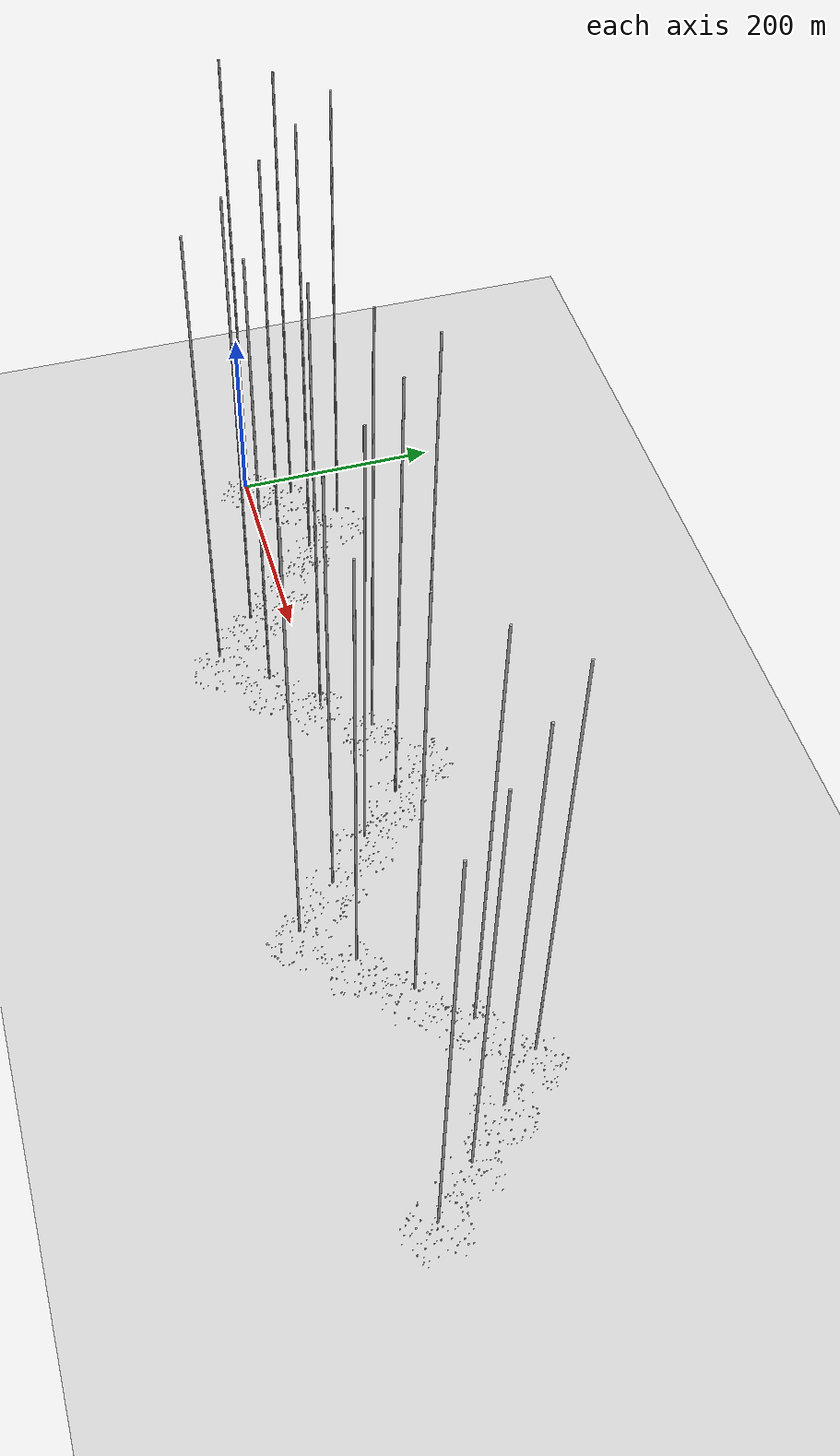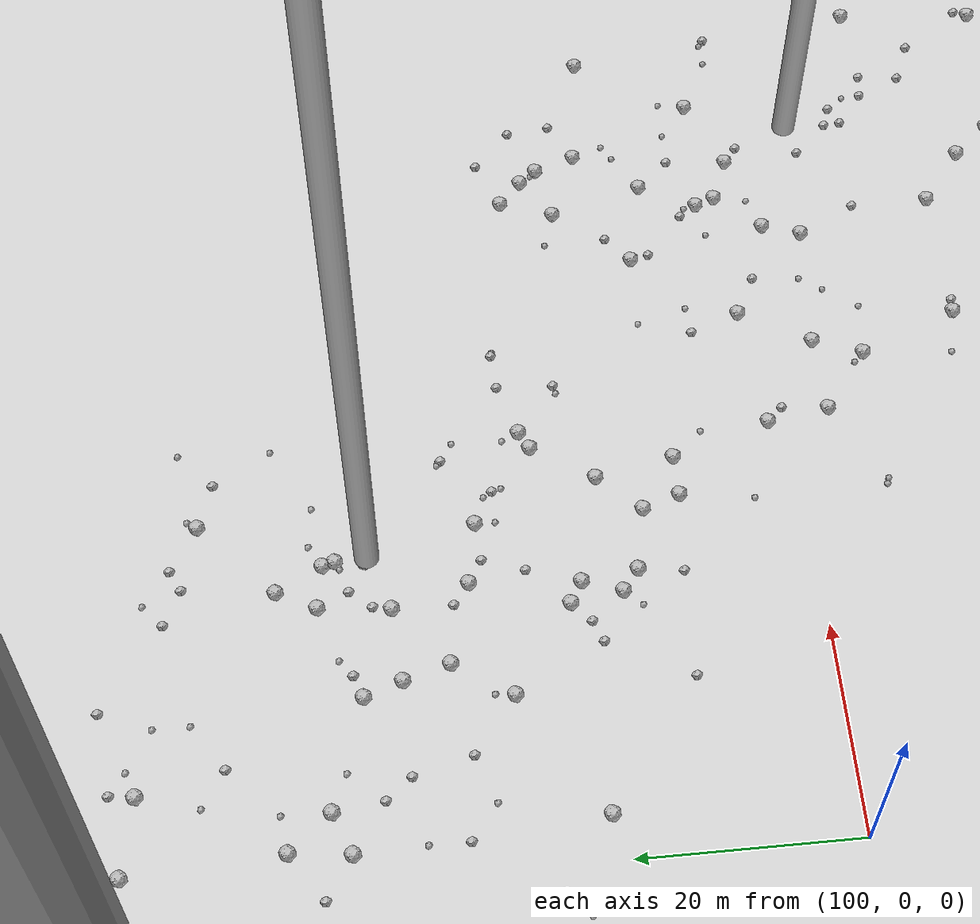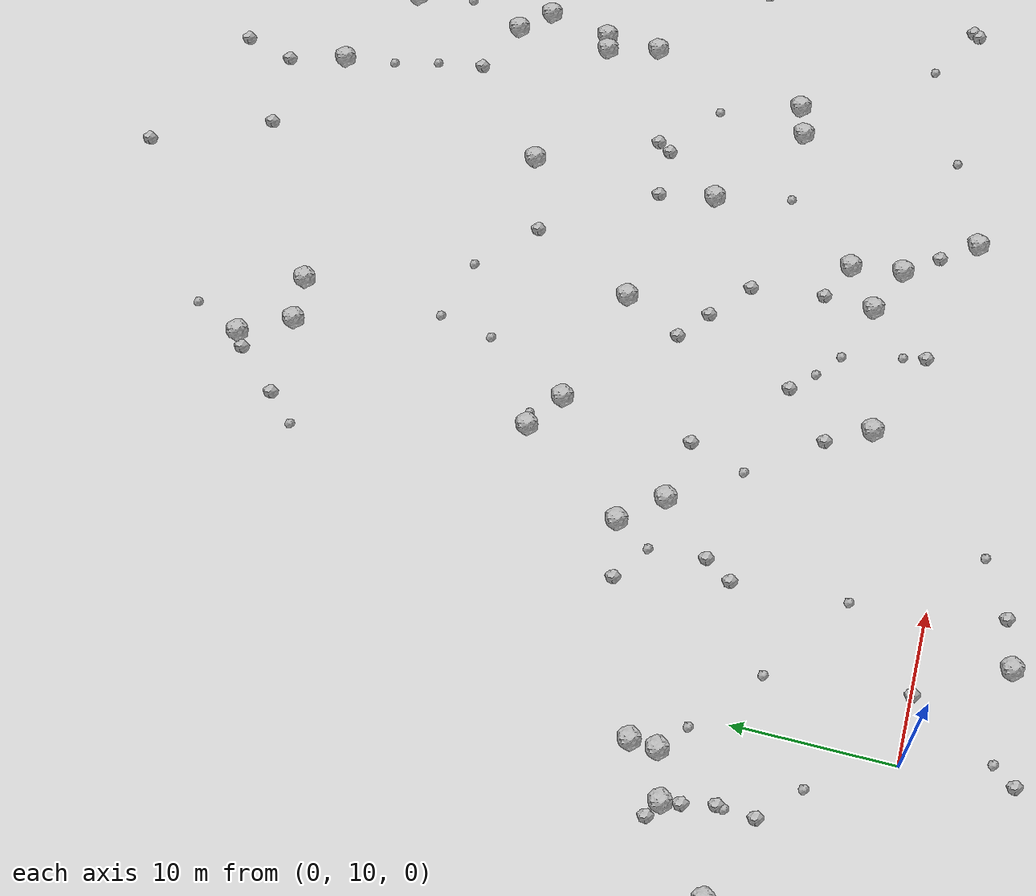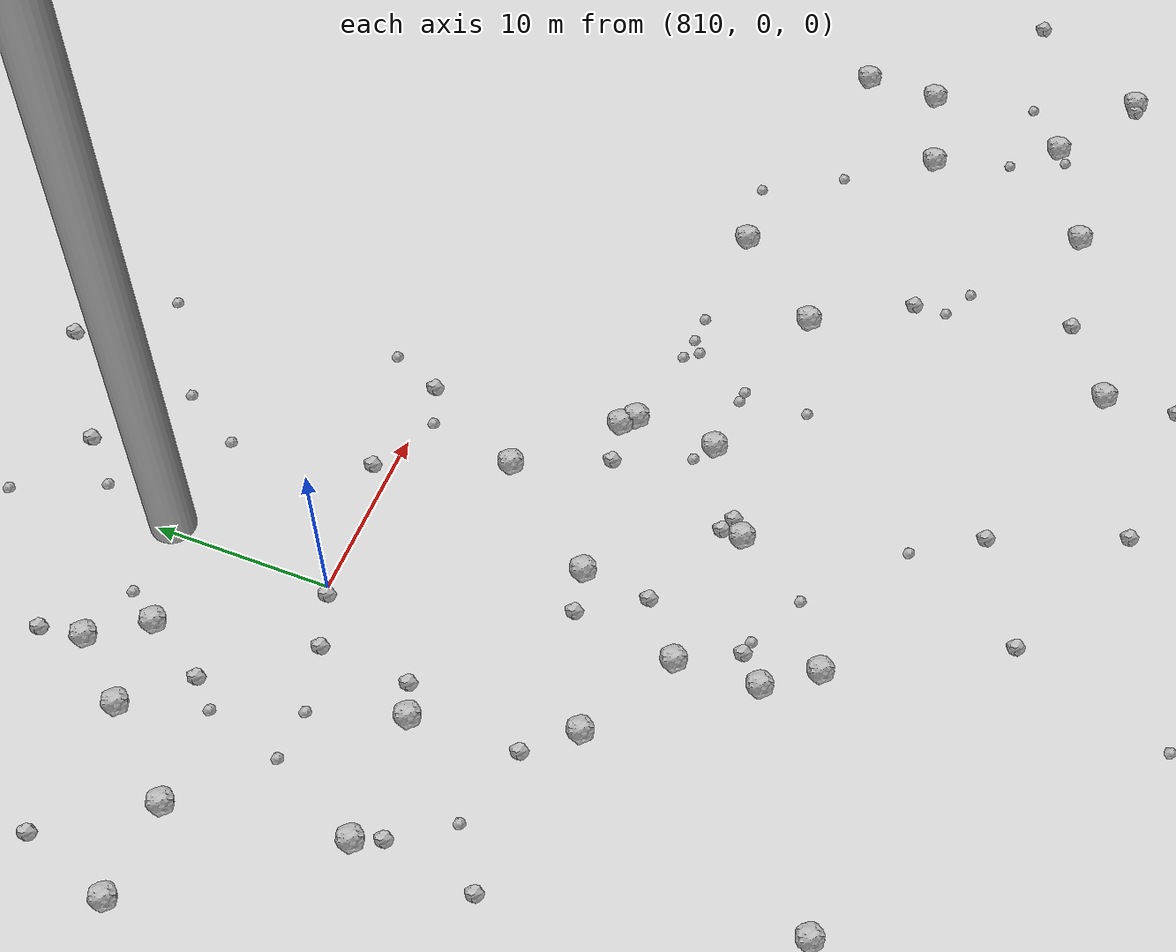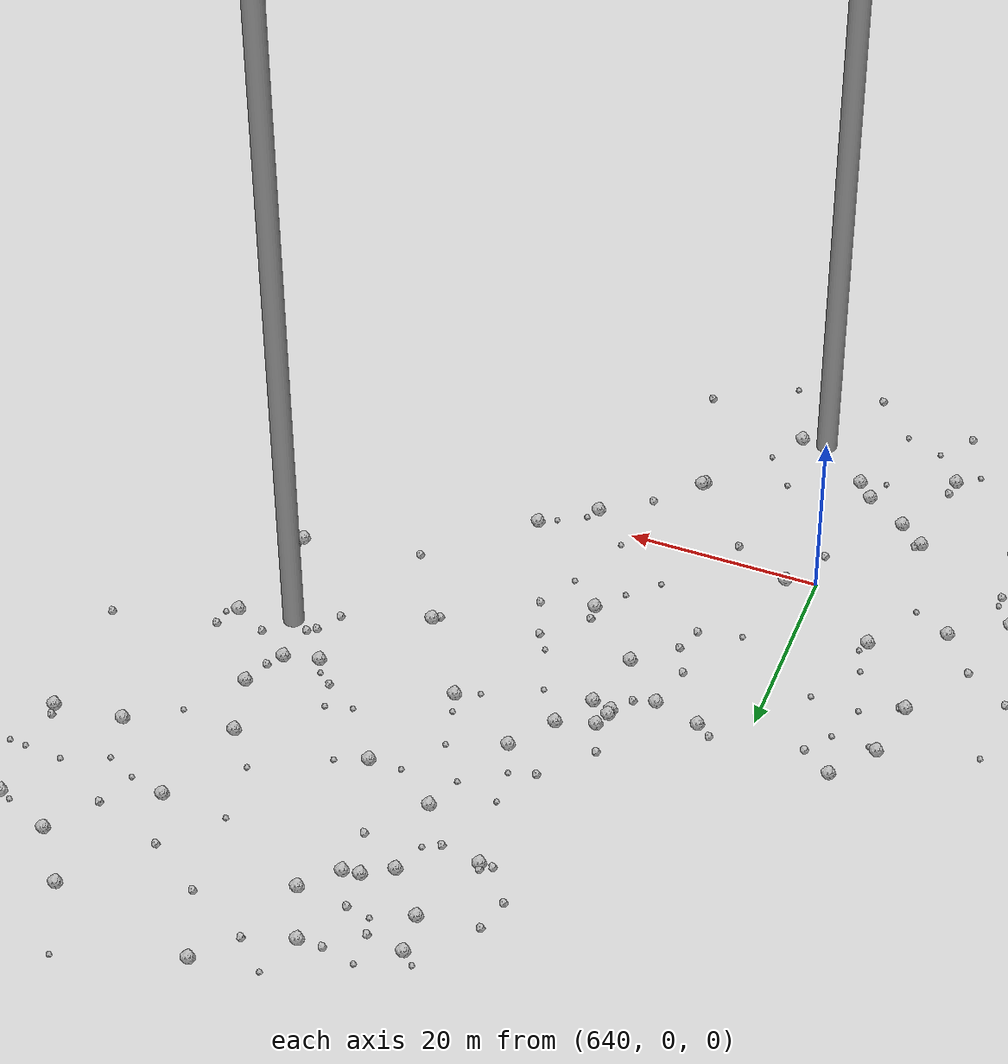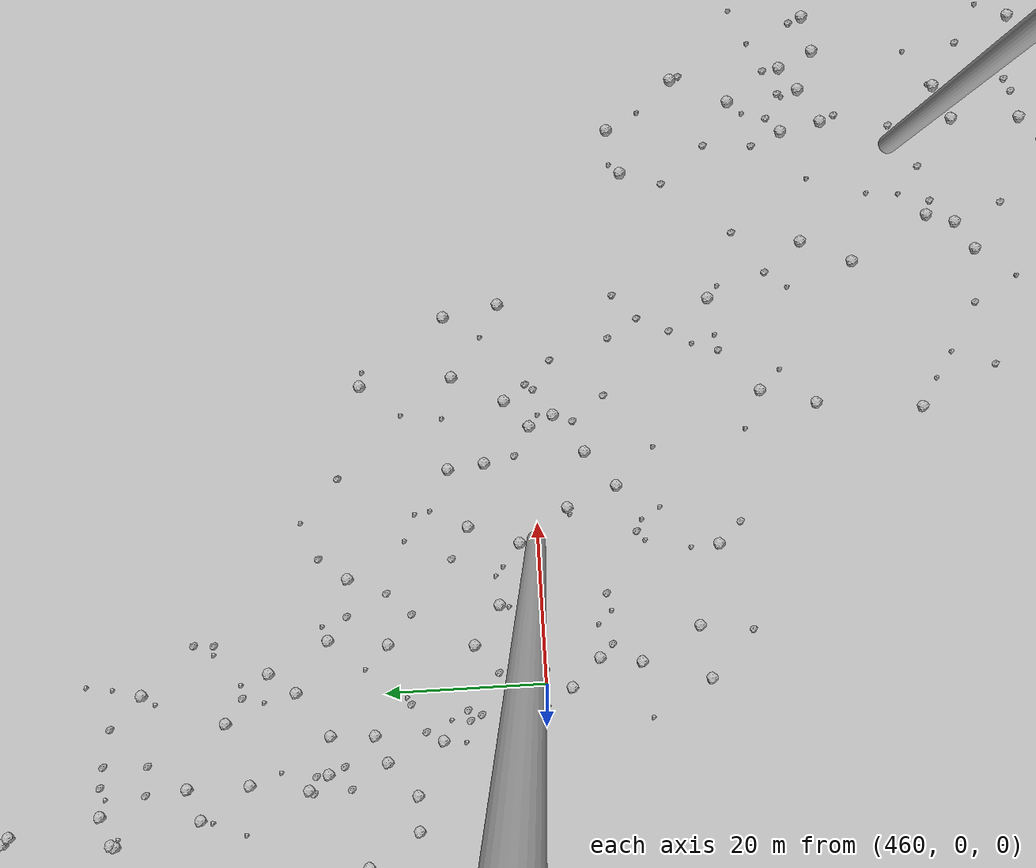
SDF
<sdf version="1.6">
 <world name="default">
  <include><uri>model://custom_ground</uri></include>
  <include><uri>model://sun</uri></include>
  <spherical_coordinates>
   <surface_model>EARTH_WGS84</surface_model>
   <latitude_deg>38.161479</latitude_deg>
   <longitude_deg>-122.454630</longitude_deg>
   <elevation>488.0</elevation>
   <heading_deg>90</heading_deg>
  </spherical_coordinates>
  <model name="rock1_0_0">
   <include><uri>model://rock1</uri><pose>-1.3858938956621074 -5.3238628336238705 0.5 0 0 0</pose></include>
  </model>
  <model name="rock1_0_1">
   <include><uri>model://rock1</uri><pose>-5.908091954505949 -7.836691175293762 0.5 0 0 0</pose></include>
  </model>
  <model name="rock1_0_2">
   <include><uri>model://rock1</uri><pose>36.0995478963206 3.127005827615129 0.5 0 0 0</pose></include>
  </model>
  <model name="rock1_0_3">
   <include><uri>model://rock1</uri><pose>5.597036644202056 -24.69886216838963 0.5 0 0 0</pose></include>
  </model>
  <model name="rock1_0_4">
   <include><uri>model://rock1</uri><pose>11.24757512019356 -2.0365448422358767 0.5 0 0 0</pose></include>
  </model>
  <model name="rock1_0_5">
   <include><uri>model://rock1</uri><pose>-9.339920895966632 6.588858190273982 0.5 0 0 0</pose></include>
  </model>
  <model name="rock1_0_6">
   <include><uri>model://rock1</uri><pose>21.298336856256405 15.401987858014323 0.5 0 0 0</pose></include>
  </model>
  <model name="rock1_0_7">
   <include><uri>model://rock1</uri><pose>-5.6780275784638174 -1.2363627953088248 0.5 0 0 0</pose></include>
  </model>
  <model name="rock1_0_8">
   <include><uri>model://rock1</uri><pose>17.15898315206359 -10.48183974764575 0.5 0 0 0</pose></include>
  </model>
  <model name="rock1_0_9">
   <include><uri>model://rock1</uri><pose>1.8889355317697536 -19.676474022234743 0.5 0 0 0</pose></include>
  </model>
  <model name="rock1_0_10">
   <include><uri>model://rock1</uri><pose>-2.3135482804699166 -12.223292945269542 0.5 0 0 0</pose></include>
  </model>
  <model name="rock1_0_11">
   <include><uri>model://rock1</uri><pose>-7.88916256918062 -16.425158222235858 0.5 0 0 0</pose></include>
  </model>
  <model name="rock1_0_12">
   <include><uri>model://rock1</uri><pose>-10.532552489612744 19.24120142432868 0.5 0 0 0</pose></include>
  </model>
  <model name="rock1_0_13">
   <include><uri>model://rock1</uri><pose>33.06026126121983 18.96862367546116 0.5 0 0 0</pose></include>
  </model>
  <model name="rock1_0_14">
   <include><uri>model://rock1</uri><pose>11.204567042529252 29.491614463943918 0.5 0 0 0</pose></include>
  </model>
  <model name="rock1_0_15">
   <include><uri>model://rock1</uri><pose>4.0849488687613835 -13.90670392717777 0.5 0 0 0</pose></include>
  </model>
  <model name="rock1_0_16">
   <include><uri>model://rock1</uri><pose>9.485528289862128 -22.55273230155673 0.5 0 0 0</pose></include>
  </model>
  <model name="rock1_0_17">
   <include><uri>model://rock1</uri><pose>-16.754497087226884 5.100887367565186 0.5 0 0 0</pose></include>
  </model>
  <model name="rock1_0_18">
   <include><uri>model://rock1</uri><pose>30.216342265077785 16.942078908361424 0.5 0 0 0</pose></include>
  </model>
  <model name="rock1_0_19">
   <include><uri>model://rock1</uri><pose>12.226218049524192 -17.358671773732226 0.5 0 0 0</pose></include>
  </model>
  <model name="rock1_0_20">
   <include><uri>model://rock1</uri><pose>13.429235327678981 26.90842543325504 0.5 0 0 0</pose></include>
  </model>
  <model name="rock1_0_21">
   <include><uri>model://rock1</uri><pose>-2.3558921164346494 25.45016693707811 0.5 0 0 0</pose></include>
  </model>
  <model name="rock1_0_22">
   <include><uri>model://rock1</uri><pose>28.38605183560842 -15.047474027126153 0.5 0 0 0</pose></include>
  </model>
  <model name="rock1_0_23">
   <include><uri>model://rock1</uri><pose>-2.5079212314752866 23.754764070981167 0.5 0 0 0</pose></include>
  </model>
  <model name="rock1_0_24">
   <include><uri>model://rock1</uri><pose>7.544929318466771 4.607330389223833 0.5 0 0 0</pose></include>
  </model>
  <model name="rock1_0_25">
   <include><uri>model://rock1</uri><pose>-5.560548960679899 22.879800342847005 0.5 0 0 0</pose></include>
  </model>
  <model name="rock1_0_26">
   <include><uri>model://rock1</uri><pose>-19.479949970078756 4.696597936214225 0.5 0 0 0</pose></include>
  </model>
  <model name="rock2_0_0">
   <include><uri>model://rock2</uri><pose>10.028339631658241 23.591088827306365 0.3 0 0 0</pose></include>
  </model>
  <model name="rock2_0_1">
   <include><uri>model://rock2</uri><pose>-11.089282862249132 -15.564834488402571 0.3 0 0 0</pose></include>
  </model>
  <model name="rock2_0_2">
   <include><uri>model://rock2</uri><pose>-5.167050962495372 17.39513143834428 0.3 0 0 0</pose></include>
  </model>
  <model name="rock2_0_3">
   <include><uri>model://rock2</uri><pose>38.6312310680208 -0.6811018175648051 0.3 0 0 0</pose></include>
  </model>
  <model name="rock2_0_4">
   <include><uri>model://rock2</uri><pose>-1.3757542251644352 -4.684190077012907 0.3 0 0 0</pose></include>
  </model>
  <model name="rock2_0_5">
   <include><uri>model://rock2</uri><pose>11.337686390909521 -17.32811027133863 0.3 0 0 0</pose></include>
  </model>
  <model name="rock2_0_6">
   <include><uri>model://rock2</uri><pose>4.017127433479001 -19.428895454493347 0.3 0 0 0</pose></include>
  </model>
  <model name="rock2_0_7">
   <include><uri>model://rock2</uri><pose>4.445701758972586 10.010069088983506 0.3 0 0 0</pose></include>
  </model>
  <model name="rock2_0_8">
   <include><uri>model://rock2</uri><pose>-14.930413338253036 12.27202208430245 0.3 0 0 0</pose></include>
  </model>
  <model name="rock2_0_9">
   <include><uri>model://rock2</uri><pose>-5.884496779654196 -14.95270759198938 0.3 0 0 0</pose></include>
  </model>
  <model name="rock2_0_10">
   <include><uri>model://rock2</uri><pose>-6.612114797544892 23.49637561214992 0.3 0 0 0</pose></include>
  </model>
  <model name="rock2_0_11">
   <include><uri>model://rock2</uri><pose>-4.971215328806462 19.717452183172178 0.3 0 0 0</pose></include>
  </model>
  <model name="rock2_0_12">
   <include><uri>model://rock2</uri><pose>-12.060684474924395 3.4526011956073503 0.3 0 0 0</pose></include>
  </model>
  <model name="rock2_0_13">
   <include><uri>model://rock2</uri><pose>14.81959330177093 -26.80086554873591 0.3 0 0 0</pose></include>
  </model>
  <model name="rock2_0_14">
   <include><uri>model://rock2</uri><pose>7.446474362160245 -9.8350487776177 0.3 0 0 0</pose></include>
  </model>
  <model name="rock2_0_15">
   <include><uri>model://rock2</uri><pose>10.663866050634375 5.325799456190538 0.3 0 0 0</pose></include>
  </model>
  <model name="rock2_0_16">
   <include><uri>model://rock2</uri><pose>14.206464832921057 -29.196759035135578 0.3 0 0 0</pose></include>
  </model>
  <model name="rock2_0_17">
   <include><uri>model://rock2</uri><pose>17.605102015783892 26.250283069565214 0.3 0 0 0</pose></include>
  </model>
  <model name="rock2_0_18">
   <include><uri>model://rock2</uri><pose>8.895533059651243 21.893018409915392 0.3 0 0 0</pose></include>
  </model>
  <model name="rock2_0_19">
   <include><uri>model://rock2</uri><pose>-5.41023906417621 21.709648705824485 0.3 0 0 0</pose></include>
  </model>
  <model name="rock2_0_20">
   <include><uri>model://rock2</uri><pose>31.831340885480174 -11.191776832833721 0.3 0 0 0</pose></include>
  </model>
  <model name="rock2_0_21">
   <include><uri>model://rock2</uri><pose>0.3626591465825797 3.3846309934458674 0.3 0 0 0</pose></include>
  </model>
  <model name="rock2_0_22">
   <include><uri>model://rock2</uri><pose>7.413702693675251 28.79967810922109 0.3 0 0 0</pose></include>
  </model>
  <model name="rock2_0_23">
   <include><uri>model://rock2</uri><pose>36.66062910800667 -1.390951485755597 0.3 0 0 0</pose></include>
  </model>
  <model name="rock2_0_24">
   <include><uri>model://rock2</uri><pose>22.967348306528493 21.044587971857474 0.3 0 0 0</pose></include>
  </model>
  <model name="rock2_0_25">
   <include><uri>model://rock2</uri><pose>33.84490243452474 -1.9972897824462308 0.3 0 0 0</pose></include>
  </model>
  <model name="rock2_0_26">
   <include><uri>model://rock2</uri><pose>0.4705660645638403 -4.892971899053677 0.3 0 0 0</pose></include>
  </model>
  <model name="rock3_0_0">
   <include><uri>model://rock3</uri><pose>9.016653266559867 -4.528922940438502 0.2 0 0 0</pose></include>
  </model>
  <model name="rock3_0_1">
   <include><uri>model://rock3</uri><pose>3.476970161241841 18.704200863104184 0.2 0 0 0</pose></include>
  </model>
  <model name="rock3_0_2">
   <include><uri>model://rock3</uri><pose>-0.7746439150366164 22.27271661187539 0.2 0 0 0</pose></include>
  </model>
  <model name="rock3_0_3">
   <include><uri>model://rock3</uri><pose>-5.095962518167065 19.243273090195935 0.2 0 0 0</pose></include>
  </model>
  <model name="rock3_0_4">
   <include><uri>model://rock3</uri><pose>27.158186050207078 -16.394180985790726 0.2 0 0 0</pose></include>
  </model>
  <model name="rock3_0_5">
   <include><uri>model://rock3</uri><pose>14.325366584242452 7.1298934306792034 0.2 0 0 0</pose></include>
  </model>
  <model name="rock3_0_6">
   <include><uri>model://rock3</uri><pose>-7.451679656819255 -19.56230301374371 0.2 0 0 0</pose></include>
  </model>
  <model name="rock3_0_7">
   <include><uri>model://rock3</uri><pose>1.4100322569830972 4.740310234881434 0.2 0 0 0</pose></include>
  </model>
  <model name="rock3_0_8">
   <include><uri>model://rock3</uri><pose>19.930811135144253 -18.346520089433746 0.2 0 0 0</pose></include>
  </model>
  <model name="rock3_0_9">
   <include><uri>model://rock3</uri><pose>-7.176867645601918 -20.681190055798606 0.2 0 0 0</pose></include>
  </model>
  <model name="rock3_0_10">
   <include><uri>model://rock3</uri><pose>-7.459194004510126 -19.56381084130259 0.2 0 0 0</pose></include>
  </model>
  <model name="rock3_0_11">
   <include><uri>model://rock3</uri><pose>29.386824971427018 -10.992668911904563 0.2 0 0 0</pose></include>
  </model>
  <model name="rock3_0_12">
   <include><uri>model://rock3</uri><pose>26.130047781651747 18.249503192810643 0.2 0 0 0</pose></include>
  </model>
  <model name="rock3_0_13">
   <include><uri>model://rock3</uri><pose>-3.8917384930721433 -15.13447263566112 0.2 0 0 0</pose></include>
  </model>
  <model name="rock3_0_14">
   <include><uri>model://rock3</uri><pose>9.922167489159996 -25.168115575505045 0.2 0 0 0</pose></include>
  </model>
  <model name="rock3_0_15">
   <include><uri>model://rock3</uri><pose>-13.456430117093696 -3.6072988012959293 0.2 0 0 0</pose></include>
  </model>
  <model name="rock3_0_16">
   <include><uri>model://rock3</uri><pose>-16.098823586354072 -5.322423830812973 0.2 0 0 0</pose></include>
  </model>
  <model name="rock3_0_17">
   <include><uri>model://rock3</uri><pose>-2.7862632353555448 15.041769742008888 0.2 0 0 0</pose></include>
  </model>
  <model name="rock3_0_18">
   <include><uri>model://rock3</uri><pose>9.787478591903593 27.154103133572946 0.2 0 0 0</pose></include>
  </model>
  <model name="rock3_0_19">
   <include><uri>model://rock3</uri><pose>1.9268765430763466 -13.043968818324 0.2 0 0 0</pose></include>
  </model>
  <model name="rock3_0_20">
   <include><uri>model://rock3</uri><pose>3.0356456972193193 -25.204181445691333 0.2 0 0 0</pose></include>
  </model>
  <model name="rock3_0_21">
   <include><uri>model://rock3</uri><pose>15.21681776145087 -1.4564373853015837 0.2 0 0 0</pose></include>
  </model>
  <model name="rock3_0_22">
   <include><uri>model://rock3</uri><pose>9.352716918454067 14.64775054155507 0.2 0 0 0</pose></include>
  </model>
  <model name="rock3_0_23">
   <include><uri>model://rock3</uri><pose>7.479016688566425 2.2683254988079398 0.2 0 0 0</pose></include>
  </model>
  <model name="rock3_0_24">
   <include><uri>model://rock3</uri><pose>-6.64563429713796 -23.777530834822944 0.2 0 0 0</pose></include>
  </model>
  <model name="rock3_0_25">
   <include><uri>model://rock3</uri><pose>37.86058846491984 -6.235116936968069 0.2 0 0 0</pose></include>
  </model>
  <model name="rock3_0_26">
   <include><uri>model://rock3</uri><pose>37.63995520542959 3.832762542650208 0.2 0 0 0</pose></include>
  </model>
  <model name="rock1_1_0">
   <include><uri>model://rock1</uri><pose>64.83644057040722 25.289337661497235 0.5 0 0 0</pose></include>
  </model>
  <model name="rock1_1_1">
   <include><uri>model://rock1</uri><pose>47.35350235613292 61.19513862076579 0.5 0 0 0</pose></include>
  </model>
  <model name="rock1_1_2">
   <include><uri>model://rock1</uri><pose>36.807286852408545 11.125465466264355 0.5 0 0 0</pose></include>
  </model>
  <model name="rock1_1_3">
   <include><uri>model://rock1</uri><pose>42.83229849587695 24.012307235462046 0.5 0 0 0</pose></include>
  </model>
  <model name="rock1_1_4">
   <include><uri>model://rock1</uri><pose>36.27828636794312 41.20728003765738 0.5 0 0 0</pose></include>
  </model>
  <model name="rock1_1_5">
   <include><uri>model://rock1</uri><pose>23.122967539213093 53.35843330799567 0.5 0 0 0</pose></include>
  </model>
  <model name="rock1_1_6">
   <include><uri>model://rock1</uri><pose>36.21501569588235 28.763360611320483 0.5 0 0 0</pose></include>
  </model>
  <model name="rock1_1_7">
   <include><uri>model://rock1</uri><pose>47.464291844742256 35.2382190527371 0.5 0 0 0</pose></include>
  </model>
  <model name="rock1_1_8">
   <include><uri>model://rock1</uri><pose>19.975452750153323 53.110745090295154 0.5 0 0 0</pose></include>
  </model>
  <model name="rock1_1_9">
   <include><uri>model://rock1</uri><pose>45.03856765234899 24.655171723453037 0.5 0 0 0</pose></include>
  </model>
  <model name="rock1_1_10">
   <include><uri>model://rock1</uri><pose>47.86121589785638 52.8378697907008 0.5 0 0 0</pose></include>
  </model>
  <model name="rock1_1_11">
   <include><uri>model://rock1</uri><pose>68.50824913432488 37.523919005566725 0.5 0 0 0</pose></include>
  </model>
  <model name="rock1_1_12">
   <include><uri>model://rock1</uri><pose>49.189375358494196 54.36438037632988 0.5 0 0 0</pose></include>
  </model>
  <model name="rock1_1_13">
   <include><uri>model://rock1</uri><pose>62.39304404547575 30.09548806092402 0.5 0 0 0</pose></include>
  </model>
  <model name="rock1_1_14">
   <include><uri>model://rock1</uri><pose>18.167553721180393 56.314833483054954 0.5 0 0 0</pose></include>
  </model>
  <model name="rock1_1_15">
   <include><uri>model://rock1</uri><pose>33.52766190216384 15.584230800423292 0.5 0 0 0</pose></include>
  </model>
  <model name="rock1_1_16">
   <include><uri>model://rock1</uri><pose>46.58995776137899 38.65345248183415 0.5 0 0 0</pose></include>
  </model>
  <model name="rock1_1_17">
   <include><uri>model://rock1</uri><pose>18.764622592233902 34.84326309510986 0.5 0 0 0</pose></include>
  </model>
  <model name="rock1_1_18">
   <include><uri>model://rock1</uri><pose>16.224492697726625 36.503298459379806 0.5 0 0 0</pose></include>
  </model>
  <model name="rock1_1_19">
   <include><uri>model://rock1</uri><pose>48.71049248036226 43.23279029608557 0.5 0 0 0</pose></include>
  </model>
  <model name="rock1_1_20">
   <include><uri>model://rock1</uri><pose>41.24506782866922 56.17837256705378 0.5 0 0 0</pose></include>
  </model>
  <model name="rock1_1_21">
   <include><uri>model://rock1</uri><pose>54.62445475859813 53.68868342625579 0.5 0 0 0</pose></include>
  </model>
  <model name="rock1_1_22">
   <include><uri>model://rock1</uri><pose>27.149932534522257 32.63016469513361 0.5 0 0 0</pose></include>
  </model>
  <model name="rock1_1_23">
   <include><uri>model://rock1</uri><pose>46.86646477186637 45.13401851472217 0.5 0 0 0</pose></include>
  </model>
  <model name="rock1_1_24">
   <include><uri>model://rock1</uri><pose>65.96451774948457 30.358526085067894 0.5 0 0 0</pose></include>
  </model>
  <model name="rock1_1_25">
   <include><uri>model://rock1</uri><pose>55.54557439312414 65.15154533290672 0.5 0 0 0</pose></include>
  </model>
  <model name="rock1_1_26">
   <include><uri>model://rock1</uri><pose>47.75354351775356 38.975296294864755 0.5 0 0 0</pose></include>
  </model>
  <model name="rock2_1_0">
   <include><uri>model://rock2</uri><pose>62.390498659181155 29.198929912159628 0.3 0 0 0</pose></include>
  </model>
  <model name="rock2_1_1">
   <include><uri>model://rock2</uri><pose>54.274104959410145 28.69214638936422 0.3 0 0 0</pose></include>
  </model>
  <model name="rock2_1_2">
   <include><uri>model://rock2</uri><pose>17.12959874913017 55.706295500237985 0.3 0 0 0</pose></include>
  </model>
  <model name="rock2_1_3">
   <include><uri>model://rock2</uri><pose>41.2146270763514 63.260782420308374 0.3 0 0 0</pose></include>
  </model>
  <model name="rock2_1_4">
   <include><uri>model://rock2</uri><pose>27.320600356020375 12.985690034627895 0.3 0 0 0</pose></include>
  </model>
  <model name="rock2_1_5">
   <include><uri>model://rock2</uri><pose>35.1181943842962 13.363197717259707 0.3 0 0 0</pose></include>
  </model>
  <model name="rock2_1_6">
   <include><uri>model://rock2</uri><pose>27.093506038613775 27.15108234373301 0.3 0 0 0</pose></include>
  </model>
  <model name="rock2_1_7">
   <include><uri>model://rock2</uri><pose>53.54276737065861 53.94491264413765 0.3 0 0 0</pose></include>
  </model>
  <model name="rock2_1_8">
   <include><uri>model://rock2</uri><pose>31.27228486610049 67.05368660198037 0.3 0 0 0</pose></include>
  </model>
  <model name="rock2_1_9">
   <include><uri>model://rock2</uri><pose>62.39940592007447 24.234988536087464 0.3 0 0 0</pose></include>
  </model>
  <model name="rock2_1_10">
   <include><uri>model://rock2</uri><pose>54.89864964108161 30.70558807140902 0.3 0 0 0</pose></include>
  </model>
  <model name="rock2_1_11">
   <include><uri>model://rock2</uri><pose>35.50397603836785 32.437214031789324 0.3 0 0 0</pose></include>
  </model>
  <model name="rock2_1_12">
   <include><uri>model://rock2</uri><pose>14.425437922893094 52.853442088782955 0.3 0 0 0</pose></include>
  </model>
  <model name="rock2_1_13">
   <include><uri>model://rock2</uri><pose>25.010929713639154 28.77995556412396 0.3 0 0 0</pose></include>
  </model>
  <model name="rock2_1_14">
   <include><uri>model://rock2</uri><pose>30.36163209459818 20.194300549436313 0.3 0 0 0</pose></include>
  </model>
  <model name="rock2_1_15">
   <include><uri>model://rock2</uri><pose>30.72819534853013 39.552065438258616 0.3 0 0 0</pose></include>
  </model>
  <model name="rock2_1_16">
   <include><uri>model://rock2</uri><pose>63.280728551720976 43.29961046578054 0.3 0 0 0</pose></include>
  </model>
  <model name="rock2_1_17">
   <include><uri>model://rock2</uri><pose>19.779818219793555 18.16283856086671 0.3 0 0 0</pose></include>
  </model>
  <model name="rock2_1_18">
   <include><uri>model://rock2</uri><pose>39.07769942787074 32.49995020026603 0.3 0 0 0</pose></include>
  </model>
  <model name="rock2_1_19">
   <include><uri>model://rock2</uri><pose>39.69143494542037 33.40501515190239 0.3 0 0 0</pose></include>
  </model>
  <model name="rock2_1_20">
   <include><uri>model://rock2</uri><pose>42.94240901269615 46.766513472253635 0.3 0 0 0</pose></include>
  </model>
  <model name="rock2_1_21">
   <include><uri>model://rock2</uri><pose>54.47151622445346 14.112665208246767 0.3 0 0 0</pose></include>
  </model>
  <model name="rock2_1_22">
   <include><uri>model://rock2</uri><pose>54.20836313457529 13.698279920184543 0.3 0 0 0</pose></include>
  </model>
  <model name="rock2_1_23">
   <include><uri>model://rock2</uri><pose>29.78206917199583 24.942668082011544 0.3 0 0 0</pose></include>
  </model>
  <model name="rock2_1_24">
   <include><uri>model://rock2</uri><pose>40.21093923238129 59.95712692767751 0.3 0 0 0</pose></include>
  </model>
  <model name="rock2_1_25">
   <include><uri>model://rock2</uri><pose>34.717013288848825 59.43337886743223 0.3 0 0 0</pose></include>
  </model>
  <model name="rock2_1_26">
   <include><uri>model://rock2</uri><pose>68.71563624602247 38.05831817180554 0.3 0 0 0</pose></include>
  </model>
  <model name="rock3_1_0">
   <include><uri>model://rock3</uri><pose>54.49502762873277 33.15642744287215 0.2 0 0 0</pose></include>
  </model>
  <model name="rock3_1_1">
   <include><uri>model://rock3</uri><pose>59.705263655881744 19.013265026205374 0.2 0 0 0</pose></include>
  </model>
  <model name="rock3_1_2">
   <include><uri>model://rock3</uri><pose>47.66509964184434 68.67892035488231 0.2 0 0 0</pose></include>
  </model>
  <model name="rock3_1_3">
   <include><uri>model://rock3</uri><pose>24.42707449499804 19.574080434535176 0.2 0 0 0</pose></include>
  </model>
  <model name="rock3_1_4">
   <include><uri>model://rock3</uri><pose>27.02630765350768 42.91820502921845 0.2 0 0 0</pose></include>
  </model>
  <model name="rock3_1_5">
   <include><uri>model://rock3</uri><pose>48.47623295415905 48.928825935950236 0.2 0 0 0</pose></include>
  </model>
  <model name="rock3_1_6">
   <include><uri>model://rock3</uri><pose>27.0403573297469 14.3995409542887 0.2 0 0 0</pose></include>
  </model>
  <model name="rock3_1_7">
   <include><uri>model://rock3</uri><pose>57.449163919704965 58.83138276613511 0.2 0 0 0</pose></include>
  </model>
  <model name="rock3_1_8">
   <include><uri>model://rock3</uri><pose>61.93291553143656 56.25881539124121 0.2 0 0 0</pose></include>
  </model>
  <model name="rock3_1_9">
   <include><uri>model://rock3</uri><pose>16.389875214254793 22.582401801157733 0.2 0 0 0</pose></include>
  </model>
  <model name="rock3_1_10">
   <include><uri>model://rock3</uri><pose>12.555688245202427 50.97300183947601 0.2 0 0 0</pose></include>
  </model>
  <model name="rock3_1_11">
   <include><uri>model://rock3</uri><pose>63.1838537572372 54.55278962242317 0.2 0 0 0</pose></include>
  </model>
  <model name="rock3_1_12">
   <include><uri>model://rock3</uri><pose>17.129501355559142 36.563112075698015 0.2 0 0 0</pose></include>
  </model>
  <model name="rock3_1_13">
   <include><uri>model://rock3</uri><pose>53.575536404047774 34.98774637085779 0.2 0 0 0</pose></include>
  </model>
  <model name="rock3_1_14">
   <include><uri>model://rock3</uri><pose>37.33229684304285 23.70820049914485 0.2 0 0 0</pose></include>
  </model>
  <model name="rock3_1_15">
   <include><uri>model://rock3</uri><pose>50.391696043938346 16.130098403998648 0.2 0 0 0</pose></include>
  </model>
  <model name="rock3_1_16">
   <include><uri>model://rock3</uri><pose>19.665041041567335 59.52437081159021 0.2 0 0 0</pose></include>
  </model>
  <model name="rock3_1_17">
   <include><uri>model://rock3</uri><pose>43.25006098108705 29.88372841382679 0.2 0 0 0</pose></include>
  </model>
  <model name="rock3_1_18">
   <include><uri>model://rock3</uri><pose>41.72229048387969 52.758918702111416 0.2 0 0 0</pose></include>
  </model>
  <model name="rock3_1_19">
   <include><uri>model://rock3</uri><pose>63.54998962012609 43.91557213449376 0.2 0 0 0</pose></include>
  </model>
  <model name="rock3_1_20">
   <include><uri>model://rock3</uri><pose>43.05451261164002 13.409920976774375 0.2 0 0 0</pose></include>
  </model>
  <model name="rock3_1_21">
   <include><uri>model://rock3</uri><pose>50.55683724500514 66.87381594268257 0.2 0 0 0</pose></include>
  </model>
  <model name="rock3_1_22">
   <include><uri>model://rock3</uri><pose>21.87856426110551 40.36958539588938 0.2 0 0 0</pose></include>
  </model>
  <model name="rock3_1_23">
   <include><uri>model://rock3</uri><pose>42.4885768542022 49.8076355076182 0.2 0 0 0</pose></include>
  </model>
  <model name="rock3_1_24">
   <include><uri>model://rock3</uri><pose>57.02206269717211 41.48023544122725 0.2 0 0 0</pose></include>
  </model>
  <model name="rock3_1_25">
   <include><uri>model://rock3</uri><pose>22.646304878689474 43.94977715253203 0.2 0 0 0</pose></include>
  </model>
  <model name="rock3_1_26">
   <include><uri>model://rock3</uri><pose>58.235596666737074 45.01521524005175 0.2 0 0 0</pose></include>
  </model>
  <model name="rock1_2_0">
   <include><uri>model://rock1</uri><pose>91.02974461814883 63.57536145860689 0.5 0 0 0</pose></include>
  </model>
  <model name="rock1_2_1">
   <include><uri>model://rock1</uri><pose>81.74457627435194 73.09326848324658 0.5 0 0 0</pose></include>
  </model>
  <model name="rock1_2_2">
   <include><uri>model://rock1</uri><pose>83.98084783918353 90.6282701974022 0.5 0 0 0</pose></include>
  </model>
  <model name="rock1_2_3">
   <include><uri>model://rock1</uri><pose>55.563422160890454 65.7737514799156 0.5 0 0 0</pose></include>
  </model>
  <model name="rock1_2_4">
   <include><uri>model://rock1</uri><pose>99.49942172060977 99.63965679704847 0.5 0 0 0</pose></include>
  </model>
  <model name="rock1_2_5">
   <include><uri>model://rock1</uri><pose>102.35157806051876 62.82564600612356 0.5 0 0 0</pose></include>
  </model>
  <model name="rock1_2_6">
   <include><uri>model://rock1</uri><pose>106.2061645110314 82.91374087413085 0.5 0 0 0</pose></include>
  </model>
  <model name="rock1_2_7">
   <include><uri>model://rock1</uri><pose>109.55603540187998 78.71888253221495 0.5 0 0 0</pose></include>
  </model>
  <model name="rock1_2_8">
   <include><uri>model://rock1</uri><pose>103.31717235190374 89.27760912235678 0.5 0 0 0</pose></include>
  </model>
  <model name="rock1_2_9">
   <include><uri>model://rock1</uri><pose>80.64677313800658 68.11717290220801 0.5 0 0 0</pose></include>
  </model>
  <model name="rock1_2_10">
   <include><uri>model://rock1</uri><pose>65.49615712983851 62.985667604216275 0.5 0 0 0</pose></include>
  </model>
  <model name="rock1_2_11">
   <include><uri>model://rock1</uri><pose>73.1658284618932 62.22713607261032 0.5 0 0 0</pose></include>
  </model>
  <model name="rock1_2_12">
   <include><uri>model://rock1</uri><pose>58.345411717121465 81.33714280715797 0.5 0 0 0</pose></include>
  </model>
  <model name="rock1_2_13">
   <include><uri>model://rock1</uri><pose>71.50102966084701 68.64286617100126 0.5 0 0 0</pose></include>
  </model>
  <model name="rock1_2_14">
   <include><uri>model://rock1</uri><pose>100.3340660235875 78.31194586517316 0.5 0 0 0</pose></include>
  </model>
  <model name="rock1_2_15">
   <include><uri>model://rock1</uri><pose>94.52062158362719 99.22441413002352 0.5 0 0 0</pose></include>
  </model>
  <model name="rock1_2_16">
   <include><uri>model://rock1</uri><pose>83.26646686670705 95.44108800244837 0.5 0 0 0</pose></include>
  </model>
  <model name="rock1_2_17">
   <include><uri>model://rock1</uri><pose>96.78494658840853 103.67449583806524 0.5 0 0 0</pose></include>
  </model>
  <model name="rock1_2_18">
   <include><uri>model://rock1</uri><pose>79.2933476783711 108.17409319042821 0.5 0 0 0</pose></include>
  </model>
  <model name="rock1_2_19">
   <include><uri>model://rock1</uri><pose>77.62221809238515 50.41923743318704 0.5 0 0 0</pose></include>
  </model>
  <model name="rock1_2_20">
   <include><uri>model://rock1</uri><pose>99.57915869644245 102.51080880340368 0.5 0 0 0</pose></include>
  </model>
  <model name="rock1_2_21">
   <include><uri>model://rock1</uri><pose>60.09835809628548 96.77717746803675 0.5 0 0 0</pose></include>
  </model>
  <model name="rock1_2_22">
   <include><uri>model://rock1</uri><pose>71.54880077288969 75.31559775989359 0.5 0 0 0</pose></include>
  </model>
  <model name="rock1_2_23">
   <include><uri>model://rock1</uri><pose>66.66309287700959 101.06111571237737 0.5 0 0 0</pose></include>
  </model>
  <model name="rock1_2_24">
   <include><uri>model://rock1</uri><pose>76.83282134627679 62.674797090397554 0.5 0 0 0</pose></include>
  </model>
  <model name="rock1_2_25">
   <include><uri>model://rock1</uri><pose>77.34635325763395 54.83455876497065 0.5 0 0 0</pose></include>
  </model>
  <model name="rock1_2_26">
   <include><uri>model://rock1</uri><pose>56.66657126813507 63.776835851561316 0.5 0 0 0</pose></include>
  </model>
  <model name="rock2_2_0">
   <include><uri>model://rock2</uri><pose>81.13995563014333 69.55011748498809 0.3 0 0 0</pose></include>
  </model>
  <model name="rock2_2_1">
   <include><uri>model://rock2</uri><pose>94.54519349796257 87.87432629894175 0.3 0 0 0</pose></include>
  </model>
  <model name="rock2_2_2">
   <include><uri>model://rock2</uri><pose>87.38939996598177 99.92300533358517 0.3 0 0 0</pose></include>
  </model>
  <model name="rock2_2_3">
   <include><uri>model://rock2</uri><pose>72.75087066344165 67.95776484538042 0.3 0 0 0</pose></include>
  </model>
  <model name="rock2_2_4">
   <include><uri>model://rock2</uri><pose>96.98664075257392 55.6078893492692 0.3 0 0 0</pose></include>
  </model>
  <model name="rock2_2_5">
   <include><uri>model://rock2</uri><pose>64.2080595235997 72.71370220522375 0.3 0 0 0</pose></include>
  </model>
  <model name="rock2_2_6">
   <include><uri>model://rock2</uri><pose>90.34966497298146 67.89039642230343 0.3 0 0 0</pose></include>
  </model>
  <model name="rock2_2_7">
   <include><uri>model://rock2</uri><pose>101.41791766030515 90.86091417348874 0.3 0 0 0</pose></include>
  </model>
  <model name="rock2_2_8">
   <include><uri>model://rock2</uri><pose>99.18871145797277 102.58210518519437 0.3 0 0 0</pose></include>
  </model>
  <model name="rock2_2_9">
   <include><uri>model://rock2</uri><pose>74.14357405934845 79.90947242820738 0.3 0 0 0</pose></include>
  </model>
  <model name="rock2_2_10">
   <include><uri>model://rock2</uri><pose>77.24887460898694 65.75269832176083 0.3 0 0 0</pose></include>
  </model>
  <model name="rock2_2_11">
   <include><uri>model://rock2</uri><pose>78.20995421370459 73.73134399791067 0.3 0 0 0</pose></include>
  </model>
  <model name="rock2_2_12">
   <include><uri>model://rock2</uri><pose>88.51692513507567 92.18402821456912 0.3 0 0 0</pose></include>
  </model>
  <model name="rock2_2_13">
   <include><uri>model://rock2</uri><pose>80.70366726046271 104.37795886564642 0.3 0 0 0</pose></include>
  </model>
  <model name="rock2_2_14">
   <include><uri>model://rock2</uri><pose>84.66143163210187 83.04481290143684 0.3 0 0 0</pose></include>
  </model>
  <model name="rock2_2_15">
   <include><uri>model://rock2</uri><pose>60.856477435973076 60.09546910321224 0.3 0 0 0</pose></include>
  </model>
  <model name="rock2_2_16">
   <include><uri>model://rock2</uri><pose>67.67219178738026 56.45831201889251 0.3 0 0 0</pose></include>
  </model>
  <model name="rock2_2_17">
   <include><uri>model://rock2</uri><pose>89.83614865450579 92.38693215396444 0.3 0 0 0</pose></include>
  </model>
  <model name="rock2_2_18">
   <include><uri>model://rock2</uri><pose>90.47275559781929 75.65662377620231 0.3 0 0 0</pose></include>
  </model>
  <model name="rock2_2_19">
   <include><uri>model://rock2</uri><pose>79.43707445308745 62.903664216317765 0.3 0 0 0</pose></include>
  </model>
  <model name="rock2_2_20">
   <include><uri>model://rock2</uri><pose>89.51319241622238 58.37326855560573 0.3 0 0 0</pose></include>
  </model>
  <model name="rock2_2_21">
   <include><uri>model://rock2</uri><pose>55.92604916220573 89.85157175963857 0.3 0 0 0</pose></include>
  </model>
  <model name="rock2_2_22">
   <include><uri>model://rock2</uri><pose>82.69118294375411 104.77049082941741 0.3 0 0 0</pose></include>
  </model>
  <model name="rock2_2_23">
   <include><uri>model://rock2</uri><pose>106.01881536959203 94.44540539453557 0.3 0 0 0</pose></include>
  </model>
  <model name="rock2_2_24">
   <include><uri>model://rock2</uri><pose>68.73930478904381 63.223904314369996 0.3 0 0 0</pose></include>
  </model>
  <model name="rock2_2_25">
   <include><uri>model://rock2</uri><pose>53.646441336952364 91.95347746461775 0.3 0 0 0</pose></include>
  </model>
  <model name="rock2_2_26">
   <include><uri>model://rock2</uri><pose>88.1885266380884 97.93945839529974 0.3 0 0 0</pose></include>
  </model>
  <model name="rock3_2_0">
   <include><uri>model://rock3</uri><pose>59.40704747143958 84.11166555756809 0.2 0 0 0</pose></include>
  </model>
  <model name="rock3_2_1">
   <include><uri>model://rock3</uri><pose>98.60583159644426 99.33747313885405 0.2 0 0 0</pose></include>
  </model>
  <model name="rock3_2_2">
   <include><uri>model://rock3</uri><pose>92.69573326057545 96.01281267039084 0.2 0 0 0</pose></include>
  </model>
  <model name="rock3_2_3">
   <include><uri>model://rock3</uri><pose>55.176685827335696 91.72417800624673 0.2 0 0 0</pose></include>
  </model>
  <model name="rock3_2_4">
   <include><uri>model://rock3</uri><pose>72.18687760388227 86.8333450287082 0.2 0 0 0</pose></include>
  </model>
  <model name="rock3_2_5">
   <include><uri>model://rock3</uri><pose>71.4576349537737 80.08728031060542 0.2 0 0 0</pose></include>
  </model>
  <model name="rock3_2_6">
   <include><uri>model://rock3</uri><pose>78.9451748979184 90.93713131509719 0.2 0 0 0</pose></include>
  </model>
  <model name="rock3_2_7">
   <include><uri>model://rock3</uri><pose>59.15167175498239 94.65345557448916 0.2 0 0 0</pose></include>
  </model>
  <model name="rock3_2_8">
   <include><uri>model://rock3</uri><pose>98.25253801190402 79.12801347690791 0.2 0 0 0</pose></include>
  </model>
  <model name="rock3_2_9">
   <include><uri>model://rock3</uri><pose>76.70704689863123 85.23711808864991 0.2 0 0 0</pose></include>
  </model>
  <model name="rock3_2_10">
   <include><uri>model://rock3</uri><pose>55.40671008301322 79.36174178839941 0.2 0 0 0</pose></include>
  </model>
  <model name="rock3_2_11">
   <include><uri>model://rock3</uri><pose>74.11759524574927 96.38554129335265 0.2 0 0 0</pose></include>
  </model>
  <model name="rock3_2_12">
   <include><uri>model://rock3</uri><pose>80.36199228256734 55.87612699616104 0.2 0 0 0</pose></include>
  </model>
  <model name="rock3_2_13">
   <include><uri>model://rock3</uri><pose>82.20351174188886 79.81838500472958 0.2 0 0 0</pose></include>
  </model>
  <model name="rock3_2_14">
   <include><uri>model://rock3</uri><pose>92.65079232121295 52.94408663077451 0.2 0 0 0</pose></include>
  </model>
  <model name="rock3_2_15">
   <include><uri>model://rock3</uri><pose>91.65778520563883 94.2275903678464 0.2 0 0 0</pose></include>
  </model>
  <model name="rock3_2_16">
   <include><uri>model://rock3</uri><pose>82.17647866040198 72.9059640145684 0.2 0 0 0</pose></include>
  </model>
  <model name="rock3_2_17">
   <include><uri>model://rock3</uri><pose>82.30688992716105 72.1387168886836 0.2 0 0 0</pose></include>
  </model>
  <model name="rock3_2_18">
   <include><uri>model://rock3</uri><pose>95.24089545632447 78.51584662365559 0.2 0 0 0</pose></include>
  </model>
  <model name="rock3_2_19">
   <include><uri>model://rock3</uri><pose>84.27674308581983 83.65321722291262 0.2 0 0 0</pose></include>
  </model>
  <model name="rock3_2_20">
   <include><uri>model://rock3</uri><pose>61.133675806865035 96.75258902753691 0.2 0 0 0</pose></include>
  </model>
  <model name="rock3_2_21">
   <include><uri>model://rock3</uri><pose>74.78794153045679 70.9827756253994 0.2 0 0 0</pose></include>
  </model>
  <model name="rock3_2_22">
   <include><uri>model://rock3</uri><pose>103.64969337791649 85.08906839009532 0.2 0 0 0</pose></include>
  </model>
  <model name="rock3_2_23">
   <include><uri>model://rock3</uri><pose>78.45995180011028 103.34765939079821 0.2 0 0 0</pose></include>
  </model>
  <model name="rock3_2_24">
   <include><uri>model://rock3</uri><pose>50.73624155888906 80.17620621975392 0.2 0 0 0</pose></include>
  </model>
  <model name="rock3_2_25">
   <include><uri>model://rock3</uri><pose>62.38894895318748 98.98593749669618 0.2 0 0 0</pose></include>
  </model>
  <model name="rock3_2_26">
   <include><uri>model://rock3</uri><pose>77.50842052054938 64.39578356961474 0.2 0 0 0</pose></include>
  </model>
  <model name="rock1_3_0">
   <include><uri>model://rock1</uri><pose>109.48580759256846 61.42511815736307 0.5 0 0 0</pose></include>
  </model>
  <model name="rock1_3_1">
   <include><uri>model://rock1</uri><pose>127.09476557948051 16.26836054481153 0.5 0 0 0</pose></include>
  </model>
  <model name="rock1_3_2">
   <include><uri>model://rock1</uri><pose>125.89237650731478 45.085540390905635 0.5 0 0 0</pose></include>
  </model>
  <model name="rock1_3_3">
   <include><uri>model://rock1</uri><pose>140.54497444227204 24.679245785936512 0.5 0 0 0</pose></include>
  </model>
  <model name="rock1_3_4">
   <include><uri>model://rock1</uri><pose>119.36915065321699 33.740180640111824 0.5 0 0 0</pose></include>
  </model>
  <model name="rock1_3_5">
   <include><uri>model://rock1</uri><pose>130.08722369855087 40.62607022160225 0.5 0 0 0</pose></include>
  </model>
  <model name="rock1_3_6">
   <include><uri>model://rock1</uri><pose>90.8833852032125 40.368059581276 0.5 0 0 0</pose></include>
  </model>
  <model name="rock1_3_7">
   <include><uri>model://rock1</uri><pose>104.15257023244318 21.33404140918062 0.5 0 0 0</pose></include>
  </model>
  <model name="rock1_3_8">
   <include><uri>model://rock1</uri><pose>115.8766667953231 28.391468445578727 0.5 0 0 0</pose></include>
  </model>
  <model name="rock1_3_9">
   <include><uri>model://rock1</uri><pose>116.87163241877488 41.541631427011254 0.5 0 0 0</pose></include>
  </model>
  <model name="rock1_3_10">
   <include><uri>model://rock1</uri><pose>127.11062413955922 31.5070307694955 0.5 0 0 0</pose></include>
  </model>
  <model name="rock1_3_11">
   <include><uri>model://rock1</uri><pose>125.19969030318515 38.51201071219953 0.5 0 0 0</pose></include>
  </model>
  <model name="rock1_3_12">
   <include><uri>model://rock1</uri><pose>127.7553546374433 48.702425359875356 0.5 0 0 0</pose></include>
  </model>
  <model name="rock1_3_13">
   <include><uri>model://rock1</uri><pose>130.040862318948 44.40722630486912 0.5 0 0 0</pose></include>
  </model>
  <model name="rock1_3_14">
   <include><uri>model://rock1</uri><pose>133.07979836009935 30.42205226212076 0.5 0 0 0</pose></include>
  </model>
  <model name="rock1_3_15">
   <include><uri>model://rock1</uri><pose>118.12289027563287 38.039076065779895 0.5 0 0 0</pose></include>
  </model>
  <model name="rock1_3_16">
   <include><uri>model://rock1</uri><pose>106.51857921281452 44.8869811046177 0.5 0 0 0</pose></include>
  </model>
  <model name="rock1_3_17">
   <include><uri>model://rock1</uri><pose>102.61764644438571 43.34082814344118 0.5 0 0 0</pose></include>
  </model>
  <model name="rock1_3_18">
   <include><uri>model://rock1</uri><pose>136.85758569588762 18.985676786650732 0.5 0 0 0</pose></include>
  </model>
  <model name="rock1_3_19">
   <include><uri>model://rock1</uri><pose>135.00375606923387 55.464373541207436 0.5 0 0 0</pose></include>
  </model>
  <model name="rock1_3_20">
   <include><uri>model://rock1</uri><pose>103.23037566654686 48.78227108153901 0.5 0 0 0</pose></include>
  </model>
  <model name="rock1_3_21">
   <include><uri>model://rock1</uri><pose>133.16131474247106 15.073359614109131 0.5 0 0 0</pose></include>
  </model>
  <model name="rock1_3_22">
   <include><uri>model://rock1</uri><pose>126.3194526383322 21.456874607706908 0.5 0 0 0</pose></include>
  </model>
  <model name="rock1_3_23">
   <include><uri>model://rock1</uri><pose>124.25429306176119 22.646620739198635 0.5 0 0 0</pose></include>
  </model>
  <model name="rock1_3_24">
   <include><uri>model://rock1</uri><pose>130.35562638355768 43.26824512258402 0.5 0 0 0</pose></include>
  </model>
  <model name="rock1_3_25">
   <include><uri>model://rock1</uri><pose>142.28834130868313 25.56401093621981 0.5 0 0 0</pose></include>
  </model>
  <model name="rock1_3_26">
   <include><uri>model://rock1</uri><pose>125.03773221067338 17.840085734149323 0.5 0 0 0</pose></include>
  </model>
  <model name="rock2_3_0">
   <include><uri>model://rock2</uri><pose>102.81986470816192 33.361065928089175 0.3 0 0 0</pose></include>
  </model>
  <model name="rock2_3_1">
   <include><uri>model://rock2</uri><pose>107.13218716591604 40.26954566518711 0.3 0 0 0</pose></include>
  </model>
  <model name="rock2_3_2">
   <include><uri>model://rock2</uri><pose>95.80528043025151 41.629093261924304 0.3 0 0 0</pose></include>
  </model>
  <model name="rock2_3_3">
   <include><uri>model://rock2</uri><pose>119.01792980386921 42.305242811197886 0.3 0 0 0</pose></include>
  </model>
  <model name="rock2_3_4">
   <include><uri>model://rock2</uri><pose>127.93787599876434 26.310372744933787 0.3 0 0 0</pose></include>
  </model>
  <model name="rock2_3_5">
   <include><uri>model://rock2</uri><pose>139.28779426684616 53.94400406231073 0.3 0 0 0</pose></include>
  </model>
  <model name="rock2_3_6">
   <include><uri>model://rock2</uri><pose>111.26139582703341 53.70718229220262 0.3 0 0 0</pose></include>
  </model>
  <model name="rock2_3_7">
   <include><uri>model://rock2</uri><pose>125.47435773797653 58.7829643547032 0.3 0 0 0</pose></include>
  </model>
  <model name="rock2_3_8">
   <include><uri>model://rock2</uri><pose>109.79030905243292 63.68644370497574 0.3 0 0 0</pose></include>
  </model>
  <model name="rock2_3_9">
   <include><uri>model://rock2</uri><pose>128.7966715531396 57.074315339598535 0.3 0 0 0</pose></include>
  </model>
  <model name="rock2_3_10">
   <include><uri>model://rock2</uri><pose>130.80705480397137 58.05934067476911 0.3 0 0 0</pose></include>
  </model>
  <model name="rock2_3_11">
   <include><uri>model://rock2</uri><pose>129.3075925417199 30.165593000791908 0.3 0 0 0</pose></include>
  </model>
  <model name="rock2_3_12">
   <include><uri>model://rock2</uri><pose>116.20646213116278 12.430922668854025 0.3 0 0 0</pose></include>
  </model>
  <model name="rock2_3_13">
   <include><uri>model://rock2</uri><pose>127.25357969901194 42.2003574899378 0.3 0 0 0</pose></include>
  </model>
  <model name="rock2_3_14">
   <include><uri>model://rock2</uri><pose>136.26633936626362 28.578815271132676 0.3 0 0 0</pose></include>
  </model>
  <model name="rock2_3_15">
   <include><uri>model://rock2</uri><pose>125.07313538157662 32.98643454806625 0.3 0 0 0</pose></include>
  </model>
  <model name="rock2_3_16">
   <include><uri>model://rock2</uri><pose>90.29181429284073 44.10438074183718 0.3 0 0 0</pose></include>
  </model>
  <model name="rock2_3_17">
   <include><uri>model://rock2</uri><pose>120.25633080444827 20.088561434158546 0.3 0 0 0</pose></include>
  </model>
  <model name="rock2_3_18">
   <include><uri>model://rock2</uri><pose>126.53647676645826 12.14005629784511 0.3 0 0 0</pose></include>
  </model>
  <model name="rock2_3_19">
   <include><uri>model://rock2</uri><pose>92.77498500657316 32.74779771455891 0.3 0 0 0</pose></include>
  </model>
  <model name="rock2_3_20">
   <include><uri>model://rock2</uri><pose>117.50561791541548 64.5538221692538 0.3 0 0 0</pose></include>
  </model>
  <model name="rock2_3_21">
   <include><uri>model://rock2</uri><pose>122.3191570672756 20.91773761079801 0.3 0 0 0</pose></include>
  </model>
  <model name="rock2_3_22">
   <include><uri>model://rock2</uri><pose>109.11269849668506 37.888165443043576 0.3 0 0 0</pose></include>
  </model>
  <model name="rock2_3_23">
   <include><uri>model://rock2</uri><pose>139.91335401193945 33.005581898668716 0.3 0 0 0</pose></include>
  </model>
  <model name="rock2_3_24">
   <include><uri>model://rock2</uri><pose>125.54419409103505 40.18739684752319 0.3 0 0 0</pose></include>
  </model>
  <model name="rock2_3_25">
   <include><uri>model://rock2</uri><pose>98.76317448098679 45.83167039430884 0.3 0 0 0</pose></include>
  </model>
  <model name="rock2_3_26">
   <include><uri>model://rock2</uri><pose>110.5843579164349 32.42785967876624 0.3 0 0 0</pose></include>
  </model>
  <model name="rock3_3_0">
   <include><uri>model://rock3</uri><pose>92.93058068051361 50.37632591823361 0.2 0 0 0</pose></include>
  </model>
  <model name="rock3_3_1">
   <include><uri>model://rock3</uri><pose>142.34511471592845 48.54681623438228 0.2 0 0 0</pose></include>
  </model>
  <model name="rock3_3_2">
   <include><uri>model://rock3</uri><pose>97.72711379940685 25.895399222560407 0.2 0 0 0</pose></include>
  </model>
  <model name="rock3_3_3">
   <include><uri>model://rock3</uri><pose>115.59254177553913 59.870582473590396 0.2 0 0 0</pose></include>
  </model>
  <model name="rock3_3_4">
   <include><uri>model://rock3</uri><pose>136.0080599015262 45.06414427730103 0.2 0 0 0</pose></include>
  </model>
  <model name="rock3_3_5">
   <include><uri>model://rock3</uri><pose>109.92009625822524 43.391688979395724 0.2 0 0 0</pose></include>
  </model>
  <model name="rock3_3_6">
   <include><uri>model://rock3</uri><pose>142.72582854138423 57.03305762270016 0.2 0 0 0</pose></include>
  </model>
  <model name="rock3_3_7">
   <include><uri>model://rock3</uri><pose>132.12198434153507 45.524954457477776 0.2 0 0 0</pose></include>
  </model>
  <model name="rock3_3_8">
   <include><uri>model://rock3</uri><pose>116.0860424332019 30.096949281678697 0.2 0 0 0</pose></include>
  </model>
  <model name="rock3_3_9">
   <include><uri>model://rock3</uri><pose>120.56568914730002 43.42661024396517 0.2 0 0 0</pose></include>
  </model>
  <model name="rock3_3_10">
   <include><uri>model://rock3</uri><pose>139.49007335910912 33.329104920448 0.2 0 0 0</pose></include>
  </model>
  <model name="rock3_3_11">
   <include><uri>model://rock3</uri><pose>141.52571717117561 27.119974098224475 0.2 0 0 0</pose></include>
  </model>
  <model name="rock3_3_12">
   <include><uri>model://rock3</uri><pose>129.59290695705673 42.87071177743854 0.2 0 0 0</pose></include>
  </model>
  <model name="rock3_3_13">
   <include><uri>model://rock3</uri><pose>115.5954839377888 56.55913572296631 0.2 0 0 0</pose></include>
  </model>
  <model name="rock3_3_14">
   <include><uri>model://rock3</uri><pose>141.68212126541889 31.798186999009733 0.2 0 0 0</pose></include>
  </model>
  <model name="rock3_3_15">
   <include><uri>model://rock3</uri><pose>133.06708169528167 28.534302501176185 0.2 0 0 0</pose></include>
  </model>
  <model name="rock3_3_16">
   <include><uri>model://rock3</uri><pose>123.51588755123925 16.182902659093195 0.2 0 0 0</pose></include>
  </model>
  <model name="rock3_3_17">
   <include><uri>model://rock3</uri><pose>107.87972141163928 55.87316213745385 0.2 0 0 0</pose></include>
  </model>
  <model name="rock3_3_18">
   <include><uri>model://rock3</uri><pose>95.45637523966747 23.946772291937044 0.2 0 0 0</pose></include>
  </model>
  <model name="rock3_3_19">
   <include><uri>model://rock3</uri><pose>102.83503473144116 36.942170005602485 0.2 0 0 0</pose></include>
  </model>
  <model name="rock3_3_20">
   <include><uri>model://rock3</uri><pose>127.5388375128845 60.53523411642288 0.2 0 0 0</pose></include>
  </model>
  <model name="rock3_3_21">
   <include><uri>model://rock3</uri><pose>135.6768829260836 56.352596830355395 0.2 0 0 0</pose></include>
  </model>
  <model name="rock3_3_22">
   <include><uri>model://rock3</uri><pose>106.04982664039014 30.81763435928987 0.2 0 0 0</pose></include>
  </model>
  <model name="rock3_3_23">
   <include><uri>model://rock3</uri><pose>106.6319717651071 49.20388784762402 0.2 0 0 0</pose></include>
  </model>
  <model name="rock3_3_24">
   <include><uri>model://rock3</uri><pose>136.53954645803873 27.683942310188876 0.2 0 0 0</pose></include>
  </model>
  <model name="rock3_3_25">
   <include><uri>model://rock3</uri><pose>111.81805483321362 62.19822077938256 0.2 0 0 0</pose></include>
  </model>
  <model name="rock3_3_26">
   <include><uri>model://rock3</uri><pose>135.73823876827825 29.3693032747922 0.2 0 0 0</pose></include>
  </model>
  <model name="rock1_4_0">
   <include><uri>model://rock1</uri><pose>166.67071274973583 5.591402619325557 0.5 0 0 0</pose></include>
  </model>
  <model name="rock1_4_1">
   <include><uri>model://rock1</uri><pose>160.77224304233974 12.753045770822318 0.5 0 0 0</pose></include>
  </model>
  <model name="rock1_4_2">
   <include><uri>model://rock1</uri><pose>178.98965172127322 5.042738334316482 0.5 0 0 0</pose></include>
  </model>
  <model name="rock1_4_3">
   <include><uri>model://rock1</uri><pose>152.52882142079022 -24.75232220804355 0.5 0 0 0</pose></include>
  </model>
  <model name="rock1_4_4">
   <include><uri>model://rock1</uri><pose>149.7865299915112 -3.2171423782234356 0.5 0 0 0</pose></include>
  </model>
  <model name="rock1_4_5">
   <include><uri>model://rock1</uri><pose>172.36424301156575 20.87865933433229 0.5 0 0 0</pose></include>
  </model>
  <model name="rock1_4_6">
   <include><uri>model://rock1</uri><pose>173.72947140277967 16.98035822069029 0.5 0 0 0</pose></include>
  </model>
  <model name="rock1_4_7">
   <include><uri>model://rock1</uri><pose>148.03496358866832 -7.807260345009809 0.5 0 0 0</pose></include>
  </model>
  <model name="rock1_4_8">
   <include><uri>model://rock1</uri><pose>134.36021441078066 11.569603122272987 0.5 0 0 0</pose></include>
  </model>
  <model name="rock1_4_9">
   <include><uri>model://rock1</uri><pose>163.53968476539393 -0.5351596986863498 0.5 0 0 0</pose></include>
  </model>
  <model name="rock1_4_10">
   <include><uri>model://rock1</uri><pose>153.566956953749 3.350634312646264 0.5 0 0 0</pose></include>
  </model>
  <model name="rock1_4_11">
   <include><uri>model://rock1</uri><pose>151.85858030346378 -17.19018347891045 0.5 0 0 0</pose></include>
  </model>
  <model name="rock1_4_12">
   <include><uri>model://rock1</uri><pose>170.81002787104225 -27.368047865819264 0.5 0 0 0</pose></include>
  </model>
  <model name="rock1_4_13">
   <include><uri>model://rock1</uri><pose>168.65405890649453 24.745738654529532 0.5 0 0 0</pose></include>
  </model>
  <model name="rock1_4_14">
   <include><uri>model://rock1</uri><pose>171.04477800690506 22.563389377782777 0.5 0 0 0</pose></include>
  </model>
  <model name="rock1_4_15">
   <include><uri>model://rock1</uri><pose>170.57431183137183 -21.2554911758541 0.5 0 0 0</pose></include>
  </model>
  <model name="rock1_4_16">
   <include><uri>model://rock1</uri><pose>173.63884730240878 -24.811090293405044 0.5 0 0 0</pose></include>
  </model>
  <model name="rock1_4_17">
   <include><uri>model://rock1</uri><pose>142.2366938543299 -3.501474203737004 0.5 0 0 0</pose></include>
  </model>
  <model name="rock1_4_18">
   <include><uri>model://rock1</uri><pose>166.86796030896093 19.76032341119116 0.5 0 0 0</pose></include>
  </model>
  <model name="rock1_4_19">
   <include><uri>model://rock1</uri><pose>167.39812252718045 3.6973157037041986 0.5 0 0 0</pose></include>
  </model>
  <model name="rock1_4_20">
   <include><uri>model://rock1</uri><pose>138.3394543420572 11.615409657490659 0.5 0 0 0</pose></include>
  </model>
  <model name="rock1_4_21">
   <include><uri>model://rock1</uri><pose>141.29069131072038 2.316036821423147 0.5 0 0 0</pose></include>
  </model>
  <model name="rock1_4_22">
   <include><uri>model://rock1</uri><pose>162.31521215921694 -4.152818228923344 0.5 0 0 0</pose></include>
  </model>
  <model name="rock1_4_23">
   <include><uri>model://rock1</uri><pose>171.6960008964806 1.9808446581442034 0.5 0 0 0</pose></include>
  </model>
  <model name="rock1_4_24">
   <include><uri>model://rock1</uri><pose>169.38177277484863 10.91863814198436 0.5 0 0 0</pose></include>
  </model>
  <model name="rock1_4_25">
   <include><uri>model://rock1</uri><pose>165.244546599172 -17.209580643074098 0.5 0 0 0</pose></include>
  </model>
  <model name="rock1_4_26">
   <include><uri>model://rock1</uri><pose>185.42168968398778 15.502831697319415 0.5 0 0 0</pose></include>
  </model>
  <model name="rock2_4_0">
   <include><uri>model://rock2</uri><pose>169.26814623023867 10.838056812834665 0.3 0 0 0</pose></include>
  </model>
  <model name="rock2_4_1">
   <include><uri>model://rock2</uri><pose>147.3848962922491 27.10411256555328 0.3 0 0 0</pose></include>
  </model>
  <model name="rock2_4_2">
   <include><uri>model://rock2</uri><pose>156.7816542993251 -23.438705940637384 0.3 0 0 0</pose></include>
  </model>
  <model name="rock2_4_3">
   <include><uri>model://rock2</uri><pose>187.51335774982113 1.9257741007275015 0.3 0 0 0</pose></include>
  </model>
  <model name="rock2_4_4">
   <include><uri>model://rock2</uri><pose>165.4823002478674 7.268915419096011 0.3 0 0 0</pose></include>
  </model>
  <model name="rock2_4_5">
   <include><uri>model://rock2</uri><pose>172.16962574496156 -5.417052406498236 0.3 0 0 0</pose></include>
  </model>
  <model name="rock2_4_6">
   <include><uri>model://rock2</uri><pose>148.7251254259683 -22.164527031576064 0.3 0 0 0</pose></include>
  </model>
  <model name="rock2_4_7">
   <include><uri>model://rock2</uri><pose>161.1624119198759 10.967150287403896 0.3 0 0 0</pose></include>
  </model>
  <model name="rock2_4_8">
   <include><uri>model://rock2</uri><pose>165.15735948414545 -9.77654706565865 0.3 0 0 0</pose></include>
  </model>
  <model name="rock2_4_9">
   <include><uri>model://rock2</uri><pose>181.1846247979113 -13.261086707954448 0.3 0 0 0</pose></include>
  </model>
  <model name="rock2_4_10">
   <include><uri>model://rock2</uri><pose>175.526403652669 -10.33945022856004 0.3 0 0 0</pose></include>
  </model>
  <model name="rock2_4_11">
   <include><uri>model://rock2</uri><pose>173.30457056760054 0.642386644445402 0.3 0 0 0</pose></include>
  </model>
  <model name="rock2_4_12">
   <include><uri>model://rock2</uri><pose>163.42958933924032 14.942282527412715 0.3 0 0 0</pose></include>
  </model>
  <model name="rock2_4_13">
   <include><uri>model://rock2</uri><pose>147.09249952695876 21.814320088406006 0.3 0 0 0</pose></include>
  </model>
  <model name="rock2_4_14">
   <include><uri>model://rock2</uri><pose>177.3805943020333 -9.456310084798957 0.3 0 0 0</pose></include>
  </model>
  <model name="rock2_4_15">
   <include><uri>model://rock2</uri><pose>157.42628330439146 1.3184206556293105 0.3 0 0 0</pose></include>
  </model>
  <model name="rock2_4_16">
   <include><uri>model://rock2</uri><pose>142.6803994349789 0.7918644522800165 0.3 0 0 0</pose></include>
  </model>
  <model name="rock2_4_17">
   <include><uri>model://rock2</uri><pose>178.82123183355333 -12.930277975009325 0.3 0 0 0</pose></include>
  </model>
  <model name="rock2_4_18">
   <include><uri>model://rock2</uri><pose>151.81854412468988 8.011229215686697 0.3 0 0 0</pose></include>
  </model>
  <model name="rock2_4_19">
   <include><uri>model://rock2</uri><pose>167.08511113788276 -27.955145056026748 0.3 0 0 0</pose></include>
  </model>
  <model name="rock2_4_20">
   <include><uri>model://rock2</uri><pose>177.7100615098537 19.07033930110444 0.3 0 0 0</pose></include>
  </model>
  <model name="rock2_4_21">
   <include><uri>model://rock2</uri><pose>172.21798792827613 7.744922192996476 0.3 0 0 0</pose></include>
  </model>
  <model name="rock2_4_22">
   <include><uri>model://rock2</uri><pose>153.17599714791317 -17.34526796753627 0.3 0 0 0</pose></include>
  </model>
  <model name="rock2_4_23">
   <include><uri>model://rock2</uri><pose>175.37618332120158 -8.720763548567685 0.3 0 0 0</pose></include>
  </model>
  <model name="rock2_4_24">
   <include><uri>model://rock2</uri><pose>177.26739777791366 23.168604979305854 0.3 0 0 0</pose></include>
  </model>
  <model name="rock2_4_25">
   <include><uri>model://rock2</uri><pose>173.4805819028421 26.733331558539447 0.3 0 0 0</pose></include>
  </model>
  <model name="rock2_4_26">
   <include><uri>model://rock2</uri><pose>150.94719130287442 27.320249999189066 0.3 0 0 0</pose></include>
  </model>
  <model name="rock3_4_0">
   <include><uri>model://rock3</uri><pose>178.6896969500682 -11.161306112009584 0.2 0 0 0</pose></include>
  </model>
  <model name="rock3_4_1">
   <include><uri>model://rock3</uri><pose>147.03553553827527 -6.952287397715381 0.2 0 0 0</pose></include>
  </model>
  <model name="rock3_4_2">
   <include><uri>model://rock3</uri><pose>157.0436694864256 -3.2060307763041855 0.2 0 0 0</pose></include>
  </model>
  <model name="rock3_4_3">
   <include><uri>model://rock3</uri><pose>154.62026135350098 8.183724739606646 0.2 0 0 0</pose></include>
  </model>
  <model name="rock3_4_4">
   <include><uri>model://rock3</uri><pose>153.328949371473 -8.420259235595722 0.2 0 0 0</pose></include>
  </model>
  <model name="rock3_4_5">
   <include><uri>model://rock3</uri><pose>179.52976773323311 7.567832893752438 0.2 0 0 0</pose></include>
  </model>
  <model name="rock3_4_6">
   <include><uri>model://rock3</uri><pose>174.76833780071183 13.96605141193794 0.2 0 0 0</pose></include>
  </model>
  <model name="rock3_4_7">
   <include><uri>model://rock3</uri><pose>133.650681336933 -7.661103461676941 0.2 0 0 0</pose></include>
  </model>
  <model name="rock3_4_8">
   <include><uri>model://rock3</uri><pose>184.52200146068003 2.2498963639936633 0.2 0 0 0</pose></include>
  </model>
  <model name="rock3_4_9">
   <include><uri>model://rock3</uri><pose>173.22778632506083 13.072888011059106 0.2 0 0 0</pose></include>
  </model>
  <model name="rock3_4_10">
   <include><uri>model://rock3</uri><pose>163.02796473578616 5.005923335593998 0.2 0 0 0</pose></include>
  </model>
  <model name="rock3_4_11">
   <include><uri>model://rock3</uri><pose>146.261001244074 21.603486332066282 0.2 0 0 0</pose></include>
  </model>
  <model name="rock3_4_12">
   <include><uri>model://rock3</uri><pose>155.5943169957328 -5.2791859166709685 0.2 0 0 0</pose></include>
  </model>
  <model name="rock3_4_13">
   <include><uri>model://rock3</uri><pose>133.36349572938397 4.666302621486402 0.2 0 0 0</pose></include>
  </model>
  <model name="rock3_4_14">
   <include><uri>model://rock3</uri><pose>166.771187619149 0.47132169322676987 0.2 0 0 0</pose></include>
  </model>
  <model name="rock3_4_15">
   <include><uri>model://rock3</uri><pose>140.85336435373034 8.645439620727544 0.2 0 0 0</pose></include>
  </model>
  <model name="rock3_4_16">
   <include><uri>model://rock3</uri><pose>134.2242641772442 -7.853418365789267 0.2 0 0 0</pose></include>
  </model>
  <model name="rock3_4_17">
   <include><uri>model://rock3</uri><pose>163.2824100278065 20.818149801497555 0.2 0 0 0</pose></include>
  </model>
  <model name="rock3_4_18">
   <include><uri>model://rock3</uri><pose>143.87246277819378 -19.78961242115546 0.2 0 0 0</pose></include>
  </model>
  <model name="rock3_4_19">
   <include><uri>model://rock3</uri><pose>153.28263065373082 12.911448090265118 0.2 0 0 0</pose></include>
  </model>
  <model name="rock3_4_20">
   <include><uri>model://rock3</uri><pose>166.3897813350079 6.709690508956868 0.2 0 0 0</pose></include>
  </model>
  <model name="rock3_4_21">
   <include><uri>model://rock3</uri><pose>175.58744912671187 7.6486586210063265 0.2 0 0 0</pose></include>
  </model>
  <model name="rock3_4_22">
   <include><uri>model://rock3</uri><pose>186.88826351971858 2.337701599540047 0.2 0 0 0</pose></include>
  </model>
  <model name="rock3_4_23">
   <include><uri>model://rock3</uri><pose>166.8082642095252 -24.00432842077445 0.2 0 0 0</pose></include>
  </model>
  <model name="rock3_4_24">
   <include><uri>model://rock3</uri><pose>147.3268209238765 -16.33841979868117 0.2 0 0 0</pose></include>
  </model>
  <model name="rock3_4_25">
   <include><uri>model://rock3</uri><pose>151.35617307719286 27.145181768955574 0.2 0 0 0</pose></include>
  </model>
  <model name="rock3_4_26">
   <include><uri>model://rock3</uri><pose>171.8062439814462 21.36404990912377 0.2 0 0 0</pose></include>
  </model>
  <model name="rock1_5_0">
   <include><uri>model://rock1</uri><pose>223.35496876290674 -48.391564735184545 0.5 0 0 0</pose></include>
  </model>
  <model name="rock1_5_1">
   <include><uri>model://rock1</uri><pose>188.33412727276522 -25.911975208940873 0.5 0 0 0</pose></include>
  </model>
  <model name="rock1_5_2">
   <include><uri>model://rock1</uri><pose>210.375107305602 -38.91400123954544 0.5 0 0 0</pose></include>
  </model>
  <model name="rock1_5_3">
   <include><uri>model://rock1</uri><pose>213.55134821382467 -42.81953923589403 0.5 0 0 0</pose></include>
  </model>
  <model name="rock1_5_4">
   <include><uri>model://rock1</uri><pose>197.9341647930952 -44.310298042132274 0.5 0 0 0</pose></include>
  </model>
  <model name="rock1_5_5">
   <include><uri>model://rock1</uri><pose>202.09117911696384 -34.86706384036813 0.5 0 0 0</pose></include>
  </model>
  <model name="rock1_5_6">
   <include><uri>model://rock1</uri><pose>181.24940232465215 -42.31164418252717 0.5 0 0 0</pose></include>
  </model>
  <model name="rock1_5_7">
   <include><uri>model://rock1</uri><pose>183.1024019294058 -51.67837070975338 0.5 0 0 0</pose></include>
  </model>
  <model name="rock1_5_8">
   <include><uri>model://rock1</uri><pose>200.82964636961185 -19.998610770259916 0.5 0 0 0</pose></include>
  </model>
  <model name="rock1_5_9">
   <include><uri>model://rock1</uri><pose>201.73350346553184 -57.9992286006396 0.5 0 0 0</pose></include>
  </model>
  <model name="rock1_5_10">
   <include><uri>model://rock1</uri><pose>221.80538005451635 -49.88159335946946 0.5 0 0 0</pose></include>
  </model>
  <model name="rock1_5_11">
   <include><uri>model://rock1</uri><pose>208.8361725122083 -43.436355238779406 0.5 0 0 0</pose></include>
  </model>
  <model name="rock1_5_12">
   <include><uri>model://rock1</uri><pose>197.6878910373604 -13.147069715452908 0.5 0 0 0</pose></include>
  </model>
  <model name="rock1_5_13">
   <include><uri>model://rock1</uri><pose>223.8612787941336 -40.68211691254283 0.5 0 0 0</pose></include>
  </model>
  <model name="rock1_5_14">
   <include><uri>model://rock1</uri><pose>190.36603156357404 -50.27369654796149 0.5 0 0 0</pose></include>
  </model>
  <model name="rock1_5_15">
   <include><uri>model://rock1</uri><pose>209.7587742837631 -55.56442012960254 0.5 0 0 0</pose></include>
  </model>
  <model name="rock1_5_16">
   <include><uri>model://rock1</uri><pose>190.9995376379409 -47.64679913670164 0.5 0 0 0</pose></include>
  </model>
  <model name="rock1_5_17">
   <include><uri>model://rock1</uri><pose>222.82895766953456 -32.941398274318765 0.5 0 0 0</pose></include>
  </model>
  <model name="rock1_5_18">
   <include><uri>model://rock1</uri><pose>190.54335658144453 -46.91999731365814 0.5 0 0 0</pose></include>
  </model>
  <model name="rock1_5_19">
   <include><uri>model://rock1</uri><pose>202.9662446845466 -66.11066840033097 0.5 0 0 0</pose></include>
  </model>
  <model name="rock1_5_20">
   <include><uri>model://rock1</uri><pose>174.53581303764972 -32.267292276908805 0.5 0 0 0</pose></include>
  </model>
  <model name="rock1_5_21">
   <include><uri>model://rock1</uri><pose>192.82621883153007 -15.9986220276718 0.5 0 0 0</pose></include>
  </model>
  <model name="rock1_5_22">
   <include><uri>model://rock1</uri><pose>218.37569573249922 -50.50338078450711 0.5 0 0 0</pose></include>
  </model>
  <model name="rock1_5_23">
   <include><uri>model://rock1</uri><pose>203.38258270343414 -21.315483319213136 0.5 0 0 0</pose></include>
  </model>
  <model name="rock1_5_24">
   <include><uri>model://rock1</uri><pose>191.0975934175303 -56.12836460651563 0.5 0 0 0</pose></include>
  </model>
  <model name="rock1_5_25">
   <include><uri>model://rock1</uri><pose>189.41157304907452 -12.820800746334008 0.5 0 0 0</pose></include>
  </model>
  <model name="rock1_5_26">
   <include><uri>model://rock1</uri><pose>202.33063487224646 -26.072405050640384 0.5 0 0 0</pose></include>
  </model>
  <model name="rock2_5_0">
   <include><uri>model://rock2</uri><pose>202.67627729486455 -63.65810142123439 0.3 0 0 0</pose></include>
  </model>
  <model name="rock2_5_1">
   <include><uri>model://rock2</uri><pose>184.59579351018053 -18.794617683176917 0.3 0 0 0</pose></include>
  </model>
  <model name="rock2_5_2">
   <include><uri>model://rock2</uri><pose>180.72425561504338 -17.169804450369355 0.3 0 0 0</pose></include>
  </model>
  <model name="rock2_5_3">
   <include><uri>model://rock2</uri><pose>204.8331401892955 -26.15678309301739 0.3 0 0 0</pose></include>
  </model>
  <model name="rock2_5_4">
   <include><uri>model://rock2</uri><pose>187.1491913240464 -27.795639741240734 0.3 0 0 0</pose></include>
  </model>
  <model name="rock2_5_5">
   <include><uri>model://rock2</uri><pose>219.00761747348147 -47.30494477670468 0.3 0 0 0</pose></include>
  </model>
  <model name="rock2_5_6">
   <include><uri>model://rock2</uri><pose>203.79850724602514 -11.624608933012809 0.3 0 0 0</pose></include>
  </model>
  <model name="rock2_5_7">
   <include><uri>model://rock2</uri><pose>188.83493910253793 -24.641908997930408 0.3 0 0 0</pose></include>
  </model>
  <model name="rock2_5_8">
   <include><uri>model://rock2</uri><pose>189.8452643155886 -32.937004284997585 0.3 0 0 0</pose></include>
  </model>
  <model name="rock2_5_9">
   <include><uri>model://rock2</uri><pose>201.39368183016143 -26.853002010422884 0.3 0 0 0</pose></include>
  </model>
  <model name="rock2_5_10">
   <include><uri>model://rock2</uri><pose>195.05083984293776 -60.62554653671215 0.3 0 0 0</pose></include>
  </model>
  <model name="rock2_5_11">
   <include><uri>model://rock2</uri><pose>179.68657888791603 -44.36751458007341 0.3 0 0 0</pose></include>
  </model>
  <model name="rock2_5_12">
   <include><uri>model://rock2</uri><pose>191.8525833169798 -61.938793448551316 0.3 0 0 0</pose></include>
  </model>
  <model name="rock2_5_13">
   <include><uri>model://rock2</uri><pose>192.2854467524659 -59.634808255078624 0.3 0 0 0</pose></include>
  </model>
  <model name="rock2_5_14">
   <include><uri>model://rock2</uri><pose>177.03353418753878 -52.71166811491819 0.3 0 0 0</pose></include>
  </model>
  <model name="rock2_5_15">
   <include><uri>model://rock2</uri><pose>206.64359262614562 -25.122526357792808 0.3 0 0 0</pose></include>
  </model>
  <model name="rock2_5_16">
   <include><uri>model://rock2</uri><pose>180.9498563169259 -50.98588448556478 0.3 0 0 0</pose></include>
  </model>
  <model name="rock2_5_17">
   <include><uri>model://rock2</uri><pose>212.0314198899428 -18.390924939267933 0.3 0 0 0</pose></include>
  </model>
  <model name="rock2_5_18">
   <include><uri>model://rock2</uri><pose>197.74573289038406 -49.9921421516334 0.3 0 0 0</pose></include>
  </model>
  <model name="rock2_5_19">
   <include><uri>model://rock2</uri><pose>215.12311236926047 -49.66090421414988 0.3 0 0 0</pose></include>
  </model>
  <model name="rock2_5_20">
   <include><uri>model://rock2</uri><pose>204.53633293016202 -65.0125840809755 0.3 0 0 0</pose></include>
  </model>
  <model name="rock2_5_21">
   <include><uri>model://rock2</uri><pose>209.97588797327302 -20.233691988366942 0.3 0 0 0</pose></include>
  </model>
  <model name="rock2_5_22">
   <include><uri>model://rock2</uri><pose>207.5168572344773 -36.794793055514916 0.3 0 0 0</pose></include>
  </model>
  <model name="rock2_5_23">
   <include><uri>model://rock2</uri><pose>197.6238863635953 -14.678087155096954 0.3 0 0 0</pose></include>
  </model>
  <model name="rock2_5_24">
   <include><uri>model://rock2</uri><pose>201.63090094441958 -48.303600662660656 0.3 0 0 0</pose></include>
  </model>
  <model name="rock2_5_25">
   <include><uri>model://rock2</uri><pose>177.36608232510838 -48.3377447743373 0.3 0 0 0</pose></include>
  </model>
  <model name="rock2_5_26">
   <include><uri>model://rock2</uri><pose>201.37927426829125 -69.5345017836429 0.3 0 0 0</pose></include>
  </model>
  <model name="rock3_5_0">
   <include><uri>model://rock3</uri><pose>224.42734757589454 -32.924655180191046 0.2 0 0 0</pose></include>
  </model>
  <model name="rock3_5_1">
   <include><uri>model://rock3</uri><pose>205.9505277969213 -17.83796094140306 0.2 0 0 0</pose></include>
  </model>
  <model name="rock3_5_2">
   <include><uri>model://rock3</uri><pose>179.57286945816702 -26.273085501173476 0.2 0 0 0</pose></include>
  </model>
  <model name="rock3_5_3">
   <include><uri>model://rock3</uri><pose>181.96678675537248 -29.9545307292384 0.2 0 0 0</pose></include>
  </model>
  <model name="rock3_5_4">
   <include><uri>model://rock3</uri><pose>187.7024621207624 -39.9770562187607 0.2 0 0 0</pose></include>
  </model>
  <model name="rock3_5_5">
   <include><uri>model://rock3</uri><pose>217.72554484612087 -20.944696895422325 0.2 0 0 0</pose></include>
  </model>
  <model name="rock3_5_6">
   <include><uri>model://rock3</uri><pose>217.74571444308066 -25.177159110885015 0.2 0 0 0</pose></include>
  </model>
  <model name="rock3_5_7">
   <include><uri>model://rock3</uri><pose>227.84208346530184 -38.86606142518897 0.2 0 0 0</pose></include>
  </model>
  <model name="rock3_5_8">
   <include><uri>model://rock3</uri><pose>197.79587692899136 -30.78843979042773 0.2 0 0 0</pose></include>
  </model>
  <model name="rock3_5_9">
   <include><uri>model://rock3</uri><pose>214.1941069237348 -21.38003563836208 0.2 0 0 0</pose></include>
  </model>
  <model name="rock3_5_10">
   <include><uri>model://rock3</uri><pose>187.43313597647543 -31.143140701578204 0.2 0 0 0</pose></include>
  </model>
  <model name="rock3_5_11">
   <include><uri>model://rock3</uri><pose>223.9420084791508 -53.41952442023772 0.2 0 0 0</pose></include>
  </model>
  <model name="rock3_5_12">
   <include><uri>model://rock3</uri><pose>196.76583181888114 -58.20111029492443 0.2 0 0 0</pose></include>
  </model>
  <model name="rock3_5_13">
   <include><uri>model://rock3</uri><pose>199.5150823095804 -11.053358037187351 0.2 0 0 0</pose></include>
  </model>
  <model name="rock3_5_14">
   <include><uri>model://rock3</uri><pose>182.21014521755208 -30.779910557399845 0.2 0 0 0</pose></include>
  </model>
  <model name="rock3_5_15">
   <include><uri>model://rock3</uri><pose>208.4750362593368 -16.05045052513963 0.2 0 0 0</pose></include>
  </model>
  <model name="rock3_5_16">
   <include><uri>model://rock3</uri><pose>180.21629133004998 -58.104077648697825 0.2 0 0 0</pose></include>
  </model>
  <model name="rock3_5_17">
   <include><uri>model://rock3</uri><pose>218.65604303820643 -42.48848300016858 0.2 0 0 0</pose></include>
  </model>
  <model name="rock3_5_18">
   <include><uri>model://rock3</uri><pose>195.0474037587786 -28.904308384620414 0.2 0 0 0</pose></include>
  </model>
  <model name="rock3_5_19">
   <include><uri>model://rock3</uri><pose>184.85673038336 -62.76488650110429 0.2 0 0 0</pose></include>
  </model>
  <model name="rock3_5_20">
   <include><uri>model://rock3</uri><pose>211.21251570838564 -36.83815736353454 0.2 0 0 0</pose></include>
  </model>
  <model name="rock3_5_21">
   <include><uri>model://rock3</uri><pose>177.48304030262216 -30.364438375290504 0.2 0 0 0</pose></include>
  </model>
  <model name="rock3_5_22">
   <include><uri>model://rock3</uri><pose>190.86411294235307 -68.39488339203024 0.2 0 0 0</pose></include>
  </model>
  <model name="rock3_5_23">
   <include><uri>model://rock3</uri><pose>184.69845927518952 -39.72182109104621 0.2 0 0 0</pose></include>
  </model>
  <model name="rock3_5_24">
   <include><uri>model://rock3</uri><pose>200.24083493407707 -59.110064789271846 0.2 0 0 0</pose></include>
  </model>
  <model name="rock3_5_25">
   <include><uri>model://rock3</uri><pose>227.95421310017463 -44.40937511608641 0.2 0 0 0</pose></include>
  </model>
  <model name="rock3_5_26">
   <include><uri>model://rock3</uri><pose>194.3377202279499 -37.98055645282042 0.2 0 0 0</pose></include>
  </model>
  <model name="rock1_6_0">
   <include><uri>model://rock1</uri><pose>243.83024908586708 -82.88035635674875 0.5 0 0 0</pose></include>
  </model>
  <model name="rock1_6_1">
   <include><uri>model://rock1</uri><pose>255.35613258245255 -84.27849131511292 0.5 0 0 0</pose></include>
  </model>
  <model name="rock1_6_2">
   <include><uri>model://rock1</uri><pose>240.17896754840388 -104.87365796015034 0.5 0 0 0</pose></include>
  </model>
  <model name="rock1_6_3">
   <include><uri>model://rock1</uri><pose>239.4634183969642 -61.86075478438197 0.5 0 0 0</pose></include>
  </model>
  <model name="rock1_6_4">
   <include><uri>model://rock1</uri><pose>264.70345952712904 -89.25471441387987 0.5 0 0 0</pose></include>
  </model>
  <model name="rock1_6_5">
   <include><uri>model://rock1</uri><pose>239.96981393874285 -64.0279561469302 0.5 0 0 0</pose></include>
  </model>
  <model name="rock1_6_6">
   <include><uri>model://rock1</uri><pose>243.49218582177141 -105.98483349774844 0.5 0 0 0</pose></include>
  </model>
  <model name="rock1_6_7">
   <include><uri>model://rock1</uri><pose>219.02901034855395 -77.18744719738646 0.5 0 0 0</pose></include>
  </model>
  <model name="rock1_6_8">
   <include><uri>model://rock1</uri><pose>215.6985182577969 -73.3851361881458 0.5 0 0 0</pose></include>
  </model>
  <model name="rock1_6_9">
   <include><uri>model://rock1</uri><pose>228.3055769262413 -64.51397121011232 0.5 0 0 0</pose></include>
  </model>
  <model name="rock1_6_10">
   <include><uri>model://rock1</uri><pose>263.3734248057252 -88.87889242582162 0.5 0 0 0</pose></include>
  </model>
  <model name="rock1_6_11">
   <include><uri>model://rock1</uri><pose>230.37261237427361 -80.58519243068312 0.5 0 0 0</pose></include>
  </model>
  <model name="rock1_6_12">
   <include><uri>model://rock1</uri><pose>229.76488482627468 -74.93702246020635 0.5 0 0 0</pose></include>
  </model>
  <model name="rock1_6_13">
   <include><uri>model://rock1</uri><pose>225.4176927565183 -89.09848447903966 0.5 0 0 0</pose></include>
  </model>
  <model name="rock1_6_14">
   <include><uri>model://rock1</uri><pose>226.01412316404347 -98.24393684257684 0.5 0 0 0</pose></include>
  </model>
  <model name="rock1_6_15">
   <include><uri>model://rock1</uri><pose>254.20557240396562 -61.76311782134482 0.5 0 0 0</pose></include>
  </model>
  <model name="rock1_6_16">
   <include><uri>model://rock1</uri><pose>262.7365748573589 -69.3323595260216 0.5 0 0 0</pose></include>
  </model>
  <model name="rock1_6_17">
   <include><uri>model://rock1</uri><pose>231.07572057114714 -91.48692074554214 0.5 0 0 0</pose></include>
  </model>
  <model name="rock1_6_18">
   <include><uri>model://rock1</uri><pose>234.52770513683083 -96.13673255932248 0.5 0 0 0</pose></include>
  </model>
  <model name="rock1_6_19">
   <include><uri>model://rock1</uri><pose>257.7681625326293 -56.65090654140162 0.5 0 0 0</pose></include>
  </model>
  <model name="rock1_6_20">
   <include><uri>model://rock1</uri><pose>245.4908306785873 -86.88132530823593 0.5 0 0 0</pose></include>
  </model>
  <model name="rock1_6_21">
   <include><uri>model://rock1</uri><pose>215.6636235004151 -69.04079315463488 0.5 0 0 0</pose></include>
  </model>
  <model name="rock1_6_22">
   <include><uri>model://rock1</uri><pose>250.75950042410602 -107.32397636421331 0.5 0 0 0</pose></include>
  </model>
  <model name="rock1_6_23">
   <include><uri>model://rock1</uri><pose>253.70399735903868 -70.27960761128162 0.5 0 0 0</pose></include>
  </model>
  <model name="rock1_6_24">
   <include><uri>model://rock1</uri><pose>231.851146173688 -74.98403777729976 0.5 0 0 0</pose></include>
  </model>
  <model name="rock1_6_25">
   <include><uri>model://rock1</uri><pose>217.62899260480788 -89.51512170615179 0.5 0 0 0</pose></include>
  </model>
  <model name="rock1_6_26">
   <include><uri>model://rock1</uri><pose>243.61831890324748 -54.89490183813934 0.5 0 0 0</pose></include>
  </model>
  <model name="rock2_6_0">
   <include><uri>model://rock2</uri><pose>241.52557097940968 -106.44143024161482 0.3 0 0 0</pose></include>
  </model>
  <model name="rock2_6_1">
   <include><uri>model://rock2</uri><pose>220.7164518906822 -89.12280008149688 0.3 0 0 0</pose></include>
  </model>
  <model name="rock2_6_2">
   <include><uri>model://rock2</uri><pose>230.52154946607394 -59.32363493455457 0.3 0 0 0</pose></include>
  </model>
  <model name="rock2_6_3">
   <include><uri>model://rock2</uri><pose>243.84172764975094 -78.81016252056844 0.3 0 0 0</pose></include>
  </model>
  <model name="rock2_6_4">
   <include><uri>model://rock2</uri><pose>238.10162698652152 -104.38460699328724 0.3 0 0 0</pose></include>
  </model>
  <model name="rock2_6_5">
   <include><uri>model://rock2</uri><pose>220.64668203683914 -59.0504995809941 0.3 0 0 0</pose></include>
  </model>
  <model name="rock2_6_6">
   <include><uri>model://rock2</uri><pose>261.8140291785553 -89.30280634179363 0.3 0 0 0</pose></include>
  </model>
  <model name="rock2_6_7">
   <include><uri>model://rock2</uri><pose>253.01916167024123 -102.85054318032229 0.3 0 0 0</pose></include>
  </model>
  <model name="rock2_6_8">
   <include><uri>model://rock2</uri><pose>234.49900302431342 -87.74079706725507 0.3 0 0 0</pose></include>
  </model>
  <model name="rock2_6_9">
   <include><uri>model://rock2</uri><pose>240.9769112270854 -75.97830226081685 0.3 0 0 0</pose></include>
  </model>
  <model name="rock2_6_10">
   <include><uri>model://rock2</uri><pose>261.98653161539215 -67.2046830438027 0.3 0 0 0</pose></include>
  </model>
  <model name="rock2_6_11">
   <include><uri>model://rock2</uri><pose>258.1208110609484 -96.80716411390387 0.3 0 0 0</pose></include>
  </model>
  <model name="rock2_6_12">
   <include><uri>model://rock2</uri><pose>222.56462327949967 -102.28912867502514 0.3 0 0 0</pose></include>
  </model>
  <model name="rock2_6_13">
   <include><uri>model://rock2</uri><pose>259.76320995443933 -93.90939010492313 0.3 0 0 0</pose></include>
  </model>
  <model name="rock2_6_14">
   <include><uri>model://rock2</uri><pose>258.82196514829826 -82.40076063151224 0.3 0 0 0</pose></include>
  </model>
  <model name="rock2_6_15">
   <include><uri>model://rock2</uri><pose>236.92819914131383 -56.100176812559525 0.3 0 0 0</pose></include>
  </model>
  <model name="rock2_6_16">
   <include><uri>model://rock2</uri><pose>216.87766162370335 -69.83978671479845 0.3 0 0 0</pose></include>
  </model>
  <model name="rock2_6_17">
   <include><uri>model://rock2</uri><pose>229.99517261257023 -82.22901368737199 0.3 0 0 0</pose></include>
  </model>
  <model name="rock2_6_18">
   <include><uri>model://rock2</uri><pose>259.8941710297513 -101.83979604316346 0.3 0 0 0</pose></include>
  </model>
  <model name="rock2_6_19">
   <include><uri>model://rock2</uri><pose>232.12906250772525 -57.529579288282285 0.3 0 0 0</pose></include>
  </model>
  <model name="rock2_6_20">
   <include><uri>model://rock2</uri><pose>224.6130453588613 -90.39590176749023 0.3 0 0 0</pose></include>
  </model>
  <model name="rock2_6_21">
   <include><uri>model://rock2</uri><pose>233.21651302161226 -83.02825908025775 0.3 0 0 0</pose></include>
  </model>
  <model name="rock2_6_22">
   <include><uri>model://rock2</uri><pose>224.67547407826657 -96.08041586431753 0.3 0 0 0</pose></include>
  </model>
  <model name="rock2_6_23">
   <include><uri>model://rock2</uri><pose>262.1669453207272 -60.02962299797568 0.3 0 0 0</pose></include>
  </model>
  <model name="rock2_6_24">
   <include><uri>model://rock2</uri><pose>245.4750293054684 -95.28166367630955 0.3 0 0 0</pose></include>
  </model>
  <model name="rock2_6_25">
   <include><uri>model://rock2</uri><pose>228.26147714650529 -67.75649593685947 0.3 0 0 0</pose></include>
  </model>
  <model name="rock2_6_26">
   <include><uri>model://rock2</uri><pose>265.32798292092076 -66.54913175625768 0.3 0 0 0</pose></include>
  </model>
  <model name="rock3_6_0">
   <include><uri>model://rock3</uri><pose>230.08470028623086 -75.26378473132719 0.2 0 0 0</pose></include>
  </model>
  <model name="rock3_6_1">
   <include><uri>model://rock3</uri><pose>239.6839040198917 -92.18759742831999 0.2 0 0 0</pose></include>
  </model>
  <model name="rock3_6_2">
   <include><uri>model://rock3</uri><pose>268.71616231621556 -82.6372110426544 0.2 0 0 0</pose></include>
  </model>
  <model name="rock3_6_3">
   <include><uri>model://rock3</uri><pose>235.55381483966372 -50.43140072440898 0.2 0 0 0</pose></include>
  </model>
  <model name="rock3_6_4">
   <include><uri>model://rock3</uri><pose>229.7440202075839 -106.98777612131882 0.2 0 0 0</pose></include>
  </model>
  <model name="rock3_6_5">
   <include><uri>model://rock3</uri><pose>215.78146439368723 -66.4038998614417 0.2 0 0 0</pose></include>
  </model>
  <model name="rock3_6_6">
   <include><uri>model://rock3</uri><pose>241.13853481905392 -106.44197081439897 0.2 0 0 0</pose></include>
  </model>
  <model name="rock3_6_7">
   <include><uri>model://rock3</uri><pose>227.80992687722832 -84.66894794429751 0.2 0 0 0</pose></include>
  </model>
  <model name="rock3_6_8">
   <include><uri>model://rock3</uri><pose>229.802053760486 -99.26944203147474 0.2 0 0 0</pose></include>
  </model>
  <model name="rock3_6_9">
   <include><uri>model://rock3</uri><pose>267.4075853072387 -74.55482234923531 0.2 0 0 0</pose></include>
  </model>
  <model name="rock3_6_10">
   <include><uri>model://rock3</uri><pose>242.92807633506683 -74.46864317242353 0.2 0 0 0</pose></include>
  </model>
  <model name="rock3_6_11">
   <include><uri>model://rock3</uri><pose>246.64203300411828 -102.81393859702744 0.2 0 0 0</pose></include>
  </model>
  <model name="rock3_6_12">
   <include><uri>model://rock3</uri><pose>217.06782233888322 -83.28953345539259 0.2 0 0 0</pose></include>
  </model>
  <model name="rock3_6_13">
   <include><uri>model://rock3</uri><pose>237.60166408620898 -105.51282230047795 0.2 0 0 0</pose></include>
  </model>
  <model name="rock3_6_14">
   <include><uri>model://rock3</uri><pose>231.3206120710911 -66.04918538130006 0.2 0 0 0</pose></include>
  </model>
  <model name="rock3_6_15">
   <include><uri>model://rock3</uri><pose>235.91746241201935 -79.6941040134663 0.2 0 0 0</pose></include>
  </model>
  <model name="rock3_6_16">
   <include><uri>model://rock3</uri><pose>220.06718855302637 -85.33913675795604 0.2 0 0 0</pose></include>
  </model>
  <model name="rock3_6_17">
   <include><uri>model://rock3</uri><pose>217.83505441254187 -97.2881384078699 0.2 0 0 0</pose></include>
  </model>
  <model name="rock3_6_18">
   <include><uri>model://rock3</uri><pose>244.56739684771912 -72.68766526450334 0.2 0 0 0</pose></include>
  </model>
  <model name="rock3_6_19">
   <include><uri>model://rock3</uri><pose>246.7145398483893 -85.7166137270469 0.2 0 0 0</pose></include>
  </model>
  <model name="rock3_6_20">
   <include><uri>model://rock3</uri><pose>221.24323837176905 -97.10946937639177 0.2 0 0 0</pose></include>
  </model>
  <model name="rock3_6_21">
   <include><uri>model://rock3</uri><pose>253.60014991579934 -74.99955341757044 0.2 0 0 0</pose></include>
  </model>
  <model name="rock3_6_22">
   <include><uri>model://rock3</uri><pose>229.61633975702088 -104.58756503736049 0.2 0 0 0</pose></include>
  </model>
  <model name="rock3_6_23">
   <include><uri>model://rock3</uri><pose>249.23791764351807 -53.96558422863489 0.2 0 0 0</pose></include>
  </model>
  <model name="rock3_6_24">
   <include><uri>model://rock3</uri><pose>249.92818187727192 -52.36812840497062 0.2 0 0 0</pose></include>
  </model>
  <model name="rock3_6_25">
   <include><uri>model://rock3</uri><pose>255.59200688421674 -89.62371999368227 0.2 0 0 0</pose></include>
  </model>
  <model name="rock3_6_26">
   <include><uri>model://rock3</uri><pose>235.52408561768556 -59.991626599186816 0.2 0 0 0</pose></include>
  </model>
  <model name="rock1_7_0">
   <include><uri>model://rock1</uri><pose>301.75325490668945 -32.2783906725522 0.5 0 0 0</pose></include>
  </model>
  <model name="rock1_7_1">
   <include><uri>model://rock1</uri><pose>288.39215518979546 -18.81069247121971 0.5 0 0 0</pose></include>
  </model>
  <model name="rock1_7_2">
   <include><uri>model://rock1</uri><pose>297.23262050817254 -63.5029974788096 0.5 0 0 0</pose></include>
  </model>
  <model name="rock1_7_3">
   <include><uri>model://rock1</uri><pose>298.5838718953703 -52.88958146002577 0.5 0 0 0</pose></include>
  </model>
  <model name="rock1_7_4">
   <include><uri>model://rock1</uri><pose>304.36570142874575 -33.22991770719266 0.5 0 0 0</pose></include>
  </model>
  <model name="rock1_7_5">
   <include><uri>model://rock1</uri><pose>298.4595462968436 -60.55892307920034 0.5 0 0 0</pose></include>
  </model>
  <model name="rock1_7_6">
   <include><uri>model://rock1</uri><pose>276.0456096140971 -64.73395137763244 0.5 0 0 0</pose></include>
  </model>
  <model name="rock1_7_7">
   <include><uri>model://rock1</uri><pose>260.67317688005966 -28.28359633780793 0.5 0 0 0</pose></include>
  </model>
  <model name="rock1_7_8">
   <include><uri>model://rock1</uri><pose>304.2588302359755 -56.13032094472447 0.5 0 0 0</pose></include>
  </model>
  <model name="rock1_7_9">
   <include><uri>model://rock1</uri><pose>270.0928269634153 -50.78489762671454 0.5 0 0 0</pose></include>
  </model>
  <model name="rock1_7_10">
   <include><uri>model://rock1</uri><pose>298.0216601386554 -49.39881786282775 0.5 0 0 0</pose></include>
  </model>
  <model name="rock1_7_11">
   <include><uri>model://rock1</uri><pose>289.0305560034042 -57.47842315869808 0.5 0 0 0</pose></include>
  </model>
  <model name="rock1_7_12">
   <include><uri>model://rock1</uri><pose>263.78674406487124 -65.11783191784387 0.5 0 0 0</pose></include>
  </model>
  <model name="rock1_7_13">
   <include><uri>model://rock1</uri><pose>266.6081128366867 -52.66467285642477 0.5 0 0 0</pose></include>
  </model>
  <model name="rock1_7_14">
   <include><uri>model://rock1</uri><pose>288.1663672227729 -26.860488951007795 0.5 0 0 0</pose></include>
  </model>
  <model name="rock1_7_15">
   <include><uri>model://rock1</uri><pose>275.7098172433699 -32.30278022444635 0.5 0 0 0</pose></include>
  </model>
  <model name="rock1_7_16">
   <include><uri>model://rock1</uri><pose>262.3140808011997 -33.06346789170425 0.5 0 0 0</pose></include>
  </model>
  <model name="rock1_7_17">
   <include><uri>model://rock1</uri><pose>287.5779576846994 -30.807023586918675 0.5 0 0 0</pose></include>
  </model>
  <model name="rock1_7_18">
   <include><uri>model://rock1</uri><pose>307.8470606109738 -45.574899553358776 0.5 0 0 0</pose></include>
  </model>
  <model name="rock1_7_19">
   <include><uri>model://rock1</uri><pose>294.1370609519733 -63.75543842366568 0.5 0 0 0</pose></include>
  </model>
  <model name="rock1_7_20">
   <include><uri>model://rock1</uri><pose>276.8645922925167 -30.362031997691993 0.5 0 0 0</pose></include>
  </model>
  <model name="rock1_7_21">
   <include><uri>model://rock1</uri><pose>290.23805482874644 -37.43376498902631 0.5 0 0 0</pose></include>
  </model>
  <model name="rock1_7_22">
   <include><uri>model://rock1</uri><pose>272.1100515574966 -62.253455265747874 0.5 0 0 0</pose></include>
  </model>
  <model name="rock1_7_23">
   <include><uri>model://rock1</uri><pose>270.43254988174886 -25.201842604736946 0.5 0 0 0</pose></include>
  </model>
  <model name="rock1_7_24">
   <include><uri>model://rock1</uri><pose>261.89099200415774 -41.64638029607227 0.5 0 0 0</pose></include>
  </model>
  <model name="rock1_7_25">
   <include><uri>model://rock1</uri><pose>298.54254876460266 -61.341516169726106 0.5 0 0 0</pose></include>
  </model>
  <model name="rock1_7_26">
   <include><uri>model://rock1</uri><pose>254.74226685353514 -34.98301684469164 0.5 0 0 0</pose></include>
  </model>
  <model name="rock2_7_0">
   <include><uri>model://rock2</uri><pose>253.3505950865813 -39.87865666937252 0.3 0 0 0</pose></include>
  </model>
  <model name="rock2_7_1">
   <include><uri>model://rock2</uri><pose>302.2568936715229 -41.90572324243955 0.3 0 0 0</pose></include>
  </model>
  <model name="rock2_7_2">
   <include><uri>model://rock2</uri><pose>275.2516302310913 -10.864694494830474 0.3 0 0 0</pose></include>
  </model>
  <model name="rock2_7_3">
   <include><uri>model://rock2</uri><pose>287.5351910576245 -37.85994000191559 0.3 0 0 0</pose></include>
  </model>
  <model name="rock2_7_4">
   <include><uri>model://rock2</uri><pose>251.24504792724665 -44.19130842300954 0.3 0 0 0</pose></include>
  </model>
  <model name="rock2_7_5">
   <include><uri>model://rock2</uri><pose>294.40160724534115 -29.12448828669057 0.3 0 0 0</pose></include>
  </model>
  <model name="rock2_7_6">
   <include><uri>model://rock2</uri><pose>281.88817132237733 -19.21959856259437 0.3 0 0 0</pose></include>
  </model>
  <model name="rock2_7_7">
   <include><uri>model://rock2</uri><pose>291.88589275689105 -17.746795152125664 0.3 0 0 0</pose></include>
  </model>
  <model name="rock2_7_8">
   <include><uri>model://rock2</uri><pose>289.568867312289 -46.53221971571045 0.3 0 0 0</pose></include>
  </model>
  <model name="rock2_7_9">
   <include><uri>model://rock2</uri><pose>275.45500431586953 -57.424185922781255 0.3 0 0 0</pose></include>
  </model>
  <model name="rock2_7_10">
   <include><uri>model://rock2</uri><pose>298.4674559727349 -22.514802928697335 0.3 0 0 0</pose></include>
  </model>
  <model name="rock2_7_11">
   <include><uri>model://rock2</uri><pose>274.8955701303308 -20.56324707397831 0.3 0 0 0</pose></include>
  </model>
  <model name="rock2_7_12">
   <include><uri>model://rock2</uri><pose>265.1903405271703 -50.20398726070343 0.3 0 0 0</pose></include>
  </model>
  <model name="rock2_7_13">
   <include><uri>model://rock2</uri><pose>252.01223739775568 -38.49809072071035 0.3 0 0 0</pose></include>
  </model>
  <model name="rock2_7_14">
   <include><uri>model://rock2</uri><pose>278.63827140048704 -60.702169497821075 0.3 0 0 0</pose></include>
  </model>
  <model name="rock2_7_15">
   <include><uri>model://rock2</uri><pose>280.05079133733125 -13.106338872562802 0.3 0 0 0</pose></include>
  </model>
  <model name="rock2_7_16">
   <include><uri>model://rock2</uri><pose>277.01083108008316 -55.53351044535535 0.3 0 0 0</pose></include>
  </model>
  <model name="rock2_7_17">
   <include><uri>model://rock2</uri><pose>268.35914684389047 -60.425700644952315 0.3 0 0 0</pose></include>
  </model>
  <model name="rock2_7_18">
   <include><uri>model://rock2</uri><pose>285.80575223819216 -51.97196000067583 0.3 0 0 0</pose></include>
  </model>
  <model name="rock2_7_19">
   <include><uri>model://rock2</uri><pose>279.1125846514862 -15.997236514505758 0.3 0 0 0</pose></include>
  </model>
  <model name="rock2_7_20">
   <include><uri>model://rock2</uri><pose>304.6355282874473 -36.331895228736784 0.3 0 0 0</pose></include>
  </model>
  <model name="rock2_7_21">
   <include><uri>model://rock2</uri><pose>297.09632425595544 -16.05892575402835 0.3 0 0 0</pose></include>
  </model>
  <model name="rock2_7_22">
   <include><uri>model://rock2</uri><pose>291.1593352894391 -46.29923378717905 0.3 0 0 0</pose></include>
  </model>
  <model name="rock2_7_23">
   <include><uri>model://rock2</uri><pose>284.6617233210271 -33.9842518389401 0.3 0 0 0</pose></include>
  </model>
  <model name="rock2_7_24">
   <include><uri>model://rock2</uri><pose>253.29325128319076 -49.080010697871984 0.3 0 0 0</pose></include>
  </model>
  <model name="rock2_7_25">
   <include><uri>model://rock2</uri><pose>263.49027172089365 -31.961398394753097 0.3 0 0 0</pose></include>
  </model>
  <model name="rock2_7_26">
   <include><uri>model://rock2</uri><pose>290.12887732218866 -58.2322151695853 0.3 0 0 0</pose></include>
  </model>
  <model name="rock3_7_0">
   <include><uri>model://rock3</uri><pose>257.43881700932303 -46.47222891743064 0.2 0 0 0</pose></include>
  </model>
  <model name="rock3_7_1">
   <include><uri>model://rock3</uri><pose>292.0476833042465 -56.63876780160648 0.2 0 0 0</pose></include>
  </model>
  <model name="rock3_7_2">
   <include><uri>model://rock3</uri><pose>279.72868379584764 -57.4853276161989 0.2 0 0 0</pose></include>
  </model>
  <model name="rock3_7_3">
   <include><uri>model://rock3</uri><pose>262.3836090055713 -57.70975231221746 0.2 0 0 0</pose></include>
  </model>
  <model name="rock3_7_4">
   <include><uri>model://rock3</uri><pose>272.14053219290736 -63.734811491450074 0.2 0 0 0</pose></include>
  </model>
  <model name="rock3_7_5">
   <include><uri>model://rock3</uri><pose>254.31203814357306 -54.54717563637088 0.2 0 0 0</pose></include>
  </model>
  <model name="rock3_7_6">
   <include><uri>model://rock3</uri><pose>297.65305440598655 -17.66396110337375 0.2 0 0 0</pose></include>
  </model>
  <model name="rock3_7_7">
   <include><uri>model://rock3</uri><pose>297.2067351880384 -56.58529356880509 0.2 0 0 0</pose></include>
  </model>
  <model name="rock3_7_8">
   <include><uri>model://rock3</uri><pose>276.5744656840342 -31.02899869119627 0.2 0 0 0</pose></include>
  </model>
  <model name="rock3_7_9">
   <include><uri>model://rock3</uri><pose>262.583772082565 -38.9971902927736 0.2 0 0 0</pose></include>
  </model>
  <model name="rock3_7_10">
   <include><uri>model://rock3</uri><pose>265.66150144046975 -30.8733781280011 0.2 0 0 0</pose></include>
  </model>
  <model name="rock3_7_11">
   <include><uri>model://rock3</uri><pose>268.4195258249274 -56.188333152394456 0.2 0 0 0</pose></include>
  </model>
  <model name="rock3_7_12">
   <include><uri>model://rock3</uri><pose>286.6310341219454 -22.534484122805964 0.2 0 0 0</pose></include>
  </model>
  <model name="rock3_7_13">
   <include><uri>model://rock3</uri><pose>299.93422284904085 -56.350211546372634 0.2 0 0 0</pose></include>
  </model>
  <model name="rock3_7_14">
   <include><uri>model://rock3</uri><pose>303.30471142599447 -42.76612833553229 0.2 0 0 0</pose></include>
  </model>
  <model name="rock3_7_15">
   <include><uri>model://rock3</uri><pose>275.4965370467821 -48.18524139012827 0.2 0 0 0</pose></include>
  </model>
  <model name="rock3_7_16">
   <include><uri>model://rock3</uri><pose>273.0263626974583 -21.736423331175608 0.2 0 0 0</pose></include>
  </model>
  <model name="rock3_7_17">
   <include><uri>model://rock3</uri><pose>262.9387280994965 -44.421704070866035 0.2 0 0 0</pose></include>
  </model>
  <model name="rock3_7_18">
   <include><uri>model://rock3</uri><pose>279.55601050544226 -50.468300001621614 0.2 0 0 0</pose></include>
  </model>
  <model name="rock3_7_19">
   <include><uri>model://rock3</uri><pose>265.8130217933769 -57.213397551913765 0.2 0 0 0</pose></include>
  </model>
  <model name="rock3_7_20">
   <include><uri>model://rock3</uri><pose>269.0592562929409 -26.732442944819702 0.2 0 0 0</pose></include>
  </model>
  <model name="rock3_7_21">
   <include><uri>model://rock3</uri><pose>264.2700625676521 -39.093224146331266 0.2 0 0 0</pose></include>
  </model>
  <model name="rock3_7_22">
   <include><uri>model://rock3</uri><pose>275.21472707876603 -33.257550879960135 0.2 0 0 0</pose></include>
  </model>
  <model name="rock3_7_23">
   <include><uri>model://rock3</uri><pose>292.09638269666937 -55.06490532553883 0.2 0 0 0</pose></include>
  </model>
  <model name="rock3_7_24">
   <include><uri>model://rock3</uri><pose>289.44760300387617 -26.564903906400865 0.2 0 0 0</pose></include>
  </model>
  <model name="rock3_7_25">
   <include><uri>model://rock3</uri><pose>292.5895619615873 -19.263765216704087 0.2 0 0 0</pose></include>
  </model>
  <model name="rock3_7_26">
   <include><uri>model://rock3</uri><pose>254.8366917514938 -35.303014626458555 0.2 0 0 0</pose></include>
  </model>
  <model name="rock1_8_0">
   <include><uri>model://rock1</uri><pose>329.0179860521466 9.081825027764673 0.5 0 0 0</pose></include>
  </model>
  <model name="rock1_8_1">
   <include><uri>model://rock1</uri><pose>310.26942464568043 -22.281180565440735 0.5 0 0 0</pose></include>
  </model>
  <model name="rock1_8_2">
   <include><uri>model://rock1</uri><pose>323.593093427731 -11.395748511507001 0.5 0 0 0</pose></include>
  </model>
  <model name="rock1_8_3">
   <include><uri>model://rock1</uri><pose>313.22661068791183 3.6545234374359765 0.5 0 0 0</pose></include>
  </model>
  <model name="rock1_8_4">
   <include><uri>model://rock1</uri><pose>304.5588386357246 8.40568351266375 0.5 0 0 0</pose></include>
  </model>
  <model name="rock1_8_5">
   <include><uri>model://rock1</uri><pose>297.0820696698455 15.476133608333377 0.5 0 0 0</pose></include>
  </model>
  <model name="rock1_8_6">
   <include><uri>model://rock1</uri><pose>321.9212765108374 8.259782908408063 0.5 0 0 0</pose></include>
  </model>
  <model name="rock1_8_7">
   <include><uri>model://rock1</uri><pose>295.8929291134461 0.8304165985594665 0.5 0 0 0</pose></include>
  </model>
  <model name="rock1_8_8">
   <include><uri>model://rock1</uri><pose>336.76291363782957 -2.748733051453783 0.5 0 0 0</pose></include>
  </model>
  <model name="rock1_8_9">
   <include><uri>model://rock1</uri><pose>335.9484199879313 -21.795783922181972 0.5 0 0 0</pose></include>
  </model>
  <model name="rock1_8_10">
   <include><uri>model://rock1</uri><pose>296.28584401888054 -5.065958980028004 0.5 0 0 0</pose></include>
  </model>
  <model name="rock1_8_11">
   <include><uri>model://rock1</uri><pose>343.69073728354545 18.01305381365154 0.5 0 0 0</pose></include>
  </model>
  <model name="rock1_8_12">
   <include><uri>model://rock1</uri><pose>317.5831474213787 17.773757934132867 0.5 0 0 0</pose></include>
  </model>
  <model name="rock1_8_13">
   <include><uri>model://rock1</uri><pose>298.92225104951126 -8.468189833774012 0.5 0 0 0</pose></include>
  </model>
  <model name="rock1_8_14">
   <include><uri>model://rock1</uri><pose>323.8482745030283 -22.653695413369153 0.5 0 0 0</pose></include>
  </model>
  <model name="rock1_8_15">
   <include><uri>model://rock1</uri><pose>299.9374566574946 18.68342768870724 0.5 0 0 0</pose></include>
  </model>
  <model name="rock1_8_16">
   <include><uri>model://rock1</uri><pose>303.5198022524389 -0.32963256027026944 0.5 0 0 0</pose></include>
  </model>
  <model name="rock1_8_17">
   <include><uri>model://rock1</uri><pose>305.7630181150282 24.186579802117848 0.5 0 0 0</pose></include>
  </model>
  <model name="rock1_8_18">
   <include><uri>model://rock1</uri><pose>310.6099398979996 2.5745691390875223 0.5 0 0 0</pose></include>
  </model>
  <model name="rock1_8_19">
   <include><uri>model://rock1</uri><pose>322.0151714176364 -5.848206062630307 0.5 0 0 0</pose></include>
  </model>
  <model name="rock1_8_20">
   <include><uri>model://rock1</uri><pose>327.875878976431 -7.465227829946599 0.5 0 0 0</pose></include>
  </model>
  <model name="rock1_8_21">
   <include><uri>model://rock1</uri><pose>298.18874516613135 -0.13540042738431524 0.5 0 0 0</pose></include>
  </model>
  <model name="rock1_8_22">
   <include><uri>model://rock1</uri><pose>313.34283045193786 -6.866344613763943 0.5 0 0 0</pose></include>
  </model>
  <model name="rock1_8_23">
   <include><uri>model://rock1</uri><pose>293.3414178421761 -0.8386958715545667 0.5 0 0 0</pose></include>
  </model>
  <model name="rock1_8_24">
   <include><uri>model://rock1</uri><pose>316.2868402472241 -11.628837471619185 0.5 0 0 0</pose></include>
  </model>
  <model name="rock1_8_25">
   <include><uri>model://rock1</uri><pose>330.1418682567176 11.215315031001921 0.5 0 0 0</pose></include>
  </model>
  <model name="rock1_8_26">
   <include><uri>model://rock1</uri><pose>308.5925041361701 2.8530443414563464 0.5 0 0 0</pose></include>
  </model>
  <model name="rock2_8_0">
   <include><uri>model://rock2</uri><pose>305.1288604240127 -6.461448777213697 0.3 0 0 0</pose></include>
  </model>
  <model name="rock2_8_1">
   <include><uri>model://rock2</uri><pose>341.6056959352138 19.678226905230495 0.3 0 0 0</pose></include>
  </model>
  <model name="rock2_8_2">
   <include><uri>model://rock2</uri><pose>317.5518098361568 20.495876224031015 0.3 0 0 0</pose></include>
  </model>
  <model name="rock2_8_3">
   <include><uri>model://rock2</uri><pose>339.5831068580284 9.185475375220662 0.3 0 0 0</pose></include>
  </model>
  <model name="rock2_8_4">
   <include><uri>model://rock2</uri><pose>302.30877676822047 9.195772660308386 0.3 0 0 0</pose></include>
  </model>
  <model name="rock2_8_5">
   <include><uri>model://rock2</uri><pose>300.56463922621793 11.200642154157805 0.3 0 0 0</pose></include>
  </model>
  <model name="rock2_8_6">
   <include><uri>model://rock2</uri><pose>318.3067142688024 27.021706731018554 0.3 0 0 0</pose></include>
  </model>
  <model name="rock2_8_7">
   <include><uri>model://rock2</uri><pose>320.3045931497776 -23.852296544332766 0.3 0 0 0</pose></include>
  </model>
  <model name="rock2_8_8">
   <include><uri>model://rock2</uri><pose>296.57248884911024 8.162443395802661 0.3 0 0 0</pose></include>
  </model>
  <model name="rock2_8_9">
   <include><uri>model://rock2</uri><pose>324.9886475591819 -0.40343197082003 0.3 0 0 0</pose></include>
  </model>
  <model name="rock2_8_10">
   <include><uri>model://rock2</uri><pose>313.4739091720267 -27.756305396153127 0.3 0 0 0</pose></include>
  </model>
  <model name="rock2_8_11">
   <include><uri>model://rock2</uri><pose>297.09071870581266 14.900686185245227 0.3 0 0 0</pose></include>
  </model>
  <model name="rock2_8_12">
   <include><uri>model://rock2</uri><pose>297.9416948996302 11.15432951665359 0.3 0 0 0</pose></include>
  </model>
  <model name="rock2_8_13">
   <include><uri>model://rock2</uri><pose>310.39704551100533 -3.757484913081967 0.3 0 0 0</pose></include>
  </model>
  <model name="rock2_8_14">
   <include><uri>model://rock2</uri><pose>340.9918196274748 -17.543414786394145 0.3 0 0 0</pose></include>
  </model>
  <model name="rock2_8_15">
   <include><uri>model://rock2</uri><pose>339.9803505098221 -18.623406768730938 0.3 0 0 0</pose></include>
  </model>
  <model name="rock2_8_16">
   <include><uri>model://rock2</uri><pose>312.4526921121265 1.58358205835669 0.3 0 0 0</pose></include>
  </model>
  <model name="rock2_8_17">
   <include><uri>model://rock2</uri><pose>338.3156625084905 23.443296600444313 0.3 0 0 0</pose></include>
  </model>
  <model name="rock2_8_18">
   <include><uri>model://rock2</uri><pose>314.32021690484845 2.9599600140904343 0.3 0 0 0</pose></include>
  </model>
  <model name="rock2_8_19">
   <include><uri>model://rock2</uri><pose>305.73137811392525 20.205361708586118 0.3 0 0 0</pose></include>
  </model>
  <model name="rock2_8_20">
   <include><uri>model://rock2</uri><pose>311.90508102356625 -3.1105022167158047 0.3 0 0 0</pose></include>
  </model>
  <model name="rock2_8_21">
   <include><uri>model://rock2</uri><pose>307.7245966189621 -11.70969555109 0.3 0 0 0</pose></include>
  </model>
  <model name="rock2_8_22">
   <include><uri>model://rock2</uri><pose>292.6485883589298 -4.677359733158173 0.3 0 0 0</pose></include>
  </model>
  <model name="rock2_8_23">
   <include><uri>model://rock2</uri><pose>325.40448101768135 16.635771095230538 0.3 0 0 0</pose></include>
  </model>
  <model name="rock2_8_24">
   <include><uri>model://rock2</uri><pose>307.19157851106996 -14.061686918301836 0.3 0 0 0</pose></include>
  </model>
  <model name="rock2_8_25">
   <include><uri>model://rock2</uri><pose>336.76474814123526 -2.9638704665585145 0.3 0 0 0</pose></include>
  </model>
  <model name="rock2_8_26">
   <include><uri>model://rock2</uri><pose>311.5667188005373 -0.8339676621991359 0.3 0 0 0</pose></include>
  </model>
  <model name="rock3_8_0">
   <include><uri>model://rock3</uri><pose>327.7169841209842 -22.314547396898256 0.2 0 0 0</pose></include>
  </model>
  <model name="rock3_8_1">
   <include><uri>model://rock3</uri><pose>299.28521592578153 0.2896857347090034 0.2 0 0 0</pose></include>
  </model>
  <model name="rock3_8_2">
   <include><uri>model://rock3</uri><pose>298.3934495924427 -11.662234536782265 0.2 0 0 0</pose></include>
  </model>
  <model name="rock3_8_3">
   <include><uri>model://rock3</uri><pose>296.21432604849684 9.269319050534975 0.2 0 0 0</pose></include>
  </model>
  <model name="rock3_8_4">
   <include><uri>model://rock3</uri><pose>306.06972998422856 -11.955482991851895 0.2 0 0 0</pose></include>
  </model>
  <model name="rock3_8_5">
   <include><uri>model://rock3</uri><pose>328.6071723406202 4.154109322332765 0.2 0 0 0</pose></include>
  </model>
  <model name="rock3_8_6">
   <include><uri>model://rock3</uri><pose>323.34640185859814 -24.096632292682642 0.2 0 0 0</pose></include>
  </model>
  <model name="rock3_8_7">
   <include><uri>model://rock3</uri><pose>311.98181429313064 11.898951994707815 0.2 0 0 0</pose></include>
  </model>
  <model name="rock3_8_8">
   <include><uri>model://rock3</uri><pose>319.90001068627726 -26.859084904805105 0.2 0 0 0</pose></include>
  </model>
  <model name="rock3_8_9">
   <include><uri>model://rock3</uri><pose>307.82755982615214 -14.684231700067887 0.2 0 0 0</pose></include>
  </model>
  <model name="rock3_8_10">
   <include><uri>model://rock3</uri><pose>328.59680270862384 -17.50790827744393 0.2 0 0 0</pose></include>
  </model>
  <model name="rock3_8_11">
   <include><uri>model://rock3</uri><pose>327.1695284765395 13.044149309441053 0.2 0 0 0</pose></include>
  </model>
  <model name="rock3_8_12">
   <include><uri>model://rock3</uri><pose>330.04621621240017 -1.1621835200362725 0.2 0 0 0</pose></include>
  </model>
  <model name="rock3_8_13">
   <include><uri>model://rock3</uri><pose>321.92549136629134 7.908687288705295 0.2 0 0 0</pose></include>
  </model>
  <model name="rock3_8_14">
   <include><uri>model://rock3</uri><pose>306.73117025280897 -2.2523704019811106 0.2 0 0 0</pose></include>
  </model>
  <model name="rock3_8_15">
   <include><uri>model://rock3</uri><pose>319.77421715751063 -10.71241439179834 0.2 0 0 0</pose></include>
  </model>
  <model name="rock3_8_16">
   <include><uri>model://rock3</uri><pose>294.87264614803524 8.511031250063326 0.2 0 0 0</pose></include>
  </model>
  <model name="rock3_8_17">
   <include><uri>model://rock3</uri><pose>315.9486437025272 1.8582456975928388 0.2 0 0 0</pose></include>
  </model>
  <model name="rock3_8_18">
   <include><uri>model://rock3</uri><pose>307.8123593299651 12.59787674441759 0.2 0 0 0</pose></include>
  </model>
  <model name="rock3_8_19">
   <include><uri>model://rock3</uri><pose>329.726361861905 3.935907440902888 0.2 0 0 0</pose></include>
  </model>
  <model name="rock3_8_20">
   <include><uri>model://rock3</uri><pose>308.2098308123051 18.16875445018116 0.2 0 0 0</pose></include>
  </model>
  <model name="rock3_8_21">
   <include><uri>model://rock3</uri><pose>345.75907583071 10.359112089961407 0.2 0 0 0</pose></include>
  </model>
  <model name="rock3_8_22">
   <include><uri>model://rock3</uri><pose>346.4791192798933 7.320902868644168 0.2 0 0 0</pose></include>
  </model>
  <model name="rock3_8_23">
   <include><uri>model://rock3</uri><pose>347.2244408340289 9.710039048755071 0.2 0 0 0</pose></include>
  </model>
  <model name="rock3_8_24">
   <include><uri>model://rock3</uri><pose>299.7939405337401 20.16160176716005 0.2 0 0 0</pose></include>
  </model>
  <model name="rock3_8_25">
   <include><uri>model://rock3</uri><pose>335.229797910233 8.250858165956878 0.2 0 0 0</pose></include>
  </model>
  <model name="rock3_8_26">
   <include><uri>model://rock3</uri><pose>323.14044744681803 -25.887872459522846 0.2 0 0 0</pose></include>
  </model>
  <model name="rock1_9_0">
   <include><uri>model://rock1</uri><pose>335.18320129048107 48.625386246237156 0.5 0 0 0</pose></include>
  </model>
  <model name="rock1_9_1">
   <include><uri>model://rock1</uri><pose>353.88552862193893 58.17371028876082 0.5 0 0 0</pose></include>
  </model>
  <model name="rock1_9_2">
   <include><uri>model://rock1</uri><pose>358.0819772548708 16.069640510572125 0.5 0 0 0</pose></include>
  </model>
  <model name="rock1_9_3">
   <include><uri>model://rock1</uri><pose>354.90935139557865 60.156137908590914 0.5 0 0 0</pose></include>
  </model>
  <model name="rock1_9_4">
   <include><uri>model://rock1</uri><pose>388.2977977491637 41.489197154229714 0.5 0 0 0</pose></include>
  </model>
  <model name="rock1_9_5">
   <include><uri>model://rock1</uri><pose>349.0012327943341 36.55836368856464 0.5 0 0 0</pose></include>
  </model>
  <model name="rock1_9_6">
   <include><uri>model://rock1</uri><pose>360.857782336724 53.29269365739266 0.5 0 0 0</pose></include>
  </model>
  <model name="rock1_9_7">
   <include><uri>model://rock1</uri><pose>352.1236618376862 19.35627847838277 0.5 0 0 0</pose></include>
  </model>
  <model name="rock1_9_8">
   <include><uri>model://rock1</uri><pose>334.6066442206325 38.33824553428822 0.5 0 0 0</pose></include>
  </model>
  <model name="rock1_9_9">
   <include><uri>model://rock1</uri><pose>363.5230545332088 25.725949725348038 0.5 0 0 0</pose></include>
  </model>
  <model name="rock1_9_10">
   <include><uri>model://rock1</uri><pose>334.12873837338293 25.40033721289945 0.5 0 0 0</pose></include>
  </model>
  <model name="rock1_9_11">
   <include><uri>model://rock1</uri><pose>353.039690623636 64.98115412350484 0.5 0 0 0</pose></include>
  </model>
  <model name="rock1_9_12">
   <include><uri>model://rock1</uri><pose>361.7943441146389 34.90452408287447 0.5 0 0 0</pose></include>
  </model>
  <model name="rock1_9_13">
   <include><uri>model://rock1</uri><pose>359.2495794350063 62.21942433032936 0.5 0 0 0</pose></include>
  </model>
  <model name="rock1_9_14">
   <include><uri>model://rock1</uri><pose>354.6585026720787 41.445779745088906 0.5 0 0 0</pose></include>
  </model>
  <model name="rock1_9_15">
   <include><uri>model://rock1</uri><pose>360.43605506842664 18.640300796256344 0.5 0 0 0</pose></include>
  </model>
  <model name="rock1_9_16">
   <include><uri>model://rock1</uri><pose>377.9813291842395 24.12170691627221 0.5 0 0 0</pose></include>
  </model>
  <model name="rock1_9_17">
   <include><uri>model://rock1</uri><pose>360.9631937136267 27.8789536625824 0.5 0 0 0</pose></include>
  </model>
  <model name="rock1_9_18">
   <include><uri>model://rock1</uri><pose>374.0577078270708 63.036838760373314 0.5 0 0 0</pose></include>
  </model>
  <model name="rock1_9_19">
   <include><uri>model://rock1</uri><pose>368.8274649025587 47.092981899098234 0.5 0 0 0</pose></include>
  </model>
  <model name="rock1_9_20">
   <include><uri>model://rock1</uri><pose>388.6434508966719 40.90838938739478 0.5 0 0 0</pose></include>
  </model>
  <model name="rock1_9_21">
   <include><uri>model://rock1</uri><pose>345.71947450242584 45.917875945826985 0.5 0 0 0</pose></include>
  </model>
  <model name="rock1_9_22">
   <include><uri>model://rock1</uri><pose>332.8766715227516 28.919737981653608 0.5 0 0 0</pose></include>
  </model>
  <model name="rock1_9_23">
   <include><uri>model://rock1</uri><pose>387.2009460663224 46.577873325276904 0.5 0 0 0</pose></include>
  </model>
  <model name="rock1_9_24">
   <include><uri>model://rock1</uri><pose>379.597416136245 57.782147680159994 0.5 0 0 0</pose></include>
  </model>
  <model name="rock1_9_25">
   <include><uri>model://rock1</uri><pose>359.7185856806035 12.568022551838673 0.5 0 0 0</pose></include>
  </model>
  <model name="rock1_9_26">
   <include><uri>model://rock1</uri><pose>335.7386037775526 29.261800447370618 0.5 0 0 0</pose></include>
  </model>
  <model name="rock2_9_0">
   <include><uri>model://rock2</uri><pose>370.975407342675 17.1120668960783 0.3 0 0 0</pose></include>
  </model>
  <model name="rock2_9_1">
   <include><uri>model://rock2</uri><pose>380.56101904581766 40.729360576182884 0.3 0 0 0</pose></include>
  </model>
  <model name="rock2_9_2">
   <include><uri>model://rock2</uri><pose>348.9115462634855 63.85899724760925 0.3 0 0 0</pose></include>
  </model>
  <model name="rock2_9_3">
   <include><uri>model://rock2</uri><pose>379.64851506548234 25.92305036861012 0.3 0 0 0</pose></include>
  </model>
  <model name="rock2_9_4">
   <include><uri>model://rock2</uri><pose>355.9909905995172 59.67126189015633 0.3 0 0 0</pose></include>
  </model>
  <model name="rock2_9_5">
   <include><uri>model://rock2</uri><pose>360.0358715556346 49.21555297784288 0.3 0 0 0</pose></include>
  </model>
  <model name="rock2_9_6">
   <include><uri>model://rock2</uri><pose>361.3396939139489 26.84687826627932 0.3 0 0 0</pose></include>
  </model>
  <model name="rock2_9_7">
   <include><uri>model://rock2</uri><pose>361.58688252166303 18.282649528817505 0.3 0 0 0</pose></include>
  </model>
  <model name="rock2_9_8">
   <include><uri>model://rock2</uri><pose>363.0280184884948 30.49754164674392 0.3 0 0 0</pose></include>
  </model>
  <model name="rock2_9_9">
   <include><uri>model://rock2</uri><pose>373.3172539573434 16.177898715667602 0.3 0 0 0</pose></include>
  </model>
  <model name="rock2_9_10">
   <include><uri>model://rock2</uri><pose>343.7922336860132 60.83775300020386 0.3 0 0 0</pose></include>
  </model>
  <model name="rock2_9_11">
   <include><uri>model://rock2</uri><pose>331.7651193429402 45.89785749871692 0.3 0 0 0</pose></include>
  </model>
  <model name="rock2_9_12">
   <include><uri>model://rock2</uri><pose>371.07322377485923 19.35000301681773 0.3 0 0 0</pose></include>
  </model>
  <model name="rock2_9_13">
   <include><uri>model://rock2</uri><pose>357.0625625744391 20.506628446707342 0.3 0 0 0</pose></include>
  </model>
  <model name="rock2_9_14">
   <include><uri>model://rock2</uri><pose>341.824248725792 35.80454240328008 0.3 0 0 0</pose></include>
  </model>
  <model name="rock2_9_15">
   <include><uri>model://rock2</uri><pose>351.3430417845123 47.39881723224267 0.3 0 0 0</pose></include>
  </model>
  <model name="rock2_9_16">
   <include><uri>model://rock2</uri><pose>343.89734772920843 34.097316810249595 0.3 0 0 0</pose></include>
  </model>
  <model name="rock2_9_17">
   <include><uri>model://rock2</uri><pose>381.52796863065066 51.90397387818839 0.3 0 0 0</pose></include>
  </model>
  <model name="rock2_9_18">
   <include><uri>model://rock2</uri><pose>343.6693732130468 19.434463172388398 0.3 0 0 0</pose></include>
  </model>
  <model name="rock2_9_19">
   <include><uri>model://rock2</uri><pose>344.1531955461506 29.61839174989648 0.3 0 0 0</pose></include>
  </model>
  <model name="rock2_9_20">
   <include><uri>model://rock2</uri><pose>356.24774939038605 53.945387663309546 0.3 0 0 0</pose></include>
  </model>
  <model name="rock2_9_21">
   <include><uri>model://rock2</uri><pose>370.61594286995523 24.80785955708527 0.3 0 0 0</pose></include>
  </model>
  <model name="rock2_9_22">
   <include><uri>model://rock2</uri><pose>357.93501263140536 21.64420330939473 0.3 0 0 0</pose></include>
  </model>
  <model name="rock2_9_23">
   <include><uri>model://rock2</uri><pose>372.1357228603239 59.538356959150285 0.3 0 0 0</pose></include>
  </model>
  <model name="rock2_9_24">
   <include><uri>model://rock2</uri><pose>373.8041668885165 32.12222804000902 0.3 0 0 0</pose></include>
  </model>
  <model name="rock2_9_25">
   <include><uri>model://rock2</uri><pose>356.96815579974697 54.35129428850532 0.3 0 0 0</pose></include>
  </model>
  <model name="rock2_9_26">
   <include><uri>model://rock2</uri><pose>350.9336753959657 31.672200177807202 0.3 0 0 0</pose></include>
  </model>
  <model name="rock3_9_0">
   <include><uri>model://rock3</uri><pose>361.22550845172225 63.00806549653287 0.2 0 0 0</pose></include>
  </model>
  <model name="rock3_9_1">
   <include><uri>model://rock3</uri><pose>365.00548690333164 45.9100626163236 0.2 0 0 0</pose></include>
  </model>
  <model name="rock3_9_2">
   <include><uri>model://rock3</uri><pose>389.10519943282435 40.17844367974567 0.2 0 0 0</pose></include>
  </model>
  <model name="rock3_9_3">
   <include><uri>model://rock3</uri><pose>347.8165436324752 17.200532717963704 0.2 0 0 0</pose></include>
  </model>
  <model name="rock3_9_4">
   <include><uri>model://rock3</uri><pose>359.4262407928261 22.169006654532303 0.2 0 0 0</pose></include>
  </model>
  <model name="rock3_9_5">
   <include><uri>model://rock3</uri><pose>362.81400312905953 49.65359665180487 0.2 0 0 0</pose></include>
  </model>
  <model name="rock3_9_6">
   <include><uri>model://rock3</uri><pose>371.0298998832124 50.27566829141578 0.2 0 0 0</pose></include>
  </model>
  <model name="rock3_9_7">
   <include><uri>model://rock3</uri><pose>375.215835242929 46.49028283444333 0.2 0 0 0</pose></include>
  </model>
  <model name="rock3_9_8">
   <include><uri>model://rock3</uri><pose>366.3954883877697 41.19261837539531 0.2 0 0 0</pose></include>
  </model>
  <model name="rock3_9_9">
   <include><uri>model://rock3</uri><pose>339.25125467166373 37.32531617795164 0.2 0 0 0</pose></include>
  </model>
  <model name="rock3_9_10">
   <include><uri>model://rock3</uri><pose>358.5711353753474 56.11450392574792 0.2 0 0 0</pose></include>
  </model>
  <model name="rock3_9_11">
   <include><uri>model://rock3</uri><pose>357.879115090075 39.56995559188515 0.2 0 0 0</pose></include>
  </model>
  <model name="rock3_9_12">
   <include><uri>model://rock3</uri><pose>350.08308391054067 52.56229357031858 0.2 0 0 0</pose></include>
  </model>
  <model name="rock3_9_13">
   <include><uri>model://rock3</uri><pose>384.3314964335447 39.33547460331203 0.2 0 0 0</pose></include>
  </model>
  <model name="rock3_9_14">
   <include><uri>model://rock3</uri><pose>353.3358216595781 50.14579338727311 0.2 0 0 0</pose></include>
  </model>
  <model name="rock3_9_15">
   <include><uri>model://rock3</uri><pose>331.9270976545382 39.69902336322816 0.2 0 0 0</pose></include>
  </model>
  <model name="rock3_9_16">
   <include><uri>model://rock3</uri><pose>361.7394675734652 41.674693020505764 0.2 0 0 0</pose></include>
  </model>
  <model name="rock3_9_17">
   <include><uri>model://rock3</uri><pose>386.3983541049117 47.53048256292337 0.2 0 0 0</pose></include>
  </model>
  <model name="rock3_9_18">
   <include><uri>model://rock3</uri><pose>338.09248640318333 34.79051068184968 0.2 0 0 0</pose></include>
  </model>
  <model name="rock3_9_19">
   <include><uri>model://rock3</uri><pose>369.98354816034464 53.8370787384637 0.2 0 0 0</pose></include>
  </model>
  <model name="rock3_9_20">
   <include><uri>model://rock3</uri><pose>332.489188706371 45.03515257177339 0.2 0 0 0</pose></include>
  </model>
  <model name="rock3_9_21">
   <include><uri>model://rock3</uri><pose>361.4281767880107 55.668812878159144 0.2 0 0 0</pose></include>
  </model>
  <model name="rock3_9_22">
   <include><uri>model://rock3</uri><pose>368.67436007199416 67.01145244883273 0.2 0 0 0</pose></include>
  </model>
  <model name="rock3_9_23">
   <include><uri>model://rock3</uri><pose>355.3145858264234 33.879301046494916 0.2 0 0 0</pose></include>
  </model>
  <model name="rock3_9_24">
   <include><uri>model://rock3</uri><pose>357.31585037589576 18.13070648806893 0.2 0 0 0</pose></include>
  </model>
  <model name="rock3_9_25">
   <include><uri>model://rock3</uri><pose>370.99830476635117 34.1334527049316 0.2 0 0 0</pose></include>
  </model>
  <model name="rock3_9_26">
   <include><uri>model://rock3</uri><pose>346.1108445886531 32.5434149404047 0.2 0 0 0</pose></include>
  </model>
  <model name="rock1_10_0">
   <include><uri>model://rock1</uri><pose>421.94000415891406 76.89575656005852 0.5 0 0 0</pose></include>
  </model>
  <model name="rock1_10_1">
   <include><uri>model://rock1</uri><pose>396.2409904220467 87.26721966060477 0.5 0 0 0</pose></include>
  </model>
  <model name="rock1_10_2">
   <include><uri>model://rock1</uri><pose>385.49121557631054 89.49749863855884 0.5 0 0 0</pose></include>
  </model>
  <model name="rock1_10_3">
   <include><uri>model://rock1</uri><pose>389.36610560348646 84.228402337033 0.5 0 0 0</pose></include>
  </model>
  <model name="rock1_10_4">
   <include><uri>model://rock1</uri><pose>394.55100633893846 88.70937059810431 0.5 0 0 0</pose></include>
  </model>
  <model name="rock1_10_5">
   <include><uri>model://rock1</uri><pose>403.11452047643854 56.16671825781551 0.5 0 0 0</pose></include>
  </model>
  <model name="rock1_10_6">
   <include><uri>model://rock1</uri><pose>387.3448108791911 91.82130000601953 0.5 0 0 0</pose></include>
  </model>
  <model name="rock1_10_7">
   <include><uri>model://rock1</uri><pose>411.1412876969299 96.32107308595542 0.5 0 0 0</pose></include>
  </model>
  <model name="rock1_10_8">
   <include><uri>model://rock1</uri><pose>414.78752612316964 61.71006013804735 0.5 0 0 0</pose></include>
  </model>
  <model name="rock1_10_9">
   <include><uri>model://rock1</uri><pose>393.1893002085154 53.70721891848883 0.5 0 0 0</pose></include>
  </model>
  <model name="rock1_10_10">
   <include><uri>model://rock1</uri><pose>410.1156278128768 65.61404943361896 0.5 0 0 0</pose></include>
  </model>
  <model name="rock1_10_11">
   <include><uri>model://rock1</uri><pose>377.55589657221304 94.4114299034247 0.5 0 0 0</pose></include>
  </model>
  <model name="rock1_10_12">
   <include><uri>model://rock1</uri><pose>413.5343420494432 84.33122433072351 0.5 0 0 0</pose></include>
  </model>
  <model name="rock1_10_13">
   <include><uri>model://rock1</uri><pose>381.4026623295312 95.19560646451085 0.5 0 0 0</pose></include>
  </model>
  <model name="rock1_10_14">
   <include><uri>model://rock1</uri><pose>415.68779817924735 73.18418540351558 0.5 0 0 0</pose></include>
  </model>
  <model name="rock1_10_15">
   <include><uri>model://rock1</uri><pose>422.7600283558657 91.27974902359512 0.5 0 0 0</pose></include>
  </model>
  <model name="rock1_10_16">
   <include><uri>model://rock1</uri><pose>420.7380296542231 69.09328433106603 0.5 0 0 0</pose></include>
  </model>
  <model name="rock1_10_17">
   <include><uri>model://rock1</uri><pose>392.52626933021264 104.26085166629528 0.5 0 0 0</pose></include>
  </model>
  <model name="rock1_10_18">
   <include><uri>model://rock1</uri><pose>382.76217092615894 75.96983853120696 0.5 0 0 0</pose></include>
  </model>
  <model name="rock1_10_19">
   <include><uri>model://rock1</uri><pose>416.6797535091833 74.79828556711276 0.5 0 0 0</pose></include>
  </model>
  <model name="rock1_10_20">
   <include><uri>model://rock1</uri><pose>401.54609727393495 70.18272523078949 0.5 0 0 0</pose></include>
  </model>
  <model name="rock1_10_21">
   <include><uri>model://rock1</uri><pose>410.42738924652974 104.42298946445375 0.5 0 0 0</pose></include>
  </model>
  <model name="rock1_10_22">
   <include><uri>model://rock1</uri><pose>415.158832773049 92.10964487826291 0.5 0 0 0</pose></include>
  </model>
  <model name="rock1_10_23">
   <include><uri>model://rock1</uri><pose>406.4676747630897 67.30939448837948 0.5 0 0 0</pose></include>
  </model>
  <model name="rock1_10_24">
   <include><uri>model://rock1</uri><pose>411.7444647919321 61.697851306021526 0.5 0 0 0</pose></include>
  </model>
  <model name="rock1_10_25">
   <include><uri>model://rock1</uri><pose>409.6926997561221 102.701516322415 0.5 0 0 0</pose></include>
  </model>
  <model name="rock1_10_26">
   <include><uri>model://rock1</uri><pose>421.6461562614804 62.43701161657682 0.5 0 0 0</pose></include>
  </model>
  <model name="rock2_10_0">
   <include><uri>model://rock2</uri><pose>377.4876054868533 96.63885573913365 0.3 0 0 0</pose></include>
  </model>
  <model name="rock2_10_1">
   <include><uri>model://rock2</uri><pose>423.0289084338888 93.89892796583254 0.3 0 0 0</pose></include>
  </model>
  <model name="rock2_10_2">
   <include><uri>model://rock2</uri><pose>417.5295900856829 88.95934602729736 0.3 0 0 0</pose></include>
  </model>
  <model name="rock2_10_3">
   <include><uri>model://rock2</uri><pose>427.73529204392116 73.82194741587895 0.3 0 0 0</pose></include>
  </model>
  <model name="rock2_10_4">
   <include><uri>model://rock2</uri><pose>405.93730528340006 101.09367049713848 0.3 0 0 0</pose></include>
  </model>
  <model name="rock2_10_5">
   <include><uri>model://rock2</uri><pose>390.98140038302773 67.18003092416134 0.3 0 0 0</pose></include>
  </model>
  <model name="rock2_10_6">
   <include><uri>model://rock2</uri><pose>416.64479686420617 104.0240369501972 0.3 0 0 0</pose></include>
  </model>
  <model name="rock2_10_7">
   <include><uri>model://rock2</uri><pose>416.4855004269878 102.33214949486192 0.3 0 0 0</pose></include>
  </model>
  <model name="rock2_10_8">
   <include><uri>model://rock2</uri><pose>399.58269000654076 76.72395807410206 0.3 0 0 0</pose></include>
  </model>
  <model name="rock2_10_9">
   <include><uri>model://rock2</uri><pose>397.69376977848293 52.103801206751434 0.3 0 0 0</pose></include>
  </model>
  <model name="rock2_10_10">
   <include><uri>model://rock2</uri><pose>378.9287888341574 72.58019168313344 0.3 0 0 0</pose></include>
  </model>
  <model name="rock2_10_11">
   <include><uri>model://rock2</uri><pose>411.58380092416127 92.12299791158924 0.3 0 0 0</pose></include>
  </model>
  <model name="rock2_10_12">
   <include><uri>model://rock2</uri><pose>393.6689549136316 94.22279112670762 0.3 0 0 0</pose></include>
  </model>
  <model name="rock2_10_13">
   <include><uri>model://rock2</uri><pose>382.4497021267441 81.13324936508837 0.3 0 0 0</pose></include>
  </model>
  <model name="rock2_10_14">
   <include><uri>model://rock2</uri><pose>406.83201794212084 86.99707776537812 0.3 0 0 0</pose></include>
  </model>
  <model name="rock2_10_15">
   <include><uri>model://rock2</uri><pose>395.41026071997914 66.83261572390961 0.3 0 0 0</pose></include>
  </model>
  <model name="rock2_10_16">
   <include><uri>model://rock2</uri><pose>377.0996017635318 78.01031466359416 0.3 0 0 0</pose></include>
  </model>
  <model name="rock2_10_17">
   <include><uri>model://rock2</uri><pose>410.78061024621246 70.89446553170615 0.3 0 0 0</pose></include>
  </model>
  <model name="rock2_10_18">
   <include><uri>model://rock2</uri><pose>424.53482802395314 83.91960382611353 0.3 0 0 0</pose></include>
  </model>
  <model name="rock2_10_19">
   <include><uri>model://rock2</uri><pose>419.6769802875064 85.99075140359031 0.3 0 0 0</pose></include>
  </model>
  <model name="rock2_10_20">
   <include><uri>model://rock2</uri><pose>405.28534975423133 95.7534342750684 0.3 0 0 0</pose></include>
  </model>
  <model name="rock2_10_21">
   <include><uri>model://rock2</uri><pose>381.08497499137303 93.91613427299343 0.3 0 0 0</pose></include>
  </model>
  <model name="rock2_10_22">
   <include><uri>model://rock2</uri><pose>390.72195401596844 105.1789691322937 0.3 0 0 0</pose></include>
  </model>
  <model name="rock2_10_23">
   <include><uri>model://rock2</uri><pose>411.4943414426551 78.02214482905345 0.3 0 0 0</pose></include>
  </model>
  <model name="rock2_10_24">
   <include><uri>model://rock2</uri><pose>402.8328324855302 96.49373481265255 0.3 0 0 0</pose></include>
  </model>
  <model name="rock2_10_25">
   <include><uri>model://rock2</uri><pose>381.64475137682126 86.36560690668507 0.3 0 0 0</pose></include>
  </model>
  <model name="rock2_10_26">
   <include><uri>model://rock2</uri><pose>424.0548686898926 90.89975057554328 0.3 0 0 0</pose></include>
  </model>
  <model name="rock3_10_0">
   <include><uri>model://rock3</uri><pose>377.52712565532045 72.09419414686874 0.2 0 0 0</pose></include>
  </model>
  <model name="rock3_10_1">
   <include><uri>model://rock3</uri><pose>396.19478573415415 105.70531728993188 0.2 0 0 0</pose></include>
  </model>
  <model name="rock3_10_2">
   <include><uri>model://rock3</uri><pose>391.7560685716103 72.56583894329444 0.2 0 0 0</pose></include>
  </model>
  <model name="rock3_10_3">
   <include><uri>model://rock3</uri><pose>374.90368863704884 69.24545711185061 0.2 0 0 0</pose></include>
  </model>
  <model name="rock3_10_4">
   <include><uri>model://rock3</uri><pose>409.24227690546377 98.6961835188435 0.2 0 0 0</pose></include>
  </model>
  <model name="rock3_10_5">
   <include><uri>model://rock3</uri><pose>385.76118763633764 83.04259944182304 0.2 0 0 0</pose></include>
  </model>
  <model name="rock3_10_6">
   <include><uri>model://rock3</uri><pose>392.38582950389343 74.64876884097703 0.2 0 0 0</pose></include>
  </model>
  <model name="rock3_10_7">
   <include><uri>model://rock3</uri><pose>404.3500577320127 71.91789926299553 0.2 0 0 0</pose></include>
  </model>
  <model name="rock3_10_8">
   <include><uri>model://rock3</uri><pose>412.0921296914521 105.50369069927088 0.2 0 0 0</pose></include>
  </model>
  <model name="rock3_10_9">
   <include><uri>model://rock3</uri><pose>383.7820763404925 94.86960075290644 0.2 0 0 0</pose></include>
  </model>
  <model name="rock3_10_10">
   <include><uri>model://rock3</uri><pose>384.4668111919917 94.22913582644625 0.2 0 0 0</pose></include>
  </model>
  <model name="rock3_10_11">
   <include><uri>model://rock3</uri><pose>387.0212878718523 105.48014719899788 0.2 0 0 0</pose></include>
  </model>
  <model name="rock3_10_12">
   <include><uri>model://rock3</uri><pose>423.7303863539858 96.17901493683576 0.2 0 0 0</pose></include>
  </model>
  <model name="rock3_10_13">
   <include><uri>model://rock3</uri><pose>378.55781114869256 62.79340844559488 0.2 0 0 0</pose></include>
  </model>
  <model name="rock3_10_14">
   <include><uri>model://rock3</uri><pose>423.6362244700371 75.58292511539243 0.2 0 0 0</pose></include>
  </model>
  <model name="rock3_10_15">
   <include><uri>model://rock3</uri><pose>383.9230825903143 83.99288408445844 0.2 0 0 0</pose></include>
  </model>
  <model name="rock3_10_16">
   <include><uri>model://rock3</uri><pose>425.0922200712838 64.66837289726084 0.2 0 0 0</pose></include>
  </model>
  <model name="rock3_10_17">
   <include><uri>model://rock3</uri><pose>392.3895182449345 90.01860362026454 0.2 0 0 0</pose></include>
  </model>
  <model name="rock3_10_18">
   <include><uri>model://rock3</uri><pose>381.366923150681 79.69799819546252 0.2 0 0 0</pose></include>
  </model>
  <model name="rock3_10_19">
   <include><uri>model://rock3</uri><pose>423.80217187387854 91.73058356415522 0.2 0 0 0</pose></include>
  </model>
  <model name="rock3_10_20">
   <include><uri>model://rock3</uri><pose>386.4226368817124 56.28037968149062 0.2 0 0 0</pose></include>
  </model>
  <model name="rock3_10_21">
   <include><uri>model://rock3</uri><pose>398.1915522681337 94.33077235211874 0.2 0 0 0</pose></include>
  </model>
  <model name="rock3_10_22">
   <include><uri>model://rock3</uri><pose>381.4321690948734 86.51455713816551 0.2 0 0 0</pose></include>
  </model>
  <model name="rock3_10_23">
   <include><uri>model://rock3</uri><pose>402.5753866975051 78.06192511590685 0.2 0 0 0</pose></include>
  </model>
  <model name="rock3_10_24">
   <include><uri>model://rock3</uri><pose>417.1763280166449 87.02479078570519 0.2 0 0 0</pose></include>
  </model>
  <model name="rock3_10_25">
   <include><uri>model://rock3</uri><pose>388.9106738761115 60.672549339349615 0.2 0 0 0</pose></include>
  </model>
  <model name="rock3_10_26">
   <include><uri>model://rock3</uri><pose>371.0265501469666 84.95823865948121 0.2 0 0 0</pose></include>
  </model>
  <model name="rock1_11_0">
   <include><uri>model://rock1</uri><pose>445.2211884836419 67.34796249814443 0.5 0 0 0</pose></include>
  </model>
  <model name="rock1_11_1">
   <include><uri>model://rock1</uri><pose>413.7368558482051 32.03094970663483 0.5 0 0 0</pose></include>
  </model>
  <model name="rock1_11_2">
   <include><uri>model://rock1</uri><pose>434.76840654593536 47.237532004395476 0.5 0 0 0</pose></include>
  </model>
  <model name="rock1_11_3">
   <include><uri>model://rock1</uri><pose>451.7097776168944 20.082942150976365 0.5 0 0 0</pose></include>
  </model>
  <model name="rock1_11_4">
   <include><uri>model://rock1</uri><pose>457.66203529278675 39.82801620783738 0.5 0 0 0</pose></include>
  </model>
  <model name="rock1_11_5">
   <include><uri>model://rock1</uri><pose>447.3912411101625 16.584241205129523 0.5 0 0 0</pose></include>
  </model>
  <model name="rock1_11_6">
   <include><uri>model://rock1</uri><pose>449.87680758261797 45.02715044232127 0.5 0 0 0</pose></include>
  </model>
  <model name="rock1_11_7">
   <include><uri>model://rock1</uri><pose>415.5429604587341 23.92024422578625 0.5 0 0 0</pose></include>
  </model>
  <model name="rock1_11_8">
   <include><uri>model://rock1</uri><pose>460.9386264034296 30.896249872494533 0.5 0 0 0</pose></include>
  </model>
  <model name="rock1_11_9">
   <include><uri>model://rock1</uri><pose>455.37226056970167 26.984981460307765 0.5 0 0 0</pose></include>
  </model>
  <model name="rock1_11_10">
   <include><uri>model://rock1</uri><pose>450.6562469602641 27.45588267095619 0.5 0 0 0</pose></include>
  </model>
  <model name="rock1_11_11">
   <include><uri>model://rock1</uri><pose>423.2830624948979 49.36434203002166 0.5 0 0 0</pose></include>
  </model>
  <model name="rock1_11_12">
   <include><uri>model://rock1</uri><pose>463.51371172000955 34.16947915613059 0.5 0 0 0</pose></include>
  </model>
  <model name="rock1_11_13">
   <include><uri>model://rock1</uri><pose>443.5099530028152 54.82140668094402 0.5 0 0 0</pose></include>
  </model>
  <model name="rock1_11_14">
   <include><uri>model://rock1</uri><pose>431.4974663147086 17.76555310466083 0.5 0 0 0</pose></include>
  </model>
  <model name="rock1_11_15">
   <include><uri>model://rock1</uri><pose>433.6218135049993 24.724016690521875 0.5 0 0 0</pose></include>
  </model>
  <model name="rock1_11_16">
   <include><uri>model://rock1</uri><pose>445.92137235203245 43.54696606316643 0.5 0 0 0</pose></include>
  </model>
  <model name="rock1_11_17">
   <include><uri>model://rock1</uri><pose>455.1000219187772 21.482472264846944 0.5 0 0 0</pose></include>
  </model>
  <model name="rock1_11_18">
   <include><uri>model://rock1</uri><pose>448.8168448918933 29.96186273691526 0.5 0 0 0</pose></include>
  </model>
  <model name="rock1_11_19">
   <include><uri>model://rock1</uri><pose>442.96404146095654 16.63930109395038 0.5 0 0 0</pose></include>
  </model>
  <model name="rock1_11_20">
   <include><uri>model://rock1</uri><pose>447.1027180453074 55.949288201753966 0.5 0 0 0</pose></include>
  </model>
  <model name="rock1_11_21">
   <include><uri>model://rock1</uri><pose>461.70024125891445 49.95200969385018 0.5 0 0 0</pose></include>
  </model>
  <model name="rock1_11_22">
   <include><uri>model://rock1</uri><pose>438.873313702709 23.125805898745284 0.5 0 0 0</pose></include>
  </model>
  <model name="rock1_11_23">
   <include><uri>model://rock1</uri><pose>444.4330615429977 68.13203090238775 0.5 0 0 0</pose></include>
  </model>
  <model name="rock1_11_24">
   <include><uri>model://rock1</uri><pose>417.68333676463055 52.872485232905845 0.5 0 0 0</pose></include>
  </model>
  <model name="rock1_11_25">
   <include><uri>model://rock1</uri><pose>449.8650351256883 37.253205205253046 0.5 0 0 0</pose></include>
  </model>
  <model name="rock1_11_26">
   <include><uri>model://rock1</uri><pose>443.2650288873901 54.32548646863764 0.5 0 0 0</pose></include>
  </model>
  <model name="rock2_11_0">
   <include><uri>model://rock2</uri><pose>431.55980286623594 56.03234802450643 0.3 0 0 0</pose></include>
  </model>
  <model name="rock2_11_1">
   <include><uri>model://rock2</uri><pose>448.5558649014986 24.746443039368167 0.3 0 0 0</pose></include>
  </model>
  <model name="rock2_11_2">
   <include><uri>model://rock2</uri><pose>413.8292683539959 44.46098870278554 0.3 0 0 0</pose></include>
  </model>
  <model name="rock2_11_3">
   <include><uri>model://rock2</uri><pose>434.96719199628075 58.771931590191016 0.3 0 0 0</pose></include>
  </model>
  <model name="rock2_11_4">
   <include><uri>model://rock2</uri><pose>451.4007442263982 25.463750128200925 0.3 0 0 0</pose></include>
  </model>
  <model name="rock2_11_5">
   <include><uri>model://rock2</uri><pose>452.88982598335207 49.80522417330847 0.3 0 0 0</pose></include>
  </model>
  <model name="rock2_11_6">
   <include><uri>model://rock2</uri><pose>467.3987811734663 43.26045562432823 0.3 0 0 0</pose></include>
  </model>
  <model name="rock2_11_7">
   <include><uri>model://rock2</uri><pose>449.5086563192808 44.998712973904034 0.3 0 0 0</pose></include>
  </model>
  <model name="rock2_11_8">
   <include><uri>model://rock2</uri><pose>453.09362941670264 55.31944857869174 0.3 0 0 0</pose></include>
  </model>
  <model name="rock2_11_9">
   <include><uri>model://rock2</uri><pose>438.2988203764254 53.98960926692159 0.3 0 0 0</pose></include>
  </model>
  <model name="rock2_11_10">
   <include><uri>model://rock2</uri><pose>460.5774415811692 37.64814230345607 0.3 0 0 0</pose></include>
  </model>
  <model name="rock2_11_11">
   <include><uri>model://rock2</uri><pose>448.2849767050009 29.453607108960373 0.3 0 0 0</pose></include>
  </model>
  <model name="rock2_11_12">
   <include><uri>model://rock2</uri><pose>450.56111909698296 55.81876144330933 0.3 0 0 0</pose></include>
  </model>
  <model name="rock2_11_13">
   <include><uri>model://rock2</uri><pose>435.1023702542503 67.75111135276356 0.3 0 0 0</pose></include>
  </model>
  <model name="rock2_11_14">
   <include><uri>model://rock2</uri><pose>428.8681950107002 63.97672712639417 0.3 0 0 0</pose></include>
  </model>
  <model name="rock2_11_15">
   <include><uri>model://rock2</uri><pose>432.9902899959583 68.53266554899446 0.3 0 0 0</pose></include>
  </model>
  <model name="rock2_11_16">
   <include><uri>model://rock2</uri><pose>434.9411259643273 52.54909630910039 0.3 0 0 0</pose></include>
  </model>
  <model name="rock2_11_17">
   <include><uri>model://rock2</uri><pose>455.0946509692674 15.162804241973216 0.3 0 0 0</pose></include>
  </model>
  <model name="rock2_11_18">
   <include><uri>model://rock2</uri><pose>437.82016201879316 16.35744476045322 0.3 0 0 0</pose></include>
  </model>
  <model name="rock2_11_19">
   <include><uri>model://rock2</uri><pose>435.88371694198435 35.86185124439588 0.3 0 0 0</pose></include>
  </model>
  <model name="rock2_11_20">
   <include><uri>model://rock2</uri><pose>450.3869411306712 29.03764708709333 0.3 0 0 0</pose></include>
  </model>
  <model name="rock2_11_21">
   <include><uri>model://rock2</uri><pose>467.237514980348 40.75972485841846 0.3 0 0 0</pose></include>
  </model>
  <model name="rock2_11_22">
   <include><uri>model://rock2</uri><pose>425.1192931597506 14.647199749789836 0.3 0 0 0</pose></include>
  </model>
  <model name="rock2_11_23">
   <include><uri>model://rock2</uri><pose>420.9978860772414 49.41309141937069 0.3 0 0 0</pose></include>
  </model>
  <model name="rock2_11_24">
   <include><uri>model://rock2</uri><pose>449.29495311775395 50.26106960139149 0.3 0 0 0</pose></include>
  </model>
  <model name="rock2_11_25">
   <include><uri>model://rock2</uri><pose>457.68609450005886 54.18155591996265 0.3 0 0 0</pose></include>
  </model>
  <model name="rock2_11_26">
   <include><uri>model://rock2</uri><pose>430.7016321774553 48.59116966195855 0.3 0 0 0</pose></include>
  </model>
  <model name="rock3_11_0">
   <include><uri>model://rock3</uri><pose>445.3535398411861 42.14136993017984 0.2 0 0 0</pose></include>
  </model>
  <model name="rock3_11_1">
   <include><uri>model://rock3</uri><pose>462.151861844534 37.71874729465243 0.2 0 0 0</pose></include>
  </model>
  <model name="rock3_11_2">
   <include><uri>model://rock3</uri><pose>462.47818590632403 53.605319344067176 0.2 0 0 0</pose></include>
  </model>
  <model name="rock3_11_3">
   <include><uri>model://rock3</uri><pose>448.9992118396253 55.29044375744 0.2 0 0 0</pose></include>
  </model>
  <model name="rock3_11_4">
   <include><uri>model://rock3</uri><pose>460.3792336664748 48.42404580412486 0.2 0 0 0</pose></include>
  </model>
  <model name="rock3_11_5">
   <include><uri>model://rock3</uri><pose>451.0850568471268 33.34484502090508 0.2 0 0 0</pose></include>
  </model>
  <model name="rock3_11_6">
   <include><uri>model://rock3</uri><pose>416.29499339697503 39.99755644604609 0.2 0 0 0</pose></include>
  </model>
  <model name="rock3_11_7">
   <include><uri>model://rock3</uri><pose>412.15101385906087 30.609094882543424 0.2 0 0 0</pose></include>
  </model>
  <model name="rock3_11_8">
   <include><uri>model://rock3</uri><pose>428.698405081748 19.462127119267283 0.2 0 0 0</pose></include>
  </model>
  <model name="rock3_11_9">
   <include><uri>model://rock3</uri><pose>438.6763673664121 47.21190404906673 0.2 0 0 0</pose></include>
  </model>
  <model name="rock3_11_10">
   <include><uri>model://rock3</uri><pose>439.40263622747835 59.363478699943705 0.2 0 0 0</pose></include>
  </model>
  <model name="rock3_11_11">
   <include><uri>model://rock3</uri><pose>443.61976614257577 38.04463838000577 0.2 0 0 0</pose></include>
  </model>
  <model name="rock3_11_12">
   <include><uri>model://rock3</uri><pose>413.40017477042227 45.96681084486728 0.2 0 0 0</pose></include>
  </model>
  <model name="rock3_11_13">
   <include><uri>model://rock3</uri><pose>438.39160931953023 62.681164632009924 0.2 0 0 0</pose></include>
  </model>
  <model name="rock3_11_14">
   <include><uri>model://rock3</uri><pose>433.1406707297295 18.053798088970243 0.2 0 0 0</pose></include>
  </model>
  <model name="rock3_11_15">
   <include><uri>model://rock3</uri><pose>435.37992483709235 60.31212746864933 0.2 0 0 0</pose></include>
  </model>
  <model name="rock3_11_16">
   <include><uri>model://rock3</uri><pose>422.8767789302421 36.380187599824524 0.2 0 0 0</pose></include>
  </model>
  <model name="rock3_11_17">
   <include><uri>model://rock3</uri><pose>459.432621445481 17.311150325897238 0.2 0 0 0</pose></include>
  </model>
  <model name="rock3_11_18">
   <include><uri>model://rock3</uri><pose>430.2564443218648 45.55665059112604 0.2 0 0 0</pose></include>
  </model>
  <model name="rock3_11_19">
   <include><uri>model://rock3</uri><pose>443.9945115435087 54.00011094165479 0.2 0 0 0</pose></include>
  </model>
  <model name="rock3_11_20">
   <include><uri>model://rock3</uri><pose>462.97715151906806 56.809020485234306 0.2 0 0 0</pose></include>
  </model>
  <model name="rock3_11_21">
   <include><uri>model://rock3</uri><pose>416.3165828283079 36.942035073012036 0.2 0 0 0</pose></include>
  </model>
  <model name="rock3_11_22">
   <include><uri>model://rock3</uri><pose>459.84280825319456 34.96349899112475 0.2 0 0 0</pose></include>
  </model>
  <model name="rock3_11_23">
   <include><uri>model://rock3</uri><pose>412.85218881737904 28.006429793889787 0.2 0 0 0</pose></include>
  </model>
  <model name="rock3_11_24">
   <include><uri>model://rock3</uri><pose>466.0637467007017 40.8574455768701 0.2 0 0 0</pose></include>
  </model>
  <model name="rock3_11_25">
   <include><uri>model://rock3</uri><pose>463.21626093732044 22.275666186949884 0.2 0 0 0</pose></include>
  </model>
  <model name="rock3_11_26">
   <include><uri>model://rock3</uri><pose>435.4225338201421 37.19943463629824 0.2 0 0 0</pose></include>
  </model>
  <model name="rock1_12_0">
   <include><uri>model://rock1</uri><pose>470.3037161195121 5.207368118220643 0.5 0 0 0</pose></include>
  </model>
  <model name="rock1_12_1">
   <include><uri>model://rock1</uri><pose>467.1352597754115 26.624125263847688 0.5 0 0 0</pose></include>
  </model>
  <model name="rock1_12_2">
   <include><uri>model://rock1</uri><pose>466.22173151369543 19.24952028520888 0.5 0 0 0</pose></include>
  </model>
  <model name="rock1_12_3">
   <include><uri>model://rock1</uri><pose>498.6404208678594 9.548691958852793 0.5 0 0 0</pose></include>
  </model>
  <model name="rock1_12_4">
   <include><uri>model://rock1</uri><pose>507.2593965279736 3.37235853863875 0.5 0 0 0</pose></include>
  </model>
  <model name="rock1_12_5">
   <include><uri>model://rock1</uri><pose>484.1561033042756 -9.963880560496182 0.5 0 0 0</pose></include>
  </model>
  <model name="rock1_12_6">
   <include><uri>model://rock1</uri><pose>506.0926604658215 10.147953274436041 0.5 0 0 0</pose></include>
  </model>
  <model name="rock1_12_7">
   <include><uri>model://rock1</uri><pose>462.0378647745527 0.2943616095686963 0.5 0 0 0</pose></include>
  </model>
  <model name="rock1_12_8">
   <include><uri>model://rock1</uri><pose>481.8135104320958 -3.8018701074129737 0.5 0 0 0</pose></include>
  </model>
  <model name="rock1_12_9">
   <include><uri>model://rock1</uri><pose>477.7847362716572 2.3161017026809247 0.5 0 0 0</pose></include>
  </model>
  <model name="rock1_12_10">
   <include><uri>model://rock1</uri><pose>459.76794299504917 -20.417999775224267 0.5 0 0 0</pose></include>
  </model>
  <model name="rock1_12_11">
   <include><uri>model://rock1</uri><pose>463.09768392585465 -6.785525528183083 0.5 0 0 0</pose></include>
  </model>
  <model name="rock1_12_12">
   <include><uri>model://rock1</uri><pose>487.83564491819897 6.13519006144152 0.5 0 0 0</pose></include>
  </model>
  <model name="rock1_12_13">
   <include><uri>model://rock1</uri><pose>465.5208984075863 8.569413976372807 0.5 0 0 0</pose></include>
  </model>
  <model name="rock1_12_14">
   <include><uri>model://rock1</uri><pose>492.043834981849 0.31784318700682235 0.5 0 0 0</pose></include>
  </model>
  <model name="rock1_12_15">
   <include><uri>model://rock1</uri><pose>488.5404100740418 -6.292851375527238 0.5 0 0 0</pose></include>
  </model>
  <model name="rock1_12_16">
   <include><uri>model://rock1</uri><pose>480.1513161657141 8.568724998982894 0.5 0 0 0</pose></include>
  </model>
  <model name="rock1_12_17">
   <include><uri>model://rock1</uri><pose>459.6302528269894 -3.1715073093674846 0.5 0 0 0</pose></include>
  </model>
  <model name="rock1_12_18">
   <include><uri>model://rock1</uri><pose>493.2993720166236 -2.683148623110057 0.5 0 0 0</pose></include>
  </model>
  <model name="rock1_12_19">
   <include><uri>model://rock1</uri><pose>498.18774169709144 20.903980433258702 0.5 0 0 0</pose></include>
  </model>
  <model name="rock1_12_20">
   <include><uri>model://rock1</uri><pose>462.30174338609214 -11.941305767034383 0.5 0 0 0</pose></include>
  </model>
  <model name="rock1_12_21">
   <include><uri>model://rock1</uri><pose>466.34732130134097 -19.33468735615846 0.5 0 0 0</pose></include>
  </model>
  <model name="rock1_12_22">
   <include><uri>model://rock1</uri><pose>495.3546944142923 3.255833436564039 0.5 0 0 0</pose></include>
  </model>
  <model name="rock1_12_23">
   <include><uri>model://rock1</uri><pose>476.2616770954328 -22.24972824726639 0.5 0 0 0</pose></include>
  </model>
  <model name="rock1_12_24">
   <include><uri>model://rock1</uri><pose>487.33827993196314 10.620445850891578 0.5 0 0 0</pose></include>
  </model>
  <model name="rock1_12_25">
   <include><uri>model://rock1</uri><pose>453.97041095916046 13.054589368248749 0.5 0 0 0</pose></include>
  </model>
  <model name="rock1_12_26">
   <include><uri>model://rock1</uri><pose>474.5773445871306 23.775389566299786 0.5 0 0 0</pose></include>
  </model>
  <model name="rock2_12_0">
   <include><uri>model://rock2</uri><pose>477.1782146445639 27.27704078168938 0.3 0 0 0</pose></include>
  </model>
  <model name="rock2_12_1">
   <include><uri>model://rock2</uri><pose>504.54217731507924 -13.658359291391413 0.3 0 0 0</pose></include>
  </model>
  <model name="rock2_12_2">
   <include><uri>model://rock2</uri><pose>457.4724529509431 9.886399251395787 0.3 0 0 0</pose></include>
  </model>
  <model name="rock2_12_3">
   <include><uri>model://rock2</uri><pose>478.791757895971 -25.041410624724197 0.3 0 0 0</pose></include>
  </model>
  <model name="rock2_12_4">
   <include><uri>model://rock2</uri><pose>478.33716660537567 -12.164345373869796 0.3 0 0 0</pose></include>
  </model>
  <model name="rock2_12_5">
   <include><uri>model://rock2</uri><pose>454.5805788985934 2.2183336237008078 0.3 0 0 0</pose></include>
  </model>
  <model name="rock2_12_6">
   <include><uri>model://rock2</uri><pose>488.50329365003495 2.383022113069913 0.3 0 0 0</pose></include>
  </model>
  <model name="rock2_12_7">
   <include><uri>model://rock2</uri><pose>469.8883970899571 24.178605633155605 0.3 0 0 0</pose></include>
  </model>
  <model name="rock2_12_8">
   <include><uri>model://rock2</uri><pose>495.29709113336446 -9.009063168901758 0.3 0 0 0</pose></include>
  </model>
  <model name="rock2_12_9">
   <include><uri>model://rock2</uri><pose>486.91746723392214 24.333937221908556 0.3 0 0 0</pose></include>
  </model>
  <model name="rock2_12_10">
   <include><uri>model://rock2</uri><pose>458.6192506627098 16.848187980218242 0.3 0 0 0</pose></include>
  </model>
  <model name="rock2_12_11">
   <include><uri>model://rock2</uri><pose>470.89820496677373 -8.019787908233607 0.3 0 0 0</pose></include>
  </model>
  <model name="rock2_12_12">
   <include><uri>model://rock2</uri><pose>465.4145854543502 -25.881970220219074 0.3 0 0 0</pose></include>
  </model>
  <model name="rock2_12_13">
   <include><uri>model://rock2</uri><pose>492.36093572907197 -5.055278634703278 0.3 0 0 0</pose></include>
  </model>
  <model name="rock2_12_14">
   <include><uri>model://rock2</uri><pose>476.2372626988012 10.832177289000136 0.3 0 0 0</pose></include>
  </model>
  <model name="rock2_12_15">
   <include><uri>model://rock2</uri><pose>502.3118459932649 -9.95807897176411 0.3 0 0 0</pose></include>
  </model>
  <model name="rock2_12_16">
   <include><uri>model://rock2</uri><pose>456.8245732478183 8.216775652111671 0.3 0 0 0</pose></include>
  </model>
  <model name="rock2_12_17">
   <include><uri>model://rock2</uri><pose>456.17169848900875 9.644272467894012 0.3 0 0 0</pose></include>
  </model>
  <model name="rock2_12_18">
   <include><uri>model://rock2</uri><pose>464.6188133388668 -8.410033711146468 0.3 0 0 0</pose></include>
  </model>
  <model name="rock2_12_19">
   <include><uri>model://rock2</uri><pose>500.02629230982086 -2.658299637127463 0.3 0 0 0</pose></include>
  </model>
  <model name="rock2_12_20">
   <include><uri>model://rock2</uri><pose>492.1409239198631 0.6777970144178944 0.3 0 0 0</pose></include>
  </model>
  <model name="rock2_12_21">
   <include><uri>model://rock2</uri><pose>496.5236248873062 -0.38756916652505424 0.3 0 0 0</pose></include>
  </model>
  <model name="rock2_12_22">
   <include><uri>model://rock2</uri><pose>469.7009276381987 16.1732773396258 0.3 0 0 0</pose></include>
  </model>
  <model name="rock2_12_23">
   <include><uri>model://rock2</uri><pose>461.8736548094056 5.788360556005287 0.3 0 0 0</pose></include>
  </model>
  <model name="rock2_12_24">
   <include><uri>model://rock2</uri><pose>507.57063885998514 -10.781775856641051 0.3 0 0 0</pose></include>
  </model>
  <model name="rock2_12_25">
   <include><uri>model://rock2</uri><pose>497.2141821979654 0.5565916972316316 0.3 0 0 0</pose></include>
  </model>
  <model name="rock2_12_26">
   <include><uri>model://rock2</uri><pose>472.44431160904924 19.13346526004665 0.3 0 0 0</pose></include>
  </model>
  <model name="rock3_12_0">
   <include><uri>model://rock3</uri><pose>456.3411071125461 11.933972838705209 0.2 0 0 0</pose></include>
  </model>
  <model name="rock3_12_1">
   <include><uri>model://rock3</uri><pose>475.93117400336865 -18.787705620983527 0.2 0 0 0</pose></include>
  </model>
  <model name="rock3_12_2">
   <include><uri>model://rock3</uri><pose>493.335933164763 -0.7820937332549036 0.2 0 0 0</pose></include>
  </model>
  <model name="rock3_12_3">
   <include><uri>model://rock3</uri><pose>455.2040507853836 -12.96433166574749 0.2 0 0 0</pose></include>
  </model>
  <model name="rock3_12_4">
   <include><uri>model://rock3</uri><pose>474.89459236090875 4.532435941901582 0.2 0 0 0</pose></include>
  </model>
  <model name="rock3_12_5">
   <include><uri>model://rock3</uri><pose>493.577143416151 11.042670736263872 0.2 0 0 0</pose></include>
  </model>
  <model name="rock3_12_6">
   <include><uri>model://rock3</uri><pose>481.95250192497184 15.089346578990437 0.2 0 0 0</pose></include>
  </model>
  <model name="rock3_12_7">
   <include><uri>model://rock3</uri><pose>468.6993527407757 -8.543992546909791 0.2 0 0 0</pose></include>
  </model>
  <model name="rock3_12_8">
   <include><uri>model://rock3</uri><pose>468.80731786481977 27.281037180561633 0.2 0 0 0</pose></include>
  </model>
  <model name="rock3_12_9">
   <include><uri>model://rock3</uri><pose>503.31578067030205 5.75858657681183 0.2 0 0 0</pose></include>
  </model>
  <model name="rock3_12_10">
   <include><uri>model://rock3</uri><pose>479.7283340972959 -12.890930635075893 0.2 0 0 0</pose></include>
  </model>
  <model name="rock3_12_11">
   <include><uri>model://rock3</uri><pose>460.5380039457211 2.0446211271358123 0.2 0 0 0</pose></include>
  </model>
  <model name="rock3_12_12">
   <include><uri>model://rock3</uri><pose>457.3323302158844 -0.07233190246432386 0.2 0 0 0</pose></include>
  </model>
  <model name="rock3_12_13">
   <include><uri>model://rock3</uri><pose>473.79539590514736 5.49840685188223 0.2 0 0 0</pose></include>
  </model>
  <model name="rock3_12_14">
   <include><uri>model://rock3</uri><pose>490.14995322097707 -26.325960857914172 0.2 0 0 0</pose></include>
  </model>
  <model name="rock3_12_15">
   <include><uri>model://rock3</uri><pose>488.5807092970689 -14.77680464066882 0.2 0 0 0</pose></include>
  </model>
  <model name="rock3_12_16">
   <include><uri>model://rock3</uri><pose>453.5025462730917 10.273450310272409 0.2 0 0 0</pose></include>
  </model>
  <model name="rock3_12_17">
   <include><uri>model://rock3</uri><pose>469.9043691377772 4.080365887456438 0.2 0 0 0</pose></include>
  </model>
  <model name="rock3_12_18">
   <include><uri>model://rock3</uri><pose>467.0859952172318 -6.861572670082154 0.2 0 0 0</pose></include>
  </model>
  <model name="rock3_12_19">
   <include><uri>model://rock3</uri><pose>478.75108293159116 16.537653472514485 0.2 0 0 0</pose></include>
  </model>
  <model name="rock3_12_20">
   <include><uri>model://rock3</uri><pose>481.69903053829825 29.204511772832916 0.2 0 0 0</pose></include>
  </model>
  <model name="rock3_12_21">
   <include><uri>model://rock3</uri><pose>477.13404688041186 -13.166143229875637 0.2 0 0 0</pose></include>
  </model>
  <model name="rock3_12_22">
   <include><uri>model://rock3</uri><pose>499.8191030446812 20.535942765016806 0.2 0 0 0</pose></include>
  </model>
  <model name="rock3_12_23">
   <include><uri>model://rock3</uri><pose>481.11461932791724 -15.204594602874282 0.2 0 0 0</pose></include>
  </model>
  <model name="rock3_12_24">
   <include><uri>model://rock3</uri><pose>494.2508218679911 16.074049819507664 0.2 0 0 0</pose></include>
  </model>
  <model name="rock3_12_25">
   <include><uri>model://rock3</uri><pose>480.86829466584163 -4.0711275856013955 0.2 0 0 0</pose></include>
  </model>
  <model name="rock3_12_26">
   <include><uri>model://rock3</uri><pose>482.2542920446771 13.15580390849032 0.2 0 0 0</pose></include>
  </model>
  <model name="rock1_13_0">
   <include><uri>model://rock1</uri><pose>525.9545654376202 -68.9436648549675 0.5 0 0 0</pose></include>
  </model>
  <model name="rock1_13_1">
   <include><uri>model://rock1</uri><pose>530.5320326275189 -26.366944566407227 0.5 0 0 0</pose></include>
  </model>
  <model name="rock1_13_2">
   <include><uri>model://rock1</uri><pose>491.6641171746726 -48.28187304141499 0.5 0 0 0</pose></include>
  </model>
  <model name="rock1_13_3">
   <include><uri>model://rock1</uri><pose>510.01955826221297 -40.56162170324867 0.5 0 0 0</pose></include>
  </model>
  <model name="rock1_13_4">
   <include><uri>model://rock1</uri><pose>526.8815242392692 -53.774753092734095 0.5 0 0 0</pose></include>
  </model>
  <model name="rock1_13_5">
   <include><uri>model://rock1</uri><pose>534.3035364036577 -32.95469434206305 0.5 0 0 0</pose></include>
  </model>
  <model name="rock1_13_6">
   <include><uri>model://rock1</uri><pose>540.4193186423125 -36.0982362941267 0.5 0 0 0</pose></include>
  </model>
  <model name="rock1_13_7">
   <include><uri>model://rock1</uri><pose>510.68445039845056 -55.80131022101901 0.5 0 0 0</pose></include>
  </model>
  <model name="rock1_13_8">
   <include><uri>model://rock1</uri><pose>531.0286895306341 -51.75958933243856 0.5 0 0 0</pose></include>
  </model>
  <model name="rock1_13_9">
   <include><uri>model://rock1</uri><pose>539.1555040194969 -61.38569009084228 0.5 0 0 0</pose></include>
  </model>
  <model name="rock1_13_10">
   <include><uri>model://rock1</uri><pose>533.6204573243048 -19.458558244369435 0.5 0 0 0</pose></include>
  </model>
  <model name="rock1_13_11">
   <include><uri>model://rock1</uri><pose>531.5291096911642 -35.10194758422775 0.5 0 0 0</pose></include>
  </model>
  <model name="rock1_13_12">
   <include><uri>model://rock1</uri><pose>494.81765264923524 -28.33776202936982 0.5 0 0 0</pose></include>
  </model>
  <model name="rock1_13_13">
   <include><uri>model://rock1</uri><pose>515.199806093744 -50.02415667933672 0.5 0 0 0</pose></include>
  </model>
  <model name="rock1_13_14">
   <include><uri>model://rock1</uri><pose>526.4852133873433 -32.675443905722204 0.5 0 0 0</pose></include>
  </model>
  <model name="rock1_13_15">
   <include><uri>model://rock1</uri><pose>536.1381401143523 -37.09760031657119 0.5 0 0 0</pose></include>
  </model>
  <model name="rock1_13_16">
   <include><uri>model://rock1</uri><pose>506.5095301736046 -22.52407340782151 0.5 0 0 0</pose></include>
  </model>
  <model name="rock1_13_17">
   <include><uri>model://rock1</uri><pose>543.0911243328694 -39.27566130061415 0.5 0 0 0</pose></include>
  </model>
  <model name="rock1_13_18">
   <include><uri>model://rock1</uri><pose>512.8265118130238 -34.32010286597944 0.5 0 0 0</pose></include>
  </model>
  <model name="rock1_13_19">
   <include><uri>model://rock1</uri><pose>545.2713025473624 -34.712638491368715 0.5 0 0 0</pose></include>
  </model>
  <model name="rock1_13_20">
   <include><uri>model://rock1</uri><pose>526.5498929670396 -62.13310149937896 0.5 0 0 0</pose></include>
  </model>
  <model name="rock1_13_21">
   <include><uri>model://rock1</uri><pose>492.9027876575618 -35.198109616286985 0.5 0 0 0</pose></include>
  </model>
  <model name="rock1_13_22">
   <include><uri>model://rock1</uri><pose>514.1314872490605 -53.49939427598927 0.5 0 0 0</pose></include>
  </model>
  <model name="rock1_13_23">
   <include><uri>model://rock1</uri><pose>545.8356751083188 -45.78873224065619 0.5 0 0 0</pose></include>
  </model>
  <model name="rock1_13_24">
   <include><uri>model://rock1</uri><pose>522.5461892593976 -12.654886179482752 0.5 0 0 0</pose></include>
  </model>
  <model name="rock1_13_25">
   <include><uri>model://rock1</uri><pose>527.8904563573249 -11.266346661017735 0.5 0 0 0</pose></include>
  </model>
  <model name="rock1_13_26">
   <include><uri>model://rock1</uri><pose>527.4384815463667 -37.618992094312226 0.5 0 0 0</pose></include>
  </model>
  <model name="rock2_13_0">
   <include><uri>model://rock2</uri><pose>531.3926792500633 -60.630233059890315 0.3 0 0 0</pose></include>
  </model>
  <model name="rock2_13_1">
   <include><uri>model://rock2</uri><pose>539.777819475891 -34.51035315418777 0.3 0 0 0</pose></include>
  </model>
  <model name="rock2_13_2">
   <include><uri>model://rock2</uri><pose>496.3489644887514 -57.599404915001685 0.3 0 0 0</pose></include>
  </model>
  <model name="rock2_13_3">
   <include><uri>model://rock2</uri><pose>509.2862036078196 -29.777715097295996 0.3 0 0 0</pose></include>
  </model>
  <model name="rock2_13_4">
   <include><uri>model://rock2</uri><pose>549.0281382258515 -43.964222274473265 0.3 0 0 0</pose></include>
  </model>
  <model name="rock2_13_5">
   <include><uri>model://rock2</uri><pose>526.4819949648446 -46.0386557229867 0.3 0 0 0</pose></include>
  </model>
  <model name="rock2_13_6">
   <include><uri>model://rock2</uri><pose>534.0825360826908 -30.974131438345843 0.3 0 0 0</pose></include>
  </model>
  <model name="rock2_13_7">
   <include><uri>model://rock2</uri><pose>536.1778350847517 -54.85554805869161 0.3 0 0 0</pose></include>
  </model>
  <model name="rock2_13_8">
   <include><uri>model://rock2</uri><pose>524.9419230072646 -29.025830713747432 0.3 0 0 0</pose></include>
  </model>
  <model name="rock2_13_9">
   <include><uri>model://rock2</uri><pose>516.2326593224387 -59.33452779786451 0.3 0 0 0</pose></include>
  </model>
  <model name="rock2_13_10">
   <include><uri>model://rock2</uri><pose>504.07466758708364 -55.5103812850946 0.3 0 0 0</pose></include>
  </model>
  <model name="rock2_13_11">
   <include><uri>model://rock2</uri><pose>528.2325445013059 -31.03368053302752 0.3 0 0 0</pose></include>
  </model>
  <model name="rock2_13_12">
   <include><uri>model://rock2</uri><pose>500.0618664589759 -23.50805220909821 0.3 0 0 0</pose></include>
  </model>
  <model name="rock2_13_13">
   <include><uri>model://rock2</uri><pose>531.1811939984552 -66.68582566244801 0.3 0 0 0</pose></include>
  </model>
  <model name="rock2_13_14">
   <include><uri>model://rock2</uri><pose>525.333041055874 -23.087402639830344 0.3 0 0 0</pose></include>
  </model>
  <model name="rock2_13_15">
   <include><uri>model://rock2</uri><pose>528.132457427845 -39.42384957764516 0.3 0 0 0</pose></include>
  </model>
  <model name="rock2_13_16">
   <include><uri>model://rock2</uri><pose>533.9941131413082 -20.49330779489813 0.3 0 0 0</pose></include>
  </model>
  <model name="rock2_13_17">
   <include><uri>model://rock2</uri><pose>516.6450921816978 -68.07669946944513 0.3 0 0 0</pose></include>
  </model>
  <model name="rock2_13_18">
   <include><uri>model://rock2</uri><pose>544.1263656810329 -53.6959174756461 0.3 0 0 0</pose></include>
  </model>
  <model name="rock2_13_19">
   <include><uri>model://rock2</uri><pose>520.9337938315275 -17.68316885002926 0.3 0 0 0</pose></include>
  </model>
  <model name="rock2_13_20">
   <include><uri>model://rock2</uri><pose>546.385249743647 -39.309973956588024 0.3 0 0 0</pose></include>
  </model>
  <model name="rock2_13_21">
   <include><uri>model://rock2</uri><pose>514.4212716507653 -25.956196540411653 0.3 0 0 0</pose></include>
  </model>
  <model name="rock2_13_22">
   <include><uri>model://rock2</uri><pose>531.1794242453532 -32.60871851382098 0.3 0 0 0</pose></include>
  </model>
  <model name="rock2_13_23">
   <include><uri>model://rock2</uri><pose>516.9234923958907 -50.63436895689642 0.3 0 0 0</pose></include>
  </model>
  <model name="rock2_13_24">
   <include><uri>model://rock2</uri><pose>529.8521008434934 -61.41829766858901 0.3 0 0 0</pose></include>
  </model>
  <model name="rock2_13_25">
   <include><uri>model://rock2</uri><pose>502.74917831460226 -17.578546442982173 0.3 0 0 0</pose></include>
  </model>
  <model name="rock2_13_26">
   <include><uri>model://rock2</uri><pose>521.2369150209154 -49.37681860741044 0.3 0 0 0</pose></include>
  </model>
  <model name="rock3_13_0">
   <include><uri>model://rock3</uri><pose>516.6360485445036 -68.16103240026786 0.2 0 0 0</pose></include>
  </model>
  <model name="rock3_13_1">
   <include><uri>model://rock3</uri><pose>544.3343775449869 -36.56533960139697 0.2 0 0 0</pose></include>
  </model>
  <model name="rock3_13_2">
   <include><uri>model://rock3</uri><pose>535.3964520818228 -63.14566734093154 0.2 0 0 0</pose></include>
  </model>
  <model name="rock3_13_3">
   <include><uri>model://rock3</uri><pose>501.92941309340705 -23.206298002771014 0.2 0 0 0</pose></include>
  </model>
  <model name="rock3_13_4">
   <include><uri>model://rock3</uri><pose>498.14095616949055 -52.325257816053536 0.2 0 0 0</pose></include>
  </model>
  <model name="rock3_13_5">
   <include><uri>model://rock3</uri><pose>501.02914369101404 -20.339496493983354 0.2 0 0 0</pose></include>
  </model>
  <model name="rock3_13_6">
   <include><uri>model://rock3</uri><pose>527.6590527113646 -37.75792917200182 0.2 0 0 0</pose></include>
  </model>
  <model name="rock3_13_7">
   <include><uri>model://rock3</uri><pose>540.7566761866389 -57.628364753037836 0.2 0 0 0</pose></include>
  </model>
  <model name="rock3_13_8">
   <include><uri>model://rock3</uri><pose>507.07186194051474 -60.86626023035257 0.2 0 0 0</pose></include>
  </model>
  <model name="rock3_13_9">
   <include><uri>model://rock3</uri><pose>531.2598616281691 -51.20825682714719 0.2 0 0 0</pose></include>
  </model>
  <model name="rock3_13_10">
   <include><uri>model://rock3</uri><pose>535.4675195561675 -48.3880759399692 0.2 0 0 0</pose></include>
  </model>
  <model name="rock3_13_11">
   <include><uri>model://rock3</uri><pose>497.19141870338075 -30.975841079337428 0.2 0 0 0</pose></include>
  </model>
  <model name="rock3_13_12">
   <include><uri>model://rock3</uri><pose>541.7253486738982 -27.20512707737685 0.2 0 0 0</pose></include>
  </model>
  <model name="rock3_13_13">
   <include><uri>model://rock3</uri><pose>530.741507249175 -33.111110857282604 0.2 0 0 0</pose></include>
  </model>
  <model name="rock3_13_14">
   <include><uri>model://rock3</uri><pose>518.276211939753 -42.91847974332933 0.2 0 0 0</pose></include>
  </model>
  <model name="rock3_13_15">
   <include><uri>model://rock3</uri><pose>507.3029274171306 -32.49601332755807 0.2 0 0 0</pose></include>
  </model>
  <model name="rock3_13_16">
   <include><uri>model://rock3</uri><pose>495.0003286594316 -50.307359448760096 0.2 0 0 0</pose></include>
  </model>
  <model name="rock3_13_17">
   <include><uri>model://rock3</uri><pose>537.5623714757177 -29.24943378631972 0.2 0 0 0</pose></include>
  </model>
  <model name="rock3_13_18">
   <include><uri>model://rock3</uri><pose>528.5247597836499 -50.552232437122285 0.2 0 0 0</pose></include>
  </model>
  <model name="rock3_13_19">
   <include><uri>model://rock3</uri><pose>546.5689387220343 -45.04721782383669 0.2 0 0 0</pose></include>
  </model>
  <model name="rock3_13_20">
   <include><uri>model://rock3</uri><pose>523.7541206337985 -64.5597969752359 0.2 0 0 0</pose></include>
  </model>
  <model name="rock3_13_21">
   <include><uri>model://rock3</uri><pose>528.984362266638 -28.137610414346256 0.2 0 0 0</pose></include>
  </model>
  <model name="rock3_13_22">
   <include><uri>model://rock3</uri><pose>523.6346249927336 -11.371845422149285 0.2 0 0 0</pose></include>
  </model>
  <model name="rock3_13_23">
   <include><uri>model://rock3</uri><pose>529.8328926594777 -15.211240028680606 0.2 0 0 0</pose></include>
  </model>
  <model name="rock3_13_24">
   <include><uri>model://rock3</uri><pose>517.9524377331877 -46.85514091963644 0.2 0 0 0</pose></include>
  </model>
  <model name="rock3_13_25">
   <include><uri>model://rock3</uri><pose>507.94183143811887 -23.846858987358793 0.2 0 0 0</pose></include>
  </model>
  <model name="rock3_13_26">
   <include><uri>model://rock3</uri><pose>520.4957640266817 -35.653817638253095 0.2 0 0 0</pose></include>
  </model>
  <model name="rock1_14_0">
   <include><uri>model://rock1</uri><pose>570.1761413697992 -102.45863850152836 0.5 0 0 0</pose></include>
  </model>
  <model name="rock1_14_1">
   <include><uri>model://rock1</uri><pose>540.0687951512696 -91.01887353081592 0.5 0 0 0</pose></include>
  </model>
  <model name="rock1_14_2">
   <include><uri>model://rock1</uri><pose>581.9332331512506 -63.27858092705638 0.5 0 0 0</pose></include>
  </model>
  <model name="rock1_14_3">
   <include><uri>model://rock1</uri><pose>569.240306001173 -62.829813519663546 0.5 0 0 0</pose></include>
  </model>
  <model name="rock1_14_4">
   <include><uri>model://rock1</uri><pose>539.4385588361864 -87.09901364900699 0.5 0 0 0</pose></include>
  </model>
  <model name="rock1_14_5">
   <include><uri>model://rock1</uri><pose>540.4600858941081 -66.9972499388971 0.5 0 0 0</pose></include>
  </model>
  <model name="rock1_14_6">
   <include><uri>model://rock1</uri><pose>550.5063085632968 -62.93384482026133 0.5 0 0 0</pose></include>
  </model>
  <model name="rock1_14_7">
   <include><uri>model://rock1</uri><pose>556.6462612240701 -63.70774276682519 0.5 0 0 0</pose></include>
  </model>
  <model name="rock1_14_8">
   <include><uri>model://rock1</uri><pose>542.5482426036643 -69.21059397218679 0.5 0 0 0</pose></include>
  </model>
  <model name="rock1_14_9">
   <include><uri>model://rock1</uri><pose>561.6072299534122 -52.530769984398475 0.5 0 0 0</pose></include>
  </model>
  <model name="rock1_14_10">
   <include><uri>model://rock1</uri><pose>553.6417978457904 -108.20059662917284 0.5 0 0 0</pose></include>
  </model>
  <model name="rock1_14_11">
   <include><uri>model://rock1</uri><pose>569.358265336908 -81.79031052021998 0.5 0 0 0</pose></include>
  </model>
  <model name="rock1_14_12">
   <include><uri>model://rock1</uri><pose>547.2780392841706 -85.74208850251709 0.5 0 0 0</pose></include>
  </model>
  <model name="rock1_14_13">
   <include><uri>model://rock1</uri><pose>560.0483918113906 -77.49575884850981 0.5 0 0 0</pose></include>
  </model>
  <model name="rock1_14_14">
   <include><uri>model://rock1</uri><pose>554.1997995820707 -64.00379952895847 0.5 0 0 0</pose></include>
  </model>
  <model name="rock1_14_15">
   <include><uri>model://rock1</uri><pose>537.8888951739366 -80.33734603680416 0.5 0 0 0</pose></include>
  </model>
  <model name="rock1_14_16">
   <include><uri>model://rock1</uri><pose>579.4832579344475 -69.49824990698315 0.5 0 0 0</pose></include>
  </model>
  <model name="rock1_14_17">
   <include><uri>model://rock1</uri><pose>549.9839544441667 -73.98133525392522 0.5 0 0 0</pose></include>
  </model>
  <model name="rock1_14_18">
   <include><uri>model://rock1</uri><pose>578.7312134290884 -94.30133480533367 0.5 0 0 0</pose></include>
  </model>
  <model name="rock1_14_19">
   <include><uri>model://rock1</uri><pose>587.0049855225083 -81.63323851642713 0.5 0 0 0</pose></include>
  </model>
  <model name="rock1_14_20">
   <include><uri>model://rock1</uri><pose>579.6279460499873 -65.5865472532072 0.5 0 0 0</pose></include>
  </model>
  <model name="rock1_14_21">
   <include><uri>model://rock1</uri><pose>576.9851562169134 -62.165428626950735 0.5 0 0 0</pose></include>
  </model>
  <model name="rock1_14_22">
   <include><uri>model://rock1</uri><pose>565.0676562687748 -98.18952997069722 0.5 0 0 0</pose></include>
  </model>
  <model name="rock1_14_23">
   <include><uri>model://rock1</uri><pose>557.5022933742448 -96.3274920086115 0.5 0 0 0</pose></include>
  </model>
  <model name="rock1_14_24">
   <include><uri>model://rock1</uri><pose>567.8585327153488 -104.40783265264007 0.5 0 0 0</pose></include>
  </model>
  <model name="rock1_14_25">
   <include><uri>model://rock1</uri><pose>577.6392843945604 -91.64578812729897 0.5 0 0 0</pose></include>
  </model>
  <model name="rock1_14_26">
   <include><uri>model://rock1</uri><pose>530.7198213588208 -86.02509188476814 0.5 0 0 0</pose></include>
  </model>
  <model name="rock2_14_0">
   <include><uri>model://rock2</uri><pose>546.1333026494652 -95.61794932196183 0.3 0 0 0</pose></include>
  </model>
  <model name="rock2_14_1">
   <include><uri>model://rock2</uri><pose>556.8207462032076 -67.67976348047465 0.3 0 0 0</pose></include>
  </model>
  <model name="rock2_14_2">
   <include><uri>model://rock2</uri><pose>577.185232989355 -89.8035037916669 0.3 0 0 0</pose></include>
  </model>
  <model name="rock2_14_3">
   <include><uri>model://rock2</uri><pose>555.1080380659071 -106.97785211520153 0.3 0 0 0</pose></include>
  </model>
  <model name="rock2_14_4">
   <include><uri>model://rock2</uri><pose>535.9892458739148 -85.89384298466852 0.3 0 0 0</pose></include>
  </model>
  <model name="rock2_14_5">
   <include><uri>model://rock2</uri><pose>543.4741982506496 -97.54834868839093 0.3 0 0 0</pose></include>
  </model>
  <model name="rock2_14_6">
   <include><uri>model://rock2</uri><pose>572.2453411389745 -80.80833142856041 0.3 0 0 0</pose></include>
  </model>
  <model name="rock2_14_7">
   <include><uri>model://rock2</uri><pose>570.4861321436572 -71.18722788408871 0.3 0 0 0</pose></include>
  </model>
  <model name="rock2_14_8">
   <include><uri>model://rock2</uri><pose>546.3615683762191 -71.32901211262723 0.3 0 0 0</pose></include>
  </model>
  <model name="rock2_14_9">
   <include><uri>model://rock2</uri><pose>558.7450557233481 -105.32879885635225 0.3 0 0 0</pose></include>
  </model>
  <model name="rock2_14_10">
   <include><uri>model://rock2</uri><pose>547.8877644120488 -98.44149066156767 0.3 0 0 0</pose></include>
  </model>
  <model name="rock2_14_11">
   <include><uri>model://rock2</uri><pose>561.892781666858 -97.48038819345922 0.3 0 0 0</pose></include>
  </model>
  <model name="rock2_14_12">
   <include><uri>model://rock2</uri><pose>556.839393246303 -86.15632764475018 0.3 0 0 0</pose></include>
  </model>
  <model name="rock2_14_13">
   <include><uri>model://rock2</uri><pose>553.7286660504287 -55.38674803989779 0.3 0 0 0</pose></include>
  </model>
  <model name="rock2_14_14">
   <include><uri>model://rock2</uri><pose>584.84027720787 -75.7917712701786 0.3 0 0 0</pose></include>
  </model>
  <model name="rock2_14_15">
   <include><uri>model://rock2</uri><pose>548.9280497016724 -103.08767282581515 0.3 0 0 0</pose></include>
  </model>
  <model name="rock2_14_16">
   <include><uri>model://rock2</uri><pose>563.7251622744361 -78.4546144433875 0.3 0 0 0</pose></include>
  </model>
  <model name="rock2_14_17">
   <include><uri>model://rock2</uri><pose>585.1259967174407 -66.77836628914174 0.3 0 0 0</pose></include>
  </model>
  <model name="rock2_14_18">
   <include><uri>model://rock2</uri><pose>534.0325773830116 -69.19222207347875 0.3 0 0 0</pose></include>
  </model>
  <model name="rock2_14_19">
   <include><uri>model://rock2</uri><pose>577.6679269781617 -99.32461048540281 0.3 0 0 0</pose></include>
  </model>
  <model name="rock2_14_20">
   <include><uri>model://rock2</uri><pose>558.5175843538498 -101.50356998209521 0.3 0 0 0</pose></include>
  </model>
  <model name="rock2_14_21">
   <include><uri>model://rock2</uri><pose>547.985612771278 -94.15038984821312 0.3 0 0 0</pose></include>
  </model>
  <model name="rock2_14_22">
   <include><uri>model://rock2</uri><pose>568.9794377424146 -85.55072471887482 0.3 0 0 0</pose></include>
  </model>
  <model name="rock2_14_23">
   <include><uri>model://rock2</uri><pose>544.6862345399503 -91.90692409058289 0.3 0 0 0</pose></include>
  </model>
  <model name="rock2_14_24">
   <include><uri>model://rock2</uri><pose>586.4177440565015 -86.41185469220278 0.3 0 0 0</pose></include>
  </model>
  <model name="rock2_14_25">
   <include><uri>model://rock2</uri><pose>573.5389415007023 -100.85509602847077 0.3 0 0 0</pose></include>
  </model>
  <model name="rock2_14_26">
   <include><uri>model://rock2</uri><pose>573.5189046274713 -81.47465486579588 0.3 0 0 0</pose></include>
  </model>
  <model name="rock3_14_0">
   <include><uri>model://rock3</uri><pose>554.546471918129 -108.31173063337857 0.2 0 0 0</pose></include>
  </model>
  <model name="rock3_14_1">
   <include><uri>model://rock3</uri><pose>569.8328136045867 -83.560394342099 0.2 0 0 0</pose></include>
  </model>
  <model name="rock3_14_2">
   <include><uri>model://rock3</uri><pose>536.0728443973259 -80.92065005279086 0.2 0 0 0</pose></include>
  </model>
  <model name="rock3_14_3">
   <include><uri>model://rock3</uri><pose>535.9612957353576 -76.47545600089437 0.2 0 0 0</pose></include>
  </model>
  <model name="rock3_14_4">
   <include><uri>model://rock3</uri><pose>568.3824748144236 -107.51399354282896 0.2 0 0 0</pose></include>
  </model>
  <model name="rock3_14_5">
   <include><uri>model://rock3</uri><pose>572.5779387066153 -88.66212103606482 0.2 0 0 0</pose></include>
  </model>
  <model name="rock3_14_6">
   <include><uri>model://rock3</uri><pose>558.9709516282766 -93.63402738884926 0.2 0 0 0</pose></include>
  </model>
  <model name="rock3_14_7">
   <include><uri>model://rock3</uri><pose>561.4160427295963 -54.47255472053738 0.2 0 0 0</pose></include>
  </model>
  <model name="rock3_14_8">
   <include><uri>model://rock3</uri><pose>548.327996270966 -94.82512695636278 0.2 0 0 0</pose></include>
  </model>
  <model name="rock3_14_9">
   <include><uri>model://rock3</uri><pose>549.1034746715218 -67.21353996604523 0.2 0 0 0</pose></include>
  </model>
  <model name="rock3_14_10">
   <include><uri>model://rock3</uri><pose>577.3139783815451 -73.97376948148212 0.2 0 0 0</pose></include>
  </model>
  <model name="rock3_14_11">
   <include><uri>model://rock3</uri><pose>556.2230574789053 -98.04569576378137 0.2 0 0 0</pose></include>
  </model>
  <model name="rock3_14_12">
   <include><uri>model://rock3</uri><pose>581.40883963106 -94.50793037549296 0.2 0 0 0</pose></include>
  </model>
  <model name="rock3_14_13">
   <include><uri>model://rock3</uri><pose>534.5098110432897 -80.04381664194051 0.2 0 0 0</pose></include>
  </model>
  <model name="rock3_14_14">
   <include><uri>model://rock3</uri><pose>563.9507568680622 -80.69716631407603 0.2 0 0 0</pose></include>
  </model>
  <model name="rock3_14_15">
   <include><uri>model://rock3</uri><pose>537.690068244441 -81.80262290988233 0.2 0 0 0</pose></include>
  </model>
  <model name="rock3_14_16">
   <include><uri>model://rock3</uri><pose>569.1591229610975 -103.88465676038838 0.2 0 0 0</pose></include>
  </model>
  <model name="rock3_14_17">
   <include><uri>model://rock3</uri><pose>577.176346336726 -88.7954150934652 0.2 0 0 0</pose></include>
  </model>
  <model name="rock3_14_18">
   <include><uri>model://rock3</uri><pose>553.1667091397393 -85.84412441339339 0.2 0 0 0</pose></include>
  </model>
  <model name="rock3_14_19">
   <include><uri>model://rock3</uri><pose>572.4454852294072 -65.35417166619938 0.2 0 0 0</pose></include>
  </model>
  <model name="rock3_14_20">
   <include><uri>model://rock3</uri><pose>571.6262262314013 -67.26908289343302 0.2 0 0 0</pose></include>
  </model>
  <model name="rock3_14_21">
   <include><uri>model://rock3</uri><pose>555.682917711245 -55.94417766083777 0.2 0 0 0</pose></include>
  </model>
  <model name="rock3_14_22">
   <include><uri>model://rock3</uri><pose>568.0229013147292 -68.53870525656356 0.2 0 0 0</pose></include>
  </model>
  <model name="rock3_14_23">
   <include><uri>model://rock3</uri><pose>540.7981279166428 -70.66571975894895 0.2 0 0 0</pose></include>
  </model>
  <model name="rock3_14_24">
   <include><uri>model://rock3</uri><pose>566.359836007026 -106.74035904445554 0.2 0 0 0</pose></include>
  </model>
  <model name="rock3_14_25">
   <include><uri>model://rock3</uri><pose>580.7899283754538 -66.27547739132734 0.2 0 0 0</pose></include>
  </model>
  <model name="rock3_14_26">
   <include><uri>model://rock3</uri><pose>563.1369722778147 -67.90603936473654 0.2 0 0 0</pose></include>
  </model>
  <model name="rock1_15_0">
   <include><uri>model://rock1</uri><pose>608.5435147946683 -25.116801448916448 0.5 0 0 0</pose></include>
  </model>
  <model name="rock1_15_1">
   <include><uri>model://rock1</uri><pose>607.2208772890754 -36.11143132680157 0.5 0 0 0</pose></include>
  </model>
  <model name="rock1_15_2">
   <include><uri>model://rock1</uri><pose>603.0380113623232 -58.493269892980585 0.5 0 0 0</pose></include>
  </model>
  <model name="rock1_15_3">
   <include><uri>model://rock1</uri><pose>617.1883935986097 -57.68082091850602 0.5 0 0 0</pose></include>
  </model>
  <model name="rock1_15_4">
   <include><uri>model://rock1</uri><pose>597.6398406079105 -52.161799554572795 0.5 0 0 0</pose></include>
  </model>
  <model name="rock1_15_5">
   <include><uri>model://rock1</uri><pose>606.9999987006202 -30.79809109224803 0.5 0 0 0</pose></include>
  </model>
  <model name="rock1_15_6">
   <include><uri>model://rock1</uri><pose>593.8475703666238 -16.403990609192185 0.5 0 0 0</pose></include>
  </model>
  <model name="rock1_15_7">
   <include><uri>model://rock1</uri><pose>624.82339657007 -33.80503136184521 0.5 0 0 0</pose></include>
  </model>
  <model name="rock1_15_8">
   <include><uri>model://rock1</uri><pose>618.243339899291 -37.0355686390276 0.5 0 0 0</pose></include>
  </model>
  <model name="rock1_15_9">
   <include><uri>model://rock1</uri><pose>580.9543653693723 -48.385245592651415 0.5 0 0 0</pose></include>
  </model>
  <model name="rock1_15_10">
   <include><uri>model://rock1</uri><pose>583.4198793413454 -40.840817743379574 0.5 0 0 0</pose></include>
  </model>
  <model name="rock1_15_11">
   <include><uri>model://rock1</uri><pose>583.5671873068688 -57.690775593658685 0.5 0 0 0</pose></include>
  </model>
  <model name="rock1_15_12">
   <include><uri>model://rock1</uri><pose>601.3956784562067 -61.95317495750603 0.5 0 0 0</pose></include>
  </model>
  <model name="rock1_15_13">
   <include><uri>model://rock1</uri><pose>602.1255516525304 -24.614816584504553 0.5 0 0 0</pose></include>
  </model>
  <model name="rock1_15_14">
   <include><uri>model://rock1</uri><pose>624.7699950051735 -29.442009408223704 0.5 0 0 0</pose></include>
  </model>
  <model name="rock1_15_15">
   <include><uri>model://rock1</uri><pose>624.3935332788113 -45.16491216955555 0.5 0 0 0</pose></include>
  </model>
  <model name="rock1_15_16">
   <include><uri>model://rock1</uri><pose>581.259249018778 -49.90740535720613 0.5 0 0 0</pose></include>
  </model>
  <model name="rock1_15_17">
   <include><uri>model://rock1</uri><pose>621.8325342570049 -47.38981253011469 0.5 0 0 0</pose></include>
  </model>
  <model name="rock1_15_18">
   <include><uri>model://rock1</uri><pose>593.3298084588929 -59.84813509163306 0.5 0 0 0</pose></include>
  </model>
  <model name="rock1_15_19">
   <include><uri>model://rock1</uri><pose>612.8142281389278 -39.96766505985384 0.5 0 0 0</pose></include>
  </model>
  <model name="rock1_15_20">
   <include><uri>model://rock1</uri><pose>605.1723499398107 -17.040598762059716 0.5 0 0 0</pose></include>
  </model>
  <model name="rock1_15_21">
   <include><uri>model://rock1</uri><pose>602.1329253045204 -29.35976754036546 0.5 0 0 0</pose></include>
  </model>
  <model name="rock1_15_22">
   <include><uri>model://rock1</uri><pose>588.3251825216239 -43.85104549675574 0.5 0 0 0</pose></include>
  </model>
  <model name="rock1_15_23">
   <include><uri>model://rock1</uri><pose>603.5236144208693 -38.95138018700804 0.5 0 0 0</pose></include>
  </model>
  <model name="rock1_15_24">
   <include><uri>model://rock1</uri><pose>600.7641975092598 -22.70577526803268 0.5 0 0 0</pose></include>
  </model>
  <model name="rock1_15_25">
   <include><uri>model://rock1</uri><pose>604.632382867359 -14.859532185046874 0.5 0 0 0</pose></include>
  </model>
  <model name="rock1_15_26">
   <include><uri>model://rock1</uri><pose>602.12384538631 -63.36501793243919 0.5 0 0 0</pose></include>
  </model>
  <model name="rock2_15_0">
   <include><uri>model://rock2</uri><pose>616.9681789792819 -64.45584599524376 0.3 0 0 0</pose></include>
  </model>
  <model name="rock2_15_1">
   <include><uri>model://rock2</uri><pose>617.635111387464 -55.21747882450711 0.3 0 0 0</pose></include>
  </model>
  <model name="rock2_15_2">
   <include><uri>model://rock2</uri><pose>614.9482272516843 -20.795471063545953 0.3 0 0 0</pose></include>
  </model>
  <model name="rock2_15_3">
   <include><uri>model://rock2</uri><pose>591.5938995231603 -20.800898462175745 0.3 0 0 0</pose></include>
  </model>
  <model name="rock2_15_4">
   <include><uri>model://rock2</uri><pose>605.8375130387263 -52.451207929310414 0.3 0 0 0</pose></include>
  </model>
  <model name="rock2_15_5">
   <include><uri>model://rock2</uri><pose>575.7076895634927 -26.651506357190456 0.3 0 0 0</pose></include>
  </model>
  <model name="rock2_15_6">
   <include><uri>model://rock2</uri><pose>614.9522140186723 -28.524710842532564 0.3 0 0 0</pose></include>
  </model>
  <model name="rock2_15_7">
   <include><uri>model://rock2</uri><pose>581.7379149882205 -27.07119453984552 0.3 0 0 0</pose></include>
  </model>
  <model name="rock2_15_8">
   <include><uri>model://rock2</uri><pose>582.595908274317 -48.20232995532066 0.3 0 0 0</pose></include>
  </model>
  <model name="rock2_15_9">
   <include><uri>model://rock2</uri><pose>573.1581638268422 -29.549305005901132 0.3 0 0 0</pose></include>
  </model>
  <model name="rock2_15_10">
   <include><uri>model://rock2</uri><pose>600.0733535002141 -62.27172605971824 0.3 0 0 0</pose></include>
  </model>
  <model name="rock2_15_11">
   <include><uri>model://rock2</uri><pose>574.5079270649454 -39.28320108099832 0.3 0 0 0</pose></include>
  </model>
  <model name="rock2_15_12">
   <include><uri>model://rock2</uri><pose>619.5523557253664 -56.39698169337741 0.3 0 0 0</pose></include>
  </model>
  <model name="rock2_15_13">
   <include><uri>model://rock2</uri><pose>600.5721424053587 -34.18067371693054 0.3 0 0 0</pose></include>
  </model>
  <model name="rock2_15_14">
   <include><uri>model://rock2</uri><pose>617.6554918827566 -29.703206353495716 0.3 0 0 0</pose></include>
  </model>
  <model name="rock2_15_15">
   <include><uri>model://rock2</uri><pose>597.4254005450275 -15.343158535408122 0.3 0 0 0</pose></include>
  </model>
  <model name="rock2_15_16">
   <include><uri>model://rock2</uri><pose>619.4714685355003 -37.542491647739645 0.3 0 0 0</pose></include>
  </model>
  <model name="rock2_15_17">
   <include><uri>model://rock2</uri><pose>619.8561256690268 -43.028250629427305 0.3 0 0 0</pose></include>
  </model>
  <model name="rock2_15_18">
   <include><uri>model://rock2</uri><pose>616.4353540267534 -28.216247112062312 0.3 0 0 0</pose></include>
  </model>
  <model name="rock2_15_19">
   <include><uri>model://rock2</uri><pose>594.2801488572466 -34.208872756078186 0.3 0 0 0</pose></include>
  </model>
  <model name="rock2_15_20">
   <include><uri>model://rock2</uri><pose>609.782322884148 -44.43043221648941 0.3 0 0 0</pose></include>
  </model>
  <model name="rock2_15_21">
   <include><uri>model://rock2</uri><pose>620.3204032558128 -61.24699975063425 0.3 0 0 0</pose></include>
  </model>
  <model name="rock2_15_22">
   <include><uri>model://rock2</uri><pose>616.6652883666463 -19.360759471382607 0.3 0 0 0</pose></include>
  </model>
  <model name="rock2_15_23">
   <include><uri>model://rock2</uri><pose>587.5037009181339 -49.05209379728793 0.3 0 0 0</pose></include>
  </model>
  <model name="rock2_15_24">
   <include><uri>model://rock2</uri><pose>611.7852098256399 -64.91097690228506 0.3 0 0 0</pose></include>
  </model>
  <model name="rock2_15_25">
   <include><uri>model://rock2</uri><pose>619.0665437895176 -17.490159725365686 0.3 0 0 0</pose></include>
  </model>
  <model name="rock2_15_26">
   <include><uri>model://rock2</uri><pose>613.8332662301714 -16.36142567037593 0.3 0 0 0</pose></include>
  </model>
  <model name="rock3_15_0">
   <include><uri>model://rock3</uri><pose>607.5039424281863 -39.196804665493424 0.2 0 0 0</pose></include>
  </model>
  <model name="rock3_15_1">
   <include><uri>model://rock3</uri><pose>598.4382092630211 -31.772200129723117 0.2 0 0 0</pose></include>
  </model>
  <model name="rock3_15_2">
   <include><uri>model://rock3</uri><pose>608.2976329555038 -54.53540128685448 0.2 0 0 0</pose></include>
  </model>
  <model name="rock3_15_3">
   <include><uri>model://rock3</uri><pose>588.9511571245204 -35.80936822100251 0.2 0 0 0</pose></include>
  </model>
  <model name="rock3_15_4">
   <include><uri>model://rock3</uri><pose>610.0046240303549 -36.64010997826438 0.2 0 0 0</pose></include>
  </model>
  <model name="rock3_15_5">
   <include><uri>model://rock3</uri><pose>608.6961334171272 -50.394537997081386 0.2 0 0 0</pose></include>
  </model>
  <model name="rock3_15_6">
   <include><uri>model://rock3</uri><pose>593.0876277486225 -21.945126020566875 0.2 0 0 0</pose></include>
  </model>
  <model name="rock3_15_7">
   <include><uri>model://rock3</uri><pose>607.5615767540266 -64.43225210974568 0.2 0 0 0</pose></include>
  </model>
  <model name="rock3_15_8">
   <include><uri>model://rock3</uri><pose>611.499433268978 -66.60840468779642 0.2 0 0 0</pose></include>
  </model>
  <model name="rock3_15_9">
   <include><uri>model://rock3</uri><pose>591.7454044813103 -55.14022698650558 0.2 0 0 0</pose></include>
  </model>
  <model name="rock3_15_10">
   <include><uri>model://rock3</uri><pose>593.4739664394377 -48.61440330560492 0.2 0 0 0</pose></include>
  </model>
  <model name="rock3_15_11">
   <include><uri>model://rock3</uri><pose>585.9698088803406 -27.146041547328053 0.2 0 0 0</pose></include>
  </model>
  <model name="rock3_15_12">
   <include><uri>model://rock3</uri><pose>582.4363644275139 -54.563463859006255 0.2 0 0 0</pose></include>
  </model>
  <model name="rock3_15_13">
   <include><uri>model://rock3</uri><pose>594.4348391582354 -31.5185643811796 0.2 0 0 0</pose></include>
  </model>
  <model name="rock3_15_14">
   <include><uri>model://rock3</uri><pose>586.1400455801879 -62.351174449422 0.2 0 0 0</pose></include>
  </model>
  <model name="rock3_15_15">
   <include><uri>model://rock3</uri><pose>596.1108591568618 -62.189636554312074 0.2 0 0 0</pose></include>
  </model>
  <model name="rock3_15_16">
   <include><uri>model://rock3</uri><pose>590.743930364253 -34.307115025579975 0.2 0 0 0</pose></include>
  </model>
  <model name="rock3_15_17">
   <include><uri>model://rock3</uri><pose>581.4848619713232 -61.79740452334489 0.2 0 0 0</pose></include>
  </model>
  <model name="rock3_15_18">
   <include><uri>model://rock3</uri><pose>611.6831858764261 -57.529055463908605 0.2 0 0 0</pose></include>
  </model>
  <model name="rock3_15_19">
   <include><uri>model://rock3</uri><pose>613.1588917419308 -13.687257707238011 0.2 0 0 0</pose></include>
  </model>
  <model name="rock3_15_20">
   <include><uri>model://rock3</uri><pose>579.038275250749 -48.228933256457324 0.2 0 0 0</pose></include>
  </model>
  <model name="rock3_15_21">
   <include><uri>model://rock3</uri><pose>608.2195590704109 -61.14692344342741 0.2 0 0 0</pose></include>
  </model>
  <model name="rock3_15_22">
   <include><uri>model://rock3</uri><pose>610.6998887579388 -12.932231539182567 0.2 0 0 0</pose></include>
  </model>
  <model name="rock3_15_23">
   <include><uri>model://rock3</uri><pose>616.7767391699412 -63.9059889210365 0.2 0 0 0</pose></include>
  </model>
  <model name="rock3_15_24">
   <include><uri>model://rock3</uri><pose>582.1416789417284 -25.27823583147682 0.2 0 0 0</pose></include>
  </model>
  <model name="rock3_15_25">
   <include><uri>model://rock3</uri><pose>597.3879358234097 -36.75798349181056 0.2 0 0 0</pose></include>
  </model>
  <model name="rock3_15_26">
   <include><uri>model://rock3</uri><pose>621.1149488616459 -59.11846792854135 0.2 0 0 0</pose></include>
  </model>
  <model name="rock1_16_0">
   <include><uri>model://rock1</uri><pose>632.667796610403 6.129947541909843 0.5 0 0 0</pose></include>
  </model>
  <model name="rock1_16_1">
   <include><uri>model://rock1</uri><pose>655.3531479976637 -9.704282855224314 0.5 0 0 0</pose></include>
  </model>
  <model name="rock1_16_2">
   <include><uri>model://rock1</uri><pose>640.0896702269994 -15.505102731113746 0.5 0 0 0</pose></include>
  </model>
  <model name="rock1_16_3">
   <include><uri>model://rock1</uri><pose>650.0054901970822 21.173473814084097 0.5 0 0 0</pose></include>
  </model>
  <model name="rock1_16_4">
   <include><uri>model://rock1</uri><pose>655.5994856930222 -9.443229917844715 0.5 0 0 0</pose></include>
  </model>
  <model name="rock1_16_5">
   <include><uri>model://rock1</uri><pose>613.2652553059283 -6.170101474073043 0.5 0 0 0</pose></include>
  </model>
  <model name="rock1_16_6">
   <include><uri>model://rock1</uri><pose>631.5497511034947 -9.001423838528403 0.5 0 0 0</pose></include>
  </model>
  <model name="rock1_16_7">
   <include><uri>model://rock1</uri><pose>612.5711248038716 1.3261971074953003 0.5 0 0 0</pose></include>
  </model>
  <model name="rock1_16_8">
   <include><uri>model://rock1</uri><pose>647.7519928480081 -19.5813813906354 0.5 0 0 0</pose></include>
  </model>
  <model name="rock1_16_9">
   <include><uri>model://rock1</uri><pose>634.203739810542 -11.090257543435456 0.5 0 0 0</pose></include>
  </model>
  <model name="rock1_16_10">
   <include><uri>model://rock1</uri><pose>654.6008522426661 25.980544412242978 0.5 0 0 0</pose></include>
  </model>
  <model name="rock1_16_11">
   <include><uri>model://rock1</uri><pose>621.2249890915539 -15.443096397111152 0.5 0 0 0</pose></include>
  </model>
  <model name="rock1_16_12">
   <include><uri>model://rock1</uri><pose>660.1149221154934 11.088322557468338 0.5 0 0 0</pose></include>
  </model>
  <model name="rock1_16_13">
   <include><uri>model://rock1</uri><pose>653.8630627314266 23.730613569392908 0.5 0 0 0</pose></include>
  </model>
  <model name="rock1_16_14">
   <include><uri>model://rock1</uri><pose>645.1937341086824 22.489299608249993 0.5 0 0 0</pose></include>
  </model>
  <model name="rock1_16_15">
   <include><uri>model://rock1</uri><pose>625.4569379733513 2.1833079822635284 0.5 0 0 0</pose></include>
  </model>
  <model name="rock1_16_16">
   <include><uri>model://rock1</uri><pose>627.6714330941935 19.589437897295582 0.5 0 0 0</pose></include>
  </model>
  <model name="rock1_16_17">
   <include><uri>model://rock1</uri><pose>638.4671225074951 -13.702426610053767 0.5 0 0 0</pose></include>
  </model>
  <model name="rock1_16_18">
   <include><uri>model://rock1</uri><pose>630.6689564424856 -19.050096290303387 0.5 0 0 0</pose></include>
  </model>
  <model name="rock1_16_19">
   <include><uri>model://rock1</uri><pose>664.438490730054 -2.03868531078702 0.5 0 0 0</pose></include>
  </model>
  <model name="rock1_16_20">
   <include><uri>model://rock1</uri><pose>619.8579349071277 -1.3079237136542972 0.5 0 0 0</pose></include>
  </model>
  <model name="rock1_16_21">
   <include><uri>model://rock1</uri><pose>669.7902301643287 1.75407077244639 0.5 0 0 0</pose></include>
  </model>
  <model name="rock1_16_22">
   <include><uri>model://rock1</uri><pose>654.2803519921998 16.76252986386514 0.5 0 0 0</pose></include>
  </model>
  <model name="rock1_16_23">
   <include><uri>model://rock1</uri><pose>643.1459174471497 0.6996431200813333 0.5 0 0 0</pose></include>
  </model>
  <model name="rock1_16_24">
   <include><uri>model://rock1</uri><pose>631.1614831052776 24.06510701251488 0.5 0 0 0</pose></include>
  </model>
  <model name="rock1_16_25">
   <include><uri>model://rock1</uri><pose>653.915148237989 24.358522138996747 0.5 0 0 0</pose></include>
  </model>
  <model name="rock1_16_26">
   <include><uri>model://rock1</uri><pose>626.5876926790528 13.27565018741894 0.5 0 0 0</pose></include>
  </model>
  <model name="rock2_16_0">
   <include><uri>model://rock2</uri><pose>659.9378789867899 12.708763476560584 0.3 0 0 0</pose></include>
  </model>
  <model name="rock2_16_1">
   <include><uri>model://rock2</uri><pose>664.0623363186803 16.491772604040243 0.3 0 0 0</pose></include>
  </model>
  <model name="rock2_16_2">
   <include><uri>model://rock2</uri><pose>634.2876373676654 21.89442636483019 0.3 0 0 0</pose></include>
  </model>
  <model name="rock2_16_3">
   <include><uri>model://rock2</uri><pose>640.3146857266122 -3.9890381859079014 0.3 0 0 0</pose></include>
  </model>
  <model name="rock2_16_4">
   <include><uri>model://rock2</uri><pose>632.0486833476392 -8.583894673816985 0.3 0 0 0</pose></include>
  </model>
  <model name="rock2_16_5">
   <include><uri>model://rock2</uri><pose>652.1998945928907 21.718177166444015 0.3 0 0 0</pose></include>
  </model>
  <model name="rock2_16_6">
   <include><uri>model://rock2</uri><pose>627.1014239139207 13.323823724610847 0.3 0 0 0</pose></include>
  </model>
  <model name="rock2_16_7">
   <include><uri>model://rock2</uri><pose>622.136060869809 -22.08320829457204 0.3 0 0 0</pose></include>
  </model>
  <model name="rock2_16_8">
   <include><uri>model://rock2</uri><pose>630.9304509665691 -17.269071035959797 0.3 0 0 0</pose></include>
  </model>
  <model name="rock2_16_9">
   <include><uri>model://rock2</uri><pose>643.6254402067126 23.54969748629229 0.3 0 0 0</pose></include>
  </model>
  <model name="rock2_16_10">
   <include><uri>model://rock2</uri><pose>665.5256236599653 12.377441291330399 0.3 0 0 0</pose></include>
  </model>
  <model name="rock2_16_11">
   <include><uri>model://rock2</uri><pose>612.2718900107344 7.3418833949655635 0.3 0 0 0</pose></include>
  </model>
  <model name="rock2_16_12">
   <include><uri>model://rock2</uri><pose>612.0331480380414 1.607934814566633 0.3 0 0 0</pose></include>
  </model>
  <model name="rock2_16_13">
   <include><uri>model://rock2</uri><pose>641.3774010423083 -28.191283667689444 0.3 0 0 0</pose></include>
  </model>
  <model name="rock2_16_14">
   <include><uri>model://rock2</uri><pose>622.0148423304871 6.469693102844218 0.3 0 0 0</pose></include>
  </model>
  <model name="rock2_16_15">
   <include><uri>model://rock2</uri><pose>648.7886621692488 16.409673839282362 0.3 0 0 0</pose></include>
  </model>
  <model name="rock2_16_16">
   <include><uri>model://rock2</uri><pose>658.6580092374649 -22.220462021103646 0.3 0 0 0</pose></include>
  </model>
  <model name="rock2_16_17">
   <include><uri>model://rock2</uri><pose>621.032423553874 -14.093608006919364 0.3 0 0 0</pose></include>
  </model>
  <model name="rock2_16_18">
   <include><uri>model://rock2</uri><pose>630.7524852545861 -25.878404219081155 0.3 0 0 0</pose></include>
  </model>
  <model name="rock2_16_19">
   <include><uri>model://rock2</uri><pose>650.1749119440043 13.360683485547767 0.3 0 0 0</pose></include>
  </model>
  <model name="rock2_16_20">
   <include><uri>model://rock2</uri><pose>617.3954561005586 9.342949475568126 0.3 0 0 0</pose></include>
  </model>
  <model name="rock2_16_21">
   <include><uri>model://rock2</uri><pose>621.6787513002749 -4.76630870319849 0.3 0 0 0</pose></include>
  </model>
  <model name="rock2_16_22">
   <include><uri>model://rock2</uri><pose>617.6563120587138 -6.655383929651471 0.3 0 0 0</pose></include>
  </model>
  <model name="rock2_16_23">
   <include><uri>model://rock2</uri><pose>612.0275966488261 -8.58813032086486 0.3 0 0 0</pose></include>
  </model>
  <model name="rock2_16_24">
   <include><uri>model://rock2</uri><pose>649.1972201427042 10.665211853637913 0.3 0 0 0</pose></include>
  </model>
  <model name="rock2_16_25">
   <include><uri>model://rock2</uri><pose>659.534664190313 -5.347561317015192 0.3 0 0 0</pose></include>
  </model>
  <model name="rock2_16_26">
   <include><uri>model://rock2</uri><pose>649.0777796600604 -2.2355551737304893 0.3 0 0 0</pose></include>
  </model>
  <model name="rock3_16_0">
   <include><uri>model://rock3</uri><pose>637.2387877388913 -23.899227753159913 0.2 0 0 0</pose></include>
  </model>
  <model name="rock3_16_1">
   <include><uri>model://rock3</uri><pose>628.4651271129036 19.17927052981515 0.2 0 0 0</pose></include>
  </model>
  <model name="rock3_16_2">
   <include><uri>model://rock3</uri><pose>660.5587501184701 1.7644140942304034 0.2 0 0 0</pose></include>
  </model>
  <model name="rock3_16_3">
   <include><uri>model://rock3</uri><pose>632.1973520118772 9.956632039599768 0.2 0 0 0</pose></include>
  </model>
  <model name="rock3_16_4">
   <include><uri>model://rock3</uri><pose>650.4445643847845 -26.833310328893866 0.2 0 0 0</pose></include>
  </model>
  <model name="rock3_16_5">
   <include><uri>model://rock3</uri><pose>633.180977643592 7.256801144611863 0.2 0 0 0</pose></include>
  </model>
  <model name="rock3_16_6">
   <include><uri>model://rock3</uri><pose>635.8167948312081 14.895126491784168 0.2 0 0 0</pose></include>
  </model>
  <model name="rock3_16_7">
   <include><uri>model://rock3</uri><pose>620.011481433977 -19.163689089750715 0.2 0 0 0</pose></include>
  </model>
  <model name="rock3_16_8">
   <include><uri>model://rock3</uri><pose>657.7263813620506 8.295739768320196 0.2 0 0 0</pose></include>
  </model>
  <model name="rock3_16_9">
   <include><uri>model://rock3</uri><pose>629.2598212217755 0.17073863757618568 0.2 0 0 0</pose></include>
  </model>
  <model name="rock3_16_10">
   <include><uri>model://rock3</uri><pose>647.1255029367122 -12.575188924747394 0.2 0 0 0</pose></include>
  </model>
  <model name="rock3_16_11">
   <include><uri>model://rock3</uri><pose>662.7699748457079 18.267819938304008 0.2 0 0 0</pose></include>
  </model>
  <model name="rock3_16_12">
   <include><uri>model://rock3</uri><pose>633.3546245283975 -22.612758150548355 0.2 0 0 0</pose></include>
  </model>
  <model name="rock3_16_13">
   <include><uri>model://rock3</uri><pose>649.9484148679594 -16.041973231851863 0.2 0 0 0</pose></include>
  </model>
  <model name="rock3_16_14">
   <include><uri>model://rock3</uri><pose>628.3852447590887 -20.73927499097573 0.2 0 0 0</pose></include>
  </model>
  <model name="rock3_16_15">
   <include><uri>model://rock3</uri><pose>654.813646173765 5.59430596778293 0.2 0 0 0</pose></include>
  </model>
  <model name="rock3_16_16">
   <include><uri>model://rock3</uri><pose>637.4330020023048 -16.35079242443844 0.2 0 0 0</pose></include>
  </model>
  <model name="rock3_16_17">
   <include><uri>model://rock3</uri><pose>632.311305481775 19.158280485098473 0.2 0 0 0</pose></include>
  </model>
  <model name="rock3_16_18">
   <include><uri>model://rock3</uri><pose>665.2331480469692 -0.789582933354481 0.2 0 0 0</pose></include>
  </model>
  <model name="rock3_16_19">
   <include><uri>model://rock3</uri><pose>667.9931466772184 0.708213526728187 0.2 0 0 0</pose></include>
  </model>
  <model name="rock3_16_20">
   <include><uri>model://rock3</uri><pose>622.5419661826551 -11.120072938878963 0.2 0 0 0</pose></include>
  </model>
  <model name="rock3_16_21">
   <include><uri>model://rock3</uri><pose>663.2738422331794 8.243893001000082 0.2 0 0 0</pose></include>
  </model>
  <model name="rock3_16_22">
   <include><uri>model://rock3</uri><pose>630.8131928351694 15.101330377087407 0.2 0 0 0</pose></include>
  </model>
  <model name="rock3_16_23">
   <include><uri>model://rock3</uri><pose>621.6679933372384 -3.614608110074517 0.2 0 0 0</pose></include>
  </model>
  <model name="rock3_16_24">
   <include><uri>model://rock3</uri><pose>617.8203902410124 16.88120206453899 0.2 0 0 0</pose></include>
  </model>
  <model name="rock3_16_25">
   <include><uri>model://rock3</uri><pose>644.7233872623522 9.641753387541371 0.2 0 0 0</pose></include>
  </model>
  <model name="rock3_16_26">
   <include><uri>model://rock3</uri><pose>612.2374851404375 0.5489985265383055 0.2 0 0 0</pose></include>
  </model>
  <model name="rock1_17_0">
   <include><uri>model://rock1</uri><pose>680.3149210669071 66.63590674114458 0.5 0 0 0</pose></include>
  </model>
  <model name="rock1_17_1">
   <include><uri>model://rock1</uri><pose>666.1969126834219 49.95644284678191 0.5 0 0 0</pose></include>
  </model>
  <model name="rock1_17_2">
   <include><uri>model://rock1</uri><pose>658.5004437965486 27.106441042000966 0.5 0 0 0</pose></include>
  </model>
  <model name="rock1_17_3">
   <include><uri>model://rock1</uri><pose>689.345446116735 32.824040751837224 0.5 0 0 0</pose></include>
  </model>
  <model name="rock1_17_4">
   <include><uri>model://rock1</uri><pose>669.1168566290715 27.18896306621499 0.5 0 0 0</pose></include>
  </model>
  <model name="rock1_17_5">
   <include><uri>model://rock1</uri><pose>670.902934601973 51.935930269959805 0.5 0 0 0</pose></include>
  </model>
  <model name="rock1_17_6">
   <include><uri>model://rock1</uri><pose>658.957348426155 46.529240032580546 0.5 0 0 0</pose></include>
  </model>
  <model name="rock1_17_7">
   <include><uri>model://rock1</uri><pose>662.2181188975134 54.56472436427481 0.5 0 0 0</pose></include>
  </model>
  <model name="rock1_17_8">
   <include><uri>model://rock1</uri><pose>705.8112712291569 42.42962183072363 0.5 0 0 0</pose></include>
  </model>
  <model name="rock1_17_9">
   <include><uri>model://rock1</uri><pose>687.0932441052747 28.47832352282805 0.5 0 0 0</pose></include>
  </model>
  <model name="rock1_17_10">
   <include><uri>model://rock1</uri><pose>687.7337528890196 39.19217776815296 0.5 0 0 0</pose></include>
  </model>
  <model name="rock1_17_11">
   <include><uri>model://rock1</uri><pose>675.0146839601226 18.422993228932818 0.5 0 0 0</pose></include>
  </model>
  <model name="rock1_17_12">
   <include><uri>model://rock1</uri><pose>705.825870544119 54.3777327060738 0.5 0 0 0</pose></include>
  </model>
  <model name="rock1_17_13">
   <include><uri>model://rock1</uri><pose>693.9099320461446 24.12137334495197 0.5 0 0 0</pose></include>
  </model>
  <model name="rock1_17_14">
   <include><uri>model://rock1</uri><pose>661.7992945998585 58.87061779421429 0.5 0 0 0</pose></include>
  </model>
  <model name="rock1_17_15">
   <include><uri>model://rock1</uri><pose>671.6618745916765 61.02919414258052 0.5 0 0 0</pose></include>
  </model>
  <model name="rock1_17_16">
   <include><uri>model://rock1</uri><pose>691.6435811332365 12.58985367501404 0.5 0 0 0</pose></include>
  </model>
  <model name="rock1_17_17">
   <include><uri>model://rock1</uri><pose>669.1196125373016 51.7155140417378 0.5 0 0 0</pose></include>
  </model>
  <model name="rock1_17_18">
   <include><uri>model://rock1</uri><pose>666.1654362942818 41.42622257702416 0.5 0 0 0</pose></include>
  </model>
  <model name="rock1_17_19">
   <include><uri>model://rock1</uri><pose>699.8714537239142 57.15059860784972 0.5 0 0 0</pose></include>
  </model>
  <model name="rock1_17_20">
   <include><uri>model://rock1</uri><pose>683.5158831458787 27.63657563971471 0.5 0 0 0</pose></include>
  </model>
  <model name="rock1_17_21">
   <include><uri>model://rock1</uri><pose>661.7643547945269 31.511299760583338 0.5 0 0 0</pose></include>
  </model>
  <model name="rock1_17_22">
   <include><uri>model://rock1</uri><pose>655.9105460611563 23.1998513869438 0.5 0 0 0</pose></include>
  </model>
  <model name="rock1_17_23">
   <include><uri>model://rock1</uri><pose>698.701407827215 41.66680089619315 0.5 0 0 0</pose></include>
  </model>
  <model name="rock1_17_24">
   <include><uri>model://rock1</uri><pose>673.8246972484733 38.13244558749433 0.5 0 0 0</pose></include>
  </model>
  <model name="rock1_17_25">
   <include><uri>model://rock1</uri><pose>674.1392653626096 55.231088750854916 0.5 0 0 0</pose></include>
  </model>
  <model name="rock1_17_26">
   <include><uri>model://rock1</uri><pose>690.9265268596932 49.253924839695 0.5 0 0 0</pose></include>
  </model>
  <model name="rock2_17_0">
   <include><uri>model://rock2</uri><pose>663.1380989980584 45.62790022302019 0.3 0 0 0</pose></include>
  </model>
  <model name="rock2_17_1">
   <include><uri>model://rock2</uri><pose>658.7303481334457 47.130579157574054 0.3 0 0 0</pose></include>
  </model>
  <model name="rock2_17_2">
   <include><uri>model://rock2</uri><pose>676.6828460219117 62.62947711379719 0.3 0 0 0</pose></include>
  </model>
  <model name="rock2_17_3">
   <include><uri>model://rock2</uri><pose>705.4971099472872 43.631219617478884 0.3 0 0 0</pose></include>
  </model>
  <model name="rock2_17_4">
   <include><uri>model://rock2</uri><pose>683.2338133119022 59.06701594215163 0.3 0 0 0</pose></include>
  </model>
  <model name="rock2_17_5">
   <include><uri>model://rock2</uri><pose>669.082409937512 60.9883866548162 0.3 0 0 0</pose></include>
  </model>
  <model name="rock2_17_6">
   <include><uri>model://rock2</uri><pose>670.6750384316301 46.836428334620145 0.3 0 0 0</pose></include>
  </model>
  <model name="rock2_17_7">
   <include><uri>model://rock2</uri><pose>653.3345479278299 29.318205700468916 0.3 0 0 0</pose></include>
  </model>
  <model name="rock2_17_8">
   <include><uri>model://rock2</uri><pose>688.8697095379408 55.12854621769753 0.3 0 0 0</pose></include>
  </model>
  <model name="rock2_17_9">
   <include><uri>model://rock2</uri><pose>696.2121512059867 52.243615939876214 0.3 0 0 0</pose></include>
  </model>
  <model name="rock2_17_10">
   <include><uri>model://rock2</uri><pose>657.5898295369302 46.44777507621077 0.3 0 0 0</pose></include>
  </model>
  <model name="rock2_17_11">
   <include><uri>model://rock2</uri><pose>686.2690232294656 24.355389764167512 0.3 0 0 0</pose></include>
  </model>
  <model name="rock2_17_12">
   <include><uri>model://rock2</uri><pose>657.7836434745101 34.092269793602426 0.3 0 0 0</pose></include>
  </model>
  <model name="rock2_17_13">
   <include><uri>model://rock2</uri><pose>691.9620147235973 13.590467831509477 0.3 0 0 0</pose></include>
  </model>
  <model name="rock2_17_14">
   <include><uri>model://rock2</uri><pose>683.7837653043259 21.36512777015886 0.3 0 0 0</pose></include>
  </model>
  <model name="rock2_17_15">
   <include><uri>model://rock2</uri><pose>656.0180661569234 53.69151515179503 0.3 0 0 0</pose></include>
  </model>
  <model name="rock2_17_16">
   <include><uri>model://rock2</uri><pose>679.4441203245001 10.462651955454206 0.3 0 0 0</pose></include>
  </model>
  <model name="rock2_17_17">
   <include><uri>model://rock2</uri><pose>665.7429911237914 58.159406603872405 0.3 0 0 0</pose></include>
  </model>
  <model name="rock2_17_18">
   <include><uri>model://rock2</uri><pose>688.1958298623033 30.028276297055708 0.3 0 0 0</pose></include>
  </model>
  <model name="rock2_17_19">
   <include><uri>model://rock2</uri><pose>655.0564607837401 50.152545291010696 0.3 0 0 0</pose></include>
  </model>
  <model name="rock2_17_20">
   <include><uri>model://rock2</uri><pose>695.2184553937225 26.5976007744717 0.3 0 0 0</pose></include>
  </model>
  <model name="rock2_17_21">
   <include><uri>model://rock2</uri><pose>674.2554891630967 17.898691650193946 0.3 0 0 0</pose></include>
  </model>
  <model name="rock2_17_22">
   <include><uri>model://rock2</uri><pose>685.3810145531554 23.781481218287706 0.3 0 0 0</pose></include>
  </model>
  <model name="rock2_17_23">
   <include><uri>model://rock2</uri><pose>705.817573089174 28.79251601459748 0.3 0 0 0</pose></include>
  </model>
  <model name="rock2_17_24">
   <include><uri>model://rock2</uri><pose>668.8050106468686 55.71216340446132 0.3 0 0 0</pose></include>
  </model>
  <model name="rock2_17_25">
   <include><uri>model://rock2</uri><pose>681.2799467640925 30.31703181810932 0.3 0 0 0</pose></include>
  </model>
  <model name="rock2_17_26">
   <include><uri>model://rock2</uri><pose>690.4885292030682 25.98709356981967 0.3 0 0 0</pose></include>
  </model>
  <model name="rock3_17_0">
   <include><uri>model://rock3</uri><pose>664.8638436580576 46.4171461979854 0.2 0 0 0</pose></include>
  </model>
  <model name="rock3_17_1">
   <include><uri>model://rock3</uri><pose>684.5860765844219 43.0932352802539 0.2 0 0 0</pose></include>
  </model>
  <model name="rock3_17_2">
   <include><uri>model://rock3</uri><pose>680.5901163112852 33.05200901841252 0.2 0 0 0</pose></include>
  </model>
  <model name="rock3_17_3">
   <include><uri>model://rock3</uri><pose>660.4562473259018 34.8047610079109 0.2 0 0 0</pose></include>
  </model>
  <model name="rock3_17_4">
   <include><uri>model://rock3</uri><pose>666.6813683639637 26.091106802208643 0.2 0 0 0</pose></include>
  </model>
  <model name="rock3_17_5">
   <include><uri>model://rock3</uri><pose>683.9130030678333 49.71974316286243 0.2 0 0 0</pose></include>
  </model>
  <model name="rock3_17_6">
   <include><uri>model://rock3</uri><pose>694.6067385684929 48.17854192440531 0.2 0 0 0</pose></include>
  </model>
  <model name="rock3_17_7">
   <include><uri>model://rock3</uri><pose>661.0032419830375 23.353177937256625 0.2 0 0 0</pose></include>
  </model>
  <model name="rock3_17_8">
   <include><uri>model://rock3</uri><pose>666.2808259351898 56.18020058751204 0.2 0 0 0</pose></include>
  </model>
  <model name="rock3_17_9">
   <include><uri>model://rock3</uri><pose>697.5942851638949 46.64939032242397 0.2 0 0 0</pose></include>
  </model>
  <model name="rock3_17_10">
   <include><uri>model://rock3</uri><pose>694.9605839170098 24.712617161785595 0.2 0 0 0</pose></include>
  </model>
  <model name="rock3_17_11">
   <include><uri>model://rock3</uri><pose>667.502309115948 33.527873074755504 0.2 0 0 0</pose></include>
  </model>
  <model name="rock3_17_12">
   <include><uri>model://rock3</uri><pose>664.6933667222482 37.57483380990904 0.2 0 0 0</pose></include>
  </model>
  <model name="rock3_17_13">
   <include><uri>model://rock3</uri><pose>673.4179064815582 65.6716436473543 0.2 0 0 0</pose></include>
  </model>
  <model name="rock3_17_14">
   <include><uri>model://rock3</uri><pose>704.559509346594 54.876962070045266 0.2 0 0 0</pose></include>
  </model>
  <model name="rock3_17_15">
   <include><uri>model://rock3</uri><pose>665.5926008599652 61.733667364996755 0.2 0 0 0</pose></include>
  </model>
  <model name="rock3_17_16">
   <include><uri>model://rock3</uri><pose>677.8433263470854 32.370648798439916 0.2 0 0 0</pose></include>
  </model>
  <model name="rock3_17_17">
   <include><uri>model://rock3</uri><pose>702.1939822677941 48.451298481026015 0.2 0 0 0</pose></include>
  </model>
  <model name="rock3_17_18">
   <include><uri>model://rock3</uri><pose>707.8682115388311 47.987261497645136 0.2 0 0 0</pose></include>
  </model>
  <model name="rock3_17_19">
   <include><uri>model://rock3</uri><pose>670.397834122927 38.02282780004688 0.2 0 0 0</pose></include>
  </model>
  <model name="rock3_17_20">
   <include><uri>model://rock3</uri><pose>682.7201644733 29.104659664396102 0.2 0 0 0</pose></include>
  </model>
  <model name="rock3_17_21">
   <include><uri>model://rock3</uri><pose>668.452020054306 29.279855021072024 0.2 0 0 0</pose></include>
  </model>
  <model name="rock3_17_22">
   <include><uri>model://rock3</uri><pose>660.1678449901756 38.6090561442239 0.2 0 0 0</pose></include>
  </model>
  <model name="rock3_17_23">
   <include><uri>model://rock3</uri><pose>706.1165109322909 48.13153336416489 0.2 0 0 0</pose></include>
  </model>
  <model name="rock3_17_24">
   <include><uri>model://rock3</uri><pose>677.0511249685535 39.20497897019806 0.2 0 0 0</pose></include>
  </model>
  <model name="rock3_17_25">
   <include><uri>model://rock3</uri><pose>693.510500388413 38.38693679175712 0.2 0 0 0</pose></include>
  </model>
  <model name="rock3_17_26">
   <include><uri>model://rock3</uri><pose>660.4223126794011 59.9983089297973 0.2 0 0 0</pose></include>
  </model>
  <model name="rock1_18_0">
   <include><uri>model://rock1</uri><pose>695.835692453993 62.849430653958095 0.5 0 0 0</pose></include>
  </model>
  <model name="rock1_18_1">
   <include><uri>model://rock1</uri><pose>714.2985644230737 74.29463879275363 0.5 0 0 0</pose></include>
  </model>
  <model name="rock1_18_2">
   <include><uri>model://rock1</uri><pose>742.9965533832393 87.34041346576004 0.5 0 0 0</pose></include>
  </model>
  <model name="rock1_18_3">
   <include><uri>model://rock1</uri><pose>707.5091213716689 54.88180829612181 0.5 0 0 0</pose></include>
  </model>
  <model name="rock1_18_4">
   <include><uri>model://rock1</uri><pose>704.301969824691 75.10896938909309 0.5 0 0 0</pose></include>
  </model>
  <model name="rock1_18_5">
   <include><uri>model://rock1</uri><pose>731.2675345950568 99.52546742824359 0.5 0 0 0</pose></include>
  </model>
  <model name="rock1_18_6">
   <include><uri>model://rock1</uri><pose>747.2609784449289 82.76966639827026 0.5 0 0 0</pose></include>
  </model>
  <model name="rock1_18_7">
   <include><uri>model://rock1</uri><pose>711.8773226579005 92.81289631417829 0.5 0 0 0</pose></include>
  </model>
  <model name="rock1_18_8">
   <include><uri>model://rock1</uri><pose>734.7864736973363 102.89018345197164 0.5 0 0 0</pose></include>
  </model>
  <model name="rock1_18_9">
   <include><uri>model://rock1</uri><pose>721.7092854262702 64.90120364155487 0.5 0 0 0</pose></include>
  </model>
  <model name="rock1_18_10">
   <include><uri>model://rock1</uri><pose>709.0096229672529 80.93767632944636 0.5 0 0 0</pose></include>
  </model>
  <model name="rock1_18_11">
   <include><uri>model://rock1</uri><pose>706.9925283311222 75.94302545516368 0.5 0 0 0</pose></include>
  </model>
  <model name="rock1_18_12">
   <include><uri>model://rock1</uri><pose>713.8257582699983 92.81151320705615 0.5 0 0 0</pose></include>
  </model>
  <model name="rock1_18_13">
   <include><uri>model://rock1</uri><pose>725.7637906860366 108.0040932593964 0.5 0 0 0</pose></include>
  </model>
  <model name="rock1_18_14">
   <include><uri>model://rock1</uri><pose>718.2958348734065 67.61374448130393 0.5 0 0 0</pose></include>
  </model>
  <model name="rock1_18_15">
   <include><uri>model://rock1</uri><pose>739.3073732760956 63.77470018421828 0.5 0 0 0</pose></include>
  </model>
  <model name="rock1_18_16">
   <include><uri>model://rock1</uri><pose>720.8828224871603 98.60726582715652 0.5 0 0 0</pose></include>
  </model>
  <model name="rock1_18_17">
   <include><uri>model://rock1</uri><pose>726.2682686328085 60.91152779125036 0.5 0 0 0</pose></include>
  </model>
  <model name="rock1_18_18">
   <include><uri>model://rock1</uri><pose>720.8395402896441 51.429513284864385 0.5 0 0 0</pose></include>
  </model>
  <model name="rock1_18_19">
   <include><uri>model://rock1</uri><pose>728.6078756950429 75.9396459904307 0.5 0 0 0</pose></include>
  </model>
  <model name="rock1_18_20">
   <include><uri>model://rock1</uri><pose>719.342659438863 81.91215693543253 0.5 0 0 0</pose></include>
  </model>
  <model name="rock1_18_21">
   <include><uri>model://rock1</uri><pose>724.4067822421183 85.10195195257609 0.5 0 0 0</pose></include>
  </model>
  <model name="rock1_18_22">
   <include><uri>model://rock1</uri><pose>739.1028981929816 62.56251076779657 0.5 0 0 0</pose></include>
  </model>
  <model name="rock1_18_23">
   <include><uri>model://rock1</uri><pose>730.9495904799086 85.37829076467824 0.5 0 0 0</pose></include>
  </model>
  <model name="rock1_18_24">
   <include><uri>model://rock1</uri><pose>711.0632038497466 65.40889312634576 0.5 0 0 0</pose></include>
  </model>
  <model name="rock1_18_25">
   <include><uri>model://rock1</uri><pose>699.9829432284811 80.3136599163669 0.5 0 0 0</pose></include>
  </model>
  <model name="rock1_18_26">
   <include><uri>model://rock1</uri><pose>721.9088584267531 104.80484095149245 0.5 0 0 0</pose></include>
  </model>
  <model name="rock2_18_0">
   <include><uri>model://rock2</uri><pose>729.1151138766995 75.31281590153293 0.3 0 0 0</pose></include>
  </model>
  <model name="rock2_18_1">
   <include><uri>model://rock2</uri><pose>709.0564662606408 80.3039866613778 0.3 0 0 0</pose></include>
  </model>
  <model name="rock2_18_2">
   <include><uri>model://rock2</uri><pose>730.2925384724734 97.22296936581503 0.3 0 0 0</pose></include>
  </model>
  <model name="rock2_18_3">
   <include><uri>model://rock2</uri><pose>740.3539294468799 59.77491748212808 0.3 0 0 0</pose></include>
  </model>
  <model name="rock2_18_4">
   <include><uri>model://rock2</uri><pose>720.0448617230088 54.99366512152537 0.3 0 0 0</pose></include>
  </model>
  <model name="rock2_18_5">
   <include><uri>model://rock2</uri><pose>730.1041075634724 95.79318225137469 0.3 0 0 0</pose></include>
  </model>
  <model name="rock2_18_6">
   <include><uri>model://rock2</uri><pose>708.3611814541043 80.76794537294793 0.3 0 0 0</pose></include>
  </model>
  <model name="rock2_18_7">
   <include><uri>model://rock2</uri><pose>710.7926001823154 77.47782881870606 0.3 0 0 0</pose></include>
  </model>
  <model name="rock2_18_8">
   <include><uri>model://rock2</uri><pose>705.1051778404553 93.96216965261532 0.3 0 0 0</pose></include>
  </model>
  <model name="rock2_18_9">
   <include><uri>model://rock2</uri><pose>697.264714676379 89.03879083551226 0.3 0 0 0</pose></include>
  </model>
  <model name="rock2_18_10">
   <include><uri>model://rock2</uri><pose>724.8245104833526 93.32245139745314 0.3 0 0 0</pose></include>
  </model>
  <model name="rock2_18_11">
   <include><uri>model://rock2</uri><pose>741.3174145224712 84.13211230362734 0.3 0 0 0</pose></include>
  </model>
  <model name="rock2_18_12">
   <include><uri>model://rock2</uri><pose>736.5905245573338 83.85882531003321 0.3 0 0 0</pose></include>
  </model>
  <model name="rock2_18_13">
   <include><uri>model://rock2</uri><pose>710.8298208252993 58.89321272583275 0.3 0 0 0</pose></include>
  </model>
  <model name="rock2_18_14">
   <include><uri>model://rock2</uri><pose>740.8035457474786 91.11113400201091 0.3 0 0 0</pose></include>
  </model>
  <model name="rock2_18_15">
   <include><uri>model://rock2</uri><pose>722.8778866254015 78.3410451536117 0.3 0 0 0</pose></include>
  </model>
  <model name="rock2_18_16">
   <include><uri>model://rock2</uri><pose>727.6914140926348 86.54601234113476 0.3 0 0 0</pose></include>
  </model>
  <model name="rock2_18_17">
   <include><uri>model://rock2</uri><pose>696.0164371619732 78.06670822992979 0.3 0 0 0</pose></include>
  </model>
  <model name="rock2_18_18">
   <include><uri>model://rock2</uri><pose>744.054448703185 91.79241590271981 0.3 0 0 0</pose></include>
  </model>
  <model name="rock2_18_19">
   <include><uri>model://rock2</uri><pose>716.2246243100151 96.56156664074447 0.3 0 0 0</pose></include>
  </model>
  <model name="rock2_18_20">
   <include><uri>model://rock2</uri><pose>738.2840891069643 62.848733714326244 0.3 0 0 0</pose></include>
  </model>
  <model name="rock2_18_21">
   <include><uri>model://rock2</uri><pose>742.7046243505841 81.10086486283541 0.3 0 0 0</pose></include>
  </model>
  <model name="rock2_18_22">
   <include><uri>model://rock2</uri><pose>714.351873642138 54.74304952543657 0.3 0 0 0</pose></include>
  </model>
  <model name="rock2_18_23">
   <include><uri>model://rock2</uri><pose>742.7980022197826 79.83367527791121 0.3 0 0 0</pose></include>
  </model>
  <model name="rock2_18_24">
   <include><uri>model://rock2</uri><pose>719.124707218238 71.47057339350296 0.3 0 0 0</pose></include>
  </model>
  <model name="rock2_18_25">
   <include><uri>model://rock2</uri><pose>732.6563909440013 93.46803249356462 0.3 0 0 0</pose></include>
  </model>
  <model name="rock2_18_26">
   <include><uri>model://rock2</uri><pose>729.6980798655575 99.64975693194208 0.3 0 0 0</pose></include>
  </model>
  <model name="rock3_18_0">
   <include><uri>model://rock3</uri><pose>747.3561238608852 91.1613964477705 0.2 0 0 0</pose></include>
  </model>
  <model name="rock3_18_1">
   <include><uri>model://rock3</uri><pose>728.7939900907718 101.7731275965774 0.2 0 0 0</pose></include>
  </model>
  <model name="rock3_18_2">
   <include><uri>model://rock3</uri><pose>707.2729735555406 67.33668473634921 0.2 0 0 0</pose></include>
  </model>
  <model name="rock3_18_3">
   <include><uri>model://rock3</uri><pose>710.929915817476 62.973011266316504 0.2 0 0 0</pose></include>
  </model>
  <model name="rock3_18_4">
   <include><uri>model://rock3</uri><pose>724.0029606571062 81.46322168868 0.2 0 0 0</pose></include>
  </model>
  <model name="rock3_18_5">
   <include><uri>model://rock3</uri><pose>702.9647988235508 77.4797020557288 0.2 0 0 0</pose></include>
  </model>
  <model name="rock3_18_6">
   <include><uri>model://rock3</uri><pose>739.6594501562147 93.82575228955118 0.2 0 0 0</pose></include>
  </model>
  <model name="rock3_18_7">
   <include><uri>model://rock3</uri><pose>719.274187855468 103.14251108423835 0.2 0 0 0</pose></include>
  </model>
  <model name="rock3_18_8">
   <include><uri>model://rock3</uri><pose>694.9357078827692 85.73638627159121 0.2 0 0 0</pose></include>
  </model>
  <model name="rock3_18_9">
   <include><uri>model://rock3</uri><pose>723.7007574490112 50.7807720162285 0.2 0 0 0</pose></include>
  </model>
  <model name="rock3_18_10">
   <include><uri>model://rock3</uri><pose>738.8684310269058 80.3429992462587 0.2 0 0 0</pose></include>
  </model>
  <model name="rock3_18_11">
   <include><uri>model://rock3</uri><pose>719.315535517528 88.26399925956392 0.2 0 0 0</pose></include>
  </model>
  <model name="rock3_18_12">
   <include><uri>model://rock3</uri><pose>710.2092209161432 92.80804442995459 0.2 0 0 0</pose></include>
  </model>
  <model name="rock3_18_13">
   <include><uri>model://rock3</uri><pose>728.726647525137 105.73465890212367 0.2 0 0 0</pose></include>
  </model>
  <model name="rock3_18_14">
   <include><uri>model://rock3</uri><pose>692.6396176487114 70.674926032393 0.2 0 0 0</pose></include>
  </model>
  <model name="rock3_18_15">
   <include><uri>model://rock3</uri><pose>717.7806184452348 71.5103908386476 0.2 0 0 0</pose></include>
  </model>
  <model name="rock3_18_16">
   <include><uri>model://rock3</uri><pose>736.722993355442 85.27287903646697 0.2 0 0 0</pose></include>
  </model>
  <model name="rock3_18_17">
   <include><uri>model://rock3</uri><pose>743.8741171432408 97.63887172046536 0.2 0 0 0</pose></include>
  </model>
  <model name="rock3_18_18">
   <include><uri>model://rock3</uri><pose>731.4359453666998 75.80381412126228 0.2 0 0 0</pose></include>
  </model>
  <model name="rock3_18_19">
   <include><uri>model://rock3</uri><pose>698.4668188814001 70.19681581554892 0.2 0 0 0</pose></include>
  </model>
  <model name="rock3_18_20">
   <include><uri>model://rock3</uri><pose>747.586886965434 69.41498424514889 0.2 0 0 0</pose></include>
  </model>
  <model name="rock3_18_21">
   <include><uri>model://rock3</uri><pose>749.1119779496227 85.22973341184905 0.2 0 0 0</pose></include>
  </model>
  <model name="rock3_18_22">
   <include><uri>model://rock3</uri><pose>705.0168179368864 102.69155182409057 0.2 0 0 0</pose></include>
  </model>
  <model name="rock3_18_23">
   <include><uri>model://rock3</uri><pose>719.1629181933364 91.57031745095794 0.2 0 0 0</pose></include>
  </model>
  <model name="rock3_18_24">
   <include><uri>model://rock3</uri><pose>715.0620447119031 61.28526644179576 0.2 0 0 0</pose></include>
  </model>
  <model name="rock3_18_25">
   <include><uri>model://rock3</uri><pose>705.2815538930129 83.92826497688881 0.2 0 0 0</pose></include>
  </model>
  <model name="rock3_18_26">
   <include><uri>model://rock3</uri><pose>747.1212287300432 83.17636673128533 0.2 0 0 0</pose></include>
  </model>
  <model name="rock1_19_0">
   <include><uri>model://rock1</uri><pose>757.118508269237 25.647050104065165 0.5 0 0 0</pose></include>
  </model>
  <model name="rock1_19_1">
   <include><uri>model://rock1</uri><pose>774.420671137589 42.384954851804515 0.5 0 0 0</pose></include>
  </model>
  <model name="rock1_19_2">
   <include><uri>model://rock1</uri><pose>769.2597394486588 22.478459134872633 0.5 0 0 0</pose></include>
  </model>
  <model name="rock1_19_3">
   <include><uri>model://rock1</uri><pose>764.4237167280822 40.46601898441648 0.5 0 0 0</pose></include>
  </model>
  <model name="rock1_19_4">
   <include><uri>model://rock1</uri><pose>779.7239576681703 20.961945766591068 0.5 0 0 0</pose></include>
  </model>
  <model name="rock1_19_5">
   <include><uri>model://rock1</uri><pose>752.4368551666198 59.56479303653528 0.5 0 0 0</pose></include>
  </model>
  <model name="rock1_19_6">
   <include><uri>model://rock1</uri><pose>782.593045100457 49.15630934316128 0.5 0 0 0</pose></include>
  </model>
  <model name="rock1_19_7">
   <include><uri>model://rock1</uri><pose>774.7350799778905 31.33904217728084 0.5 0 0 0</pose></include>
  </model>
  <model name="rock1_19_8">
   <include><uri>model://rock1</uri><pose>757.5301495620429 45.80826376712635 0.5 0 0 0</pose></include>
  </model>
  <model name="rock1_19_9">
   <include><uri>model://rock1</uri><pose>731.4726503219266 47.32995581776371 0.5 0 0 0</pose></include>
  </model>
  <model name="rock1_19_10">
   <include><uri>model://rock1</uri><pose>773.1093111613727 23.863902396215703 0.5 0 0 0</pose></include>
  </model>
  <model name="rock1_19_11">
   <include><uri>model://rock1</uri><pose>766.5871430597549 67.93332557695737 0.5 0 0 0</pose></include>
  </model>
  <model name="rock1_19_12">
   <include><uri>model://rock1</uri><pose>749.877522914768 19.56161917005628 0.5 0 0 0</pose></include>
  </model>
  <model name="rock1_19_13">
   <include><uri>model://rock1</uri><pose>760.0803235623114 65.42761796456445 0.5 0 0 0</pose></include>
  </model>
  <model name="rock1_19_14">
   <include><uri>model://rock1</uri><pose>782.2228042758387 41.65570543887282 0.5 0 0 0</pose></include>
  </model>
  <model name="rock1_19_15">
   <include><uri>model://rock1</uri><pose>767.8727600278476 14.047986402512272 0.5 0 0 0</pose></include>
  </model>
  <model name="rock1_19_16">
   <include><uri>model://rock1</uri><pose>765.7510731134845 46.05362997818585 0.5 0 0 0</pose></include>
  </model>
  <model name="rock1_19_17">
   <include><uri>model://rock1</uri><pose>736.3339596401232 51.780537379327484 0.5 0 0 0</pose></include>
  </model>
  <model name="rock1_19_18">
   <include><uri>model://rock1</uri><pose>762.0092677874666 68.40883071789933 0.5 0 0 0</pose></include>
  </model>
  <model name="rock1_19_19">
   <include><uri>model://rock1</uri><pose>781.859434307296 29.936687203121238 0.5 0 0 0</pose></include>
  </model>
  <model name="rock1_19_20">
   <include><uri>model://rock1</uri><pose>776.482003912073 61.70412562190939 0.5 0 0 0</pose></include>
  </model>
  <model name="rock1_19_21">
   <include><uri>model://rock1</uri><pose>744.2140548553416 49.12657671085752 0.5 0 0 0</pose></include>
  </model>
  <model name="rock1_19_22">
   <include><uri>model://rock1</uri><pose>773.1540137267999 63.49953588899509 0.5 0 0 0</pose></include>
  </model>
  <model name="rock1_19_23">
   <include><uri>model://rock1</uri><pose>777.5666566681275 53.11358630992483 0.5 0 0 0</pose></include>
  </model>
  <model name="rock1_19_24">
   <include><uri>model://rock1</uri><pose>751.7802424831524 42.80309484951292 0.5 0 0 0</pose></include>
  </model>
  <model name="rock1_19_25">
   <include><uri>model://rock1</uri><pose>732.7793912907091 32.220752679227445 0.5 0 0 0</pose></include>
  </model>
  <model name="rock1_19_26">
   <include><uri>model://rock1</uri><pose>736.8155159061484 24.0606442807537 0.5 0 0 0</pose></include>
  </model>
  <model name="rock2_19_0">
   <include><uri>model://rock2</uri><pose>743.1611300621038 61.57545471585657 0.3 0 0 0</pose></include>
  </model>
  <model name="rock2_19_1">
   <include><uri>model://rock2</uri><pose>784.896059786153 55.68295055185868 0.3 0 0 0</pose></include>
  </model>
  <model name="rock2_19_2">
   <include><uri>model://rock2</uri><pose>742.5818610545913 55.27666679609375 0.3 0 0 0</pose></include>
  </model>
  <model name="rock2_19_3">
   <include><uri>model://rock2</uri><pose>779.1947572258036 62.56272122052708 0.3 0 0 0</pose></include>
  </model>
  <model name="rock2_19_4">
   <include><uri>model://rock2</uri><pose>737.2739603313087 22.848635300964965 0.3 0 0 0</pose></include>
  </model>
  <model name="rock2_19_5">
   <include><uri>model://rock2</uri><pose>733.7833090418825 48.56754603913566 0.3 0 0 0</pose></include>
  </model>
  <model name="rock2_19_6">
   <include><uri>model://rock2</uri><pose>763.1318007101875 24.124708405619575 0.3 0 0 0</pose></include>
  </model>
  <model name="rock2_19_7">
   <include><uri>model://rock2</uri><pose>761.307971325726 50.494824388516605 0.3 0 0 0</pose></include>
  </model>
  <model name="rock2_19_8">
   <include><uri>model://rock2</uri><pose>780.7289993994543 58.962751317565484 0.3 0 0 0</pose></include>
  </model>
  <model name="rock2_19_9">
   <include><uri>model://rock2</uri><pose>766.8365400938162 34.486686918274856 0.3 0 0 0</pose></include>
  </model>
  <model name="rock2_19_10">
   <include><uri>model://rock2</uri><pose>773.4646866146835 64.53612388064133 0.3 0 0 0</pose></include>
  </model>
  <model name="rock2_19_11">
   <include><uri>model://rock2</uri><pose>784.8094896621652 35.78392864503274 0.3 0 0 0</pose></include>
  </model>
  <model name="rock2_19_12">
   <include><uri>model://rock2</uri><pose>766.9071712962591 60.24776225767949 0.3 0 0 0</pose></include>
  </model>
  <model name="rock2_19_13">
   <include><uri>model://rock2</uri><pose>745.4826550237917 19.362807722123247 0.3 0 0 0</pose></include>
  </model>
  <model name="rock2_19_14">
   <include><uri>model://rock2</uri><pose>747.9031732054257 32.95944278836686 0.3 0 0 0</pose></include>
  </model>
  <model name="rock2_19_15">
   <include><uri>model://rock2</uri><pose>764.472216342936 30.29596929043089 0.3 0 0 0</pose></include>
  </model>
  <model name="rock2_19_16">
   <include><uri>model://rock2</uri><pose>746.3485673383279 28.037562507343083 0.3 0 0 0</pose></include>
  </model>
  <model name="rock2_19_17">
   <include><uri>model://rock2</uri><pose>775.8785137088878 14.586752122072557 0.3 0 0 0</pose></include>
  </model>
  <model name="rock2_19_18">
   <include><uri>model://rock2</uri><pose>740.5989584434028 59.82910601350689 0.3 0 0 0</pose></include>
  </model>
  <model name="rock2_19_19">
   <include><uri>model://rock2</uri><pose>764.3282973697976 53.00484585013164 0.3 0 0 0</pose></include>
  </model>
  <model name="rock2_19_20">
   <include><uri>model://rock2</uri><pose>756.2200392177857 43.17714543017181 0.3 0 0 0</pose></include>
  </model>
  <model name="rock2_19_21">
   <include><uri>model://rock2</uri><pose>770.2559815672764 26.69272311883156 0.3 0 0 0</pose></include>
  </model>
  <model name="rock2_19_22">
   <include><uri>model://rock2</uri><pose>763.0662587311423 31.714174737425434 0.3 0 0 0</pose></include>
  </model>
  <model name="rock2_19_23">
   <include><uri>model://rock2</uri><pose>760.4786621535077 57.143046252333086 0.3 0 0 0</pose></include>
  </model>
  <model name="rock2_19_24">
   <include><uri>model://rock2</uri><pose>749.6054268594072 56.996317509375366 0.3 0 0 0</pose></include>
  </model>
  <model name="rock2_19_25">
   <include><uri>model://rock2</uri><pose>741.0920204036485 34.91503247254056 0.3 0 0 0</pose></include>
  </model>
  <model name="rock2_19_26">
   <include><uri>model://rock2</uri><pose>768.1236520156781 62.53696682855072 0.3 0 0 0</pose></include>
  </model>
  <model name="rock3_19_0">
   <include><uri>model://rock3</uri><pose>741.8610513534514 61.329092464592726 0.2 0 0 0</pose></include>
  </model>
  <model name="rock3_19_1">
   <include><uri>model://rock3</uri><pose>751.6336845973589 14.58164209795893 0.2 0 0 0</pose></include>
  </model>
  <model name="rock3_19_2">
   <include><uri>model://rock3</uri><pose>763.5481325734769 34.936419665407435 0.2 0 0 0</pose></include>
  </model>
  <model name="rock3_19_3">
   <include><uri>model://rock3</uri><pose>785.9555275334155 43.03426402169447 0.2 0 0 0</pose></include>
  </model>
  <model name="rock3_19_4">
   <include><uri>model://rock3</uri><pose>770.9895216096003 40.80022472416083 0.2 0 0 0</pose></include>
  </model>
  <model name="rock3_19_5">
   <include><uri>model://rock3</uri><pose>769.8480887757951 45.293734220985 0.2 0 0 0</pose></include>
  </model>
  <model name="rock3_19_6">
   <include><uri>model://rock3</uri><pose>752.143370444841 63.89123959002801 0.2 0 0 0</pose></include>
  </model>
  <model name="rock3_19_7">
   <include><uri>model://rock3</uri><pose>785.4644978354551 38.732164750100964 0.2 0 0 0</pose></include>
  </model>
  <model name="rock3_19_8">
   <include><uri>model://rock3</uri><pose>752.6445123869114 38.16831168517727 0.2 0 0 0</pose></include>
  </model>
  <model name="rock3_19_9">
   <include><uri>model://rock3</uri><pose>745.8609265366831 58.41427406920138 0.2 0 0 0</pose></include>
  </model>
  <model name="rock3_19_10">
   <include><uri>model://rock3</uri><pose>757.0427749127732 26.64840732806557 0.2 0 0 0</pose></include>
  </model>
  <model name="rock3_19_11">
   <include><uri>model://rock3</uri><pose>744.501849755955 43.16595641484852 0.2 0 0 0</pose></include>
  </model>
  <model name="rock3_19_12">
   <include><uri>model://rock3</uri><pose>748.4337022533889 22.1206892977308 0.2 0 0 0</pose></include>
  </model>
  <model name="rock3_19_13">
   <include><uri>model://rock3</uri><pose>761.4781833418981 38.348079166189486 0.2 0 0 0</pose></include>
  </model>
  <model name="rock3_19_14">
   <include><uri>model://rock3</uri><pose>739.5758369848616 45.8010359781289 0.2 0 0 0</pose></include>
  </model>
  <model name="rock3_19_15">
   <include><uri>model://rock3</uri><pose>780.8983554626211 33.42816719924777 0.2 0 0 0</pose></include>
  </model>
  <model name="rock3_19_16">
   <include><uri>model://rock3</uri><pose>786.1947842807799 33.19208589436776 0.2 0 0 0</pose></include>
  </model>
  <model name="rock3_19_17">
   <include><uri>model://rock3</uri><pose>784.9770156208544 47.5581684085684 0.2 0 0 0</pose></include>
  </model>
  <model name="rock3_19_18">
   <include><uri>model://rock3</uri><pose>744.8141500766144 16.300490568124875 0.2 0 0 0</pose></include>
  </model>
  <model name="rock3_19_19">
   <include><uri>model://rock3</uri><pose>749.5446152061377 42.25089461333867 0.2 0 0 0</pose></include>
  </model>
  <model name="rock3_19_20">
   <include><uri>model://rock3</uri><pose>743.5097374509963 23.20468199699537 0.2 0 0 0</pose></include>
  </model>
  <model name="rock3_19_21">
   <include><uri>model://rock3</uri><pose>763.2961862510499 36.195557984384045 0.2 0 0 0</pose></include>
  </model>
  <model name="rock3_19_22">
   <include><uri>model://rock3</uri><pose>749.8321331448726 19.302648803826408 0.2 0 0 0</pose></include>
  </model>
  <model name="rock3_19_23">
   <include><uri>model://rock3</uri><pose>740.6728875085059 62.67797057671482 0.2 0 0 0</pose></include>
  </model>
  <model name="rock3_19_24">
   <include><uri>model://rock3</uri><pose>783.3794859527741 31.579274196590834 0.2 0 0 0</pose></include>
  </model>
  <model name="rock3_19_25">
   <include><uri>model://rock3</uri><pose>765.6455250191689 11.612132006521056 0.2 0 0 0</pose></include>
  </model>
  <model name="rock3_19_26">
   <include><uri>model://rock3</uri><pose>749.0416040180539 35.96934286214886 0.2 0 0 0</pose></include>
  </model>
  <model name="rock1_20_0">
   <include><uri>model://rock1</uri><pose>788.717480581888 26.766979048698147 0.5 0 0 0</pose></include>
  </model>
  <model name="rock1_20_1">
   <include><uri>model://rock1</uri><pose>771.1522146967329 7.233067865846543 0.5 0 0 0</pose></include>
  </model>
  <model name="rock1_20_2">
   <include><uri>model://rock1</uri><pose>797.3500199947628 -7.413319108530743 0.5 0 0 0</pose></include>
  </model>
  <model name="rock1_20_3">
   <include><uri>model://rock1</uri><pose>790.3461868007814 2.2007042277832483 0.5 0 0 0</pose></include>
  </model>
  <model name="rock1_20_4">
   <include><uri>model://rock1</uri><pose>820.6350945711606 -5.886070270674416 0.5 0 0 0</pose></include>
  </model>
  <model name="rock1_20_5">
   <include><uri>model://rock1</uri><pose>789.174302273459 26.735412773269054 0.5 0 0 0</pose></include>
  </model>
  <model name="rock1_20_6">
   <include><uri>model://rock1</uri><pose>812.3763562479456 -18.41329730904943 0.5 0 0 0</pose></include>
  </model>
  <model name="rock1_20_7">
   <include><uri>model://rock1</uri><pose>796.3596019483537 24.06808977951519 0.5 0 0 0</pose></include>
  </model>
  <model name="rock1_20_8">
   <include><uri>model://rock1</uri><pose>804.748992065347 7.362493705190836 0.5 0 0 0</pose></include>
  </model>
  <model name="rock1_20_9">
   <include><uri>model://rock1</uri><pose>815.7095701272895 -12.098578191615047 0.5 0 0 0</pose></include>
  </model>
  <model name="rock1_20_10">
   <include><uri>model://rock1</uri><pose>781.3753424263355 19.5428205492751 0.5 0 0 0</pose></include>
  </model>
  <model name="rock1_20_11">
   <include><uri>model://rock1</uri><pose>802.7063896750199 10.270308584062555 0.5 0 0 0</pose></include>
  </model>
  <model name="rock1_20_12">
   <include><uri>model://rock1</uri><pose>799.8113386436355 6.8199711278421375 0.5 0 0 0</pose></include>
  </model>
  <model name="rock1_20_13">
   <include><uri>model://rock1</uri><pose>804.4942257574214 -7.160208227888944 0.5 0 0 0</pose></include>
  </model>
  <model name="rock1_20_14">
   <include><uri>model://rock1</uri><pose>794.1233192166974 18.477369264971507 0.5 0 0 0</pose></include>
  </model>
  <model name="rock1_20_15">
   <include><uri>model://rock1</uri><pose>785.5650849691579 5.699840650765324 0.5 0 0 0</pose></include>
  </model>
  <model name="rock1_20_16">
   <include><uri>model://rock1</uri><pose>800.6203771409281 -29.664151219868845 0.5 0 0 0</pose></include>
  </model>
  <model name="rock1_20_17">
   <include><uri>model://rock1</uri><pose>814.4836251054741 -25.578899734403475 0.5 0 0 0</pose></include>
  </model>
  <model name="rock1_20_18">
   <include><uri>model://rock1</uri><pose>825.2741021052876 -10.431142615567598 0.5 0 0 0</pose></include>
  </model>
  <model name="rock1_20_19">
   <include><uri>model://rock1</uri><pose>783.0146849213666 2.886046725405336 0.5 0 0 0</pose></include>
  </model>
  <model name="rock1_20_20">
   <include><uri>model://rock1</uri><pose>793.5373683498824 22.412171157085957 0.5 0 0 0</pose></include>
  </model>
  <model name="rock1_20_21">
   <include><uri>model://rock1</uri><pose>795.7491599494177 2.0506327617818414 0.5 0 0 0</pose></include>
  </model>
  <model name="rock1_20_22">
   <include><uri>model://rock1</uri><pose>798.3585958299683 26.029351957672155 0.5 0 0 0</pose></include>
  </model>
  <model name="rock1_20_23">
   <include><uri>model://rock1</uri><pose>812.5572141178634 -22.99430785112147 0.5 0 0 0</pose></include>
  </model>
  <model name="rock1_20_24">
   <include><uri>model://rock1</uri><pose>806.8779908178344 -15.524864762651836 0.5 0 0 0</pose></include>
  </model>
  <model name="rock1_20_25">
   <include><uri>model://rock1</uri><pose>825.9938034220598 -11.106890980946297 0.5 0 0 0</pose></include>
  </model>
  <model name="rock1_20_26">
   <include><uri>model://rock1</uri><pose>777.2761912708451 7.868366127772987 0.5 0 0 0</pose></include>
  </model>
  <model name="rock2_20_0">
   <include><uri>model://rock2</uri><pose>823.8045279501354 0.07975984007894965 0.3 0 0 0</pose></include>
  </model>
  <model name="rock2_20_1">
   <include><uri>model://rock2</uri><pose>801.771770372367 16.222175576323536 0.3 0 0 0</pose></include>
  </model>
  <model name="rock2_20_2">
   <include><uri>model://rock2</uri><pose>809.2006279529448 20.56500810708588 0.3 0 0 0</pose></include>
  </model>
  <model name="rock2_20_3">
   <include><uri>model://rock2</uri><pose>820.7469335932917 -17.966929379298126 0.3 0 0 0</pose></include>
  </model>
  <model name="rock2_20_4">
   <include><uri>model://rock2</uri><pose>802.2898200401646 12.736333977159248 0.3 0 0 0</pose></include>
  </model>
  <model name="rock2_20_5">
   <include><uri>model://rock2</uri><pose>813.2036470979123 -12.594342956008845 0.3 0 0 0</pose></include>
  </model>
  <model name="rock2_20_6">
   <include><uri>model://rock2</uri><pose>822.8192881729113 -10.887103272479123 0.3 0 0 0</pose></include>
  </model>
  <model name="rock2_20_7">
   <include><uri>model://rock2</uri><pose>775.8899213612169 3.045422776606202 0.3 0 0 0</pose></include>
  </model>
  <model name="rock2_20_8">
   <include><uri>model://rock2</uri><pose>791.9731753733087 7.39188990686165 0.3 0 0 0</pose></include>
  </model>
  <model name="rock2_20_9">
   <include><uri>model://rock2</uri><pose>817.8013192993257 1.0750269665148373 0.3 0 0 0</pose></include>
  </model>
  <model name="rock2_20_10">
   <include><uri>model://rock2</uri><pose>815.3232579383952 -15.910757192301372 0.3 0 0 0</pose></include>
  </model>
  <model name="rock2_20_11">
   <include><uri>model://rock2</uri><pose>783.7472780007181 -11.703090981496313 0.3 0 0 0</pose></include>
  </model>
  <model name="rock2_20_12">
   <include><uri>model://rock2</uri><pose>804.6933495007237 -13.118758626076211 0.3 0 0 0</pose></include>
  </model>
  <model name="rock2_20_13">
   <include><uri>model://rock2</uri><pose>793.3579517313858 12.33846834143867 0.3 0 0 0</pose></include>
  </model>
  <model name="rock2_20_14">
   <include><uri>model://rock2</uri><pose>809.4678825465874 -0.22625874869687124 0.3 0 0 0</pose></include>
  </model>
  <model name="rock2_20_15">
   <include><uri>model://rock2</uri><pose>806.230208976774 -6.361623056017464 0.3 0 0 0</pose></include>
  </model>
  <model name="rock2_20_16">
   <include><uri>model://rock2</uri><pose>814.0232911935135 -21.555299323820048 0.3 0 0 0</pose></include>
  </model>
  <model name="rock2_20_17">
   <include><uri>model://rock2</uri><pose>802.6158949766377 3.795293628187167 0.3 0 0 0</pose></include>
  </model>
  <model name="rock2_20_18">
   <include><uri>model://rock2</uri><pose>813.8381240358872 16.163286068862476 0.3 0 0 0</pose></include>
  </model>
  <model name="rock2_20_19">
   <include><uri>model://rock2</uri><pose>775.0613225388645 3.4456946327627023 0.3 0 0 0</pose></include>
  </model>
  <model name="rock2_20_20">
   <include><uri>model://rock2</uri><pose>795.1374533014897 24.73309095741778 0.3 0 0 0</pose></include>
  </model>
  <model name="rock2_20_21">
   <include><uri>model://rock2</uri><pose>789.4649412253866 24.510589043099337 0.3 0 0 0</pose></include>
  </model>
  <model name="rock2_20_22">
   <include><uri>model://rock2</uri><pose>819.9771104838715 20.70184599855446 0.3 0 0 0</pose></include>
  </model>
  <model name="rock2_20_23">
   <include><uri>model://rock2</uri><pose>806.5224293923878 -1.2693754602583454 0.3 0 0 0</pose></include>
  </model>
  <model name="rock2_20_24">
   <include><uri>model://rock2</uri><pose>793.6175438310157 -23.77370292303079 0.3 0 0 0</pose></include>
  </model>
  <model name="rock2_20_25">
   <include><uri>model://rock2</uri><pose>796.9464578670767 -14.091346917966494 0.3 0 0 0</pose></include>
  </model>
  <model name="rock2_20_26">
   <include><uri>model://rock2</uri><pose>797.9340320227461 -8.86828763507744 0.3 0 0 0</pose></include>
  </model>
  <model name="rock3_20_0">
   <include><uri>model://rock3</uri><pose>809.010242648686 25.572507670611813 0.2 0 0 0</pose></include>
  </model>
  <model name="rock3_20_1">
   <include><uri>model://rock3</uri><pose>803.1096869960559 26.338917963047578 0.2 0 0 0</pose></include>
  </model>
  <model name="rock3_20_2">
   <include><uri>model://rock3</uri><pose>821.5607650165263 -0.8566355344684702 0.2 0 0 0</pose></include>
  </model>
  <model name="rock3_20_3">
   <include><uri>model://rock3</uri><pose>800.0406485074192 -11.950498645989317 0.2 0 0 0</pose></include>
  </model>
  <model name="rock3_20_4">
   <include><uri>model://rock3</uri><pose>816.3711940659747 8.910266427128597 0.2 0 0 0</pose></include>
  </model>
  <model name="rock3_20_5">
   <include><uri>model://rock3</uri><pose>791.6531935619727 -28.390009245543208 0.2 0 0 0</pose></include>
  </model>
  <model name="rock3_20_6">
   <include><uri>model://rock3</uri><pose>776.4766504467473 -3.723511954972743 0.2 0 0 0</pose></include>
  </model>
  <model name="rock3_20_7">
   <include><uri>model://rock3</uri><pose>773.6846387092191 2.782728778587348 0.2 0 0 0</pose></include>
  </model>
  <model name="rock3_20_8">
   <include><uri>model://rock3</uri><pose>825.0444151893157 2.9324171051234558 0.2 0 0 0</pose></include>
  </model>
  <model name="rock3_20_9">
   <include><uri>model://rock3</uri><pose>811.4692696128708 13.814107819108365 0.2 0 0 0</pose></include>
  </model>
  <model name="rock3_20_10">
   <include><uri>model://rock3</uri><pose>779.6523646761465 14.497374899434242 0.2 0 0 0</pose></include>
  </model>
  <model name="rock3_20_11">
   <include><uri>model://rock3</uri><pose>786.3947880201481 -10.885688525543813 0.2 0 0 0</pose></include>
  </model>
  <model name="rock3_20_12">
   <include><uri>model://rock3</uri><pose>793.2160641309218 15.324991958228829 0.2 0 0 0</pose></include>
  </model>
  <model name="rock3_20_13">
   <include><uri>model://rock3</uri><pose>820.4176165342417 19.299428835659654 0.2 0 0 0</pose></include>
  </model>
  <model name="rock3_20_14">
   <include><uri>model://rock3</uri><pose>818.4326270439465 12.427590784653553 0.2 0 0 0</pose></include>
  </model>
  <model name="rock3_20_15">
   <include><uri>model://rock3</uri><pose>801.1844960220635 2.280203558414776 0.2 0 0 0</pose></include>
  </model>
  <model name="rock3_20_16">
   <include><uri>model://rock3</uri><pose>787.7666619569696 -22.819443843043324 0.2 0 0 0</pose></include>
  </model>
  <model name="rock3_20_17">
   <include><uri>model://rock3</uri><pose>809.3215170818148 18.672939818518756 0.2 0 0 0</pose></include>
  </model>
  <model name="rock3_20_18">
   <include><uri>model://rock3</uri><pose>791.63044327911 -13.872903538921747 0.2 0 0 0</pose></include>
  </model>
  <model name="rock3_20_19">
   <include><uri>model://rock3</uri><pose>824.0213802734816 16.295511150915758 0.2 0 0 0</pose></include>
  </model>
  <model name="rock3_20_20">
   <include><uri>model://rock3</uri><pose>781.2545021948546 5.116604252802546 0.2 0 0 0</pose></include>
  </model>
  <model name="rock3_20_21">
   <include><uri>model://rock3</uri><pose>784.3115866660066 -17.39823893943075 0.2 0 0 0</pose></include>
  </model>
  <model name="rock3_20_22">
   <include><uri>model://rock3</uri><pose>802.830280624082 -2.251282541965395 0.2 0 0 0</pose></include>
  </model>
  <model name="rock3_20_23">
   <include><uri>model://rock3</uri><pose>814.8020120627128 -21.751398925766523 0.2 0 0 0</pose></include>
  </model>
  <model name="rock3_20_24">
   <include><uri>model://rock3</uri><pose>799.982783817408 -2.1197299077634355 0.2 0 0 0</pose></include>
  </model>
  <model name="rock3_20_25">
   <include><uri>model://rock3</uri><pose>792.7720933091331 -16.576673898382985 0.2 0 0 0</pose></include>
  </model>
  <model name="rock3_20_26">
   <include><uri>model://rock3</uri><pose>805.9641317358231 9.249699340320262 0.2 0 0 0</pose></include>
  </model>
  <model name="rock1_21_0">
   <include><uri>model://rock1</uri><pose>853.5966450256534 -60.258024421291964 0.5 0 0 0</pose></include>
  </model>
  <model name="rock1_21_1">
   <include><uri>model://rock1</uri><pose>855.5570846320177 -15.1132966088987 0.5 0 0 0</pose></include>
  </model>
  <model name="rock1_21_2">
   <include><uri>model://rock1</uri><pose>823.0210461070357 -59.887140608268794 0.5 0 0 0</pose></include>
  </model>
  <model name="rock1_21_3">
   <include><uri>model://rock1</uri><pose>827.4802906009138 -50.087174891771575 0.5 0 0 0</pose></include>
  </model>
  <model name="rock1_21_4">
   <include><uri>model://rock1</uri><pose>846.7596266993736 -38.95184543871349 0.5 0 0 0</pose></include>
  </model>
  <model name="rock1_21_5">
   <include><uri>model://rock1</uri><pose>847.5286284458845 -30.538487418386765 0.5 0 0 0</pose></include>
  </model>
  <model name="rock1_21_6">
   <include><uri>model://rock1</uri><pose>839.514605520579 -45.95856811066356 0.5 0 0 0</pose></include>
  </model>
  <model name="rock1_21_7">
   <include><uri>model://rock1</uri><pose>860.1487437455411 -56.78520525778557 0.5 0 0 0</pose></include>
  </model>
  <model name="rock1_21_8">
   <include><uri>model://rock1</uri><pose>824.8942527133148 -58.93665977164554 0.5 0 0 0</pose></include>
  </model>
  <model name="rock1_21_9">
   <include><uri>model://rock1</uri><pose>858.9496353424361 -44.70629587983167 0.5 0 0 0</pose></include>
  </model>
  <model name="rock1_21_10">
   <include><uri>model://rock1</uri><pose>820.7021385221058 -19.137020691359098 0.5 0 0 0</pose></include>
  </model>
  <model name="rock1_21_11">
   <include><uri>model://rock1</uri><pose>836.7587189006964 -34.69661972281989 0.5 0 0 0</pose></include>
  </model>
  <model name="rock1_21_12">
   <include><uri>model://rock1</uri><pose>837.0336443591559 -61.19947732517448 0.5 0 0 0</pose></include>
  </model>
  <model name="rock1_21_13">
   <include><uri>model://rock1</uri><pose>855.4833629711939 -19.37242219176874 0.5 0 0 0</pose></include>
  </model>
  <model name="rock1_21_14">
   <include><uri>model://rock1</uri><pose>825.7280801052863 -15.773070189115465 0.5 0 0 0</pose></include>
  </model>
  <model name="rock1_21_15">
   <include><uri>model://rock1</uri><pose>832.69241648181 -55.08340981634433 0.5 0 0 0</pose></include>
  </model>
  <model name="rock1_21_16">
   <include><uri>model://rock1</uri><pose>835.990105984614 -17.722703475367368 0.5 0 0 0</pose></include>
  </model>
  <model name="rock1_21_17">
   <include><uri>model://rock1</uri><pose>838.1012376108304 -47.47282327186905 0.5 0 0 0</pose></include>
  </model>
  <model name="rock1_21_18">
   <include><uri>model://rock1</uri><pose>836.9207313108005 -43.63207398526835 0.5 0 0 0</pose></include>
  </model>
  <model name="rock1_21_19">
   <include><uri>model://rock1</uri><pose>850.3678824627113 -20.83568465353867 0.5 0 0 0</pose></include>
  </model>
  <model name="rock1_21_20">
   <include><uri>model://rock1</uri><pose>840.4764871964754 -12.442726134148238 0.5 0 0 0</pose></include>
  </model>
  <model name="rock1_21_21">
   <include><uri>model://rock1</uri><pose>814.6554671330796 -48.79137849524493 0.5 0 0 0</pose></include>
  </model>
  <model name="rock1_21_22">
   <include><uri>model://rock1</uri><pose>822.4017610954801 -54.27849534858687 0.5 0 0 0</pose></include>
  </model>
  <model name="rock1_21_23">
   <include><uri>model://rock1</uri><pose>853.9913755736309 -27.545984966680933 0.5 0 0 0</pose></include>
  </model>
  <model name="rock1_21_24">
   <include><uri>model://rock1</uri><pose>850.0703437629154 -52.81356342638603 0.5 0 0 0</pose></include>
  </model>
  <model name="rock1_21_25">
   <include><uri>model://rock1</uri><pose>859.3519863225065 -30.973052179366945 0.5 0 0 0</pose></include>
  </model>
  <model name="rock1_21_26">
   <include><uri>model://rock1</uri><pose>835.5266172846178 -65.706117127989 0.5 0 0 0</pose></include>
  </model>
  <model name="rock2_21_0">
   <include><uri>model://rock2</uri><pose>825.292652159517 -31.187139652056466 0.3 0 0 0</pose></include>
  </model>
  <model name="rock2_21_1">
   <include><uri>model://rock2</uri><pose>839.1742650029897 -23.002804775046414 0.3 0 0 0</pose></include>
  </model>
  <model name="rock2_21_2">
   <include><uri>model://rock2</uri><pose>858.7367521478557 -31.11164695749484 0.3 0 0 0</pose></include>
  </model>
  <model name="rock2_21_3">
   <include><uri>model://rock2</uri><pose>819.4227982416128 -34.44706874436743 0.3 0 0 0</pose></include>
  </model>
  <model name="rock2_21_4">
   <include><uri>model://rock2</uri><pose>856.1929962116766 -55.58270563545826 0.3 0 0 0</pose></include>
  </model>
  <model name="rock2_21_5">
   <include><uri>model://rock2</uri><pose>846.0381377705306 -38.34243102833207 0.3 0 0 0</pose></include>
  </model>
  <model name="rock2_21_6">
   <include><uri>model://rock2</uri><pose>864.9030526283528 -54.426304850855 0.3 0 0 0</pose></include>
  </model>
  <model name="rock2_21_7">
   <include><uri>model://rock2</uri><pose>828.1015613076477 -38.25322829181901 0.3 0 0 0</pose></include>
  </model>
  <model name="rock2_21_8">
   <include><uri>model://rock2</uri><pose>847.7218729227028 -44.583237294651695 0.3 0 0 0</pose></include>
  </model>
  <model name="rock2_21_9">
   <include><uri>model://rock2</uri><pose>812.1703867211736 -47.608908597751395 0.3 0 0 0</pose></include>
  </model>
  <model name="rock2_21_10">
   <include><uri>model://rock2</uri><pose>840.9578596547741 -31.764664945221625 0.3 0 0 0</pose></include>
  </model>
  <model name="rock2_21_11">
   <include><uri>model://rock2</uri><pose>844.3472881823284 -57.542351872384884 0.3 0 0 0</pose></include>
  </model>
  <model name="rock2_21_12">
   <include><uri>model://rock2</uri><pose>832.7991805528359 -42.064711413560204 0.3 0 0 0</pose></include>
  </model>
  <model name="rock2_21_13">
   <include><uri>model://rock2</uri><pose>829.8346163128158 -67.08514362236875 0.3 0 0 0</pose></include>
  </model>
  <model name="rock2_21_14">
   <include><uri>model://rock2</uri><pose>821.595840582437 -18.34075138023301 0.3 0 0 0</pose></include>
  </model>
  <model name="rock2_21_15">
   <include><uri>model://rock2</uri><pose>837.0724235482784 -38.71659527763333 0.3 0 0 0</pose></include>
  </model>
  <model name="rock2_21_16">
   <include><uri>model://rock2</uri><pose>837.9681187623056 -39.447304298734394 0.3 0 0 0</pose></include>
  </model>
  <model name="rock2_21_17">
   <include><uri>model://rock2</uri><pose>846.3158234902229 -42.171220607604184 0.3 0 0 0</pose></include>
  </model>
  <model name="rock2_21_18">
   <include><uri>model://rock2</uri><pose>845.0369864145237 -54.81208561051578 0.3 0 0 0</pose></include>
  </model>
  <model name="rock2_21_19">
   <include><uri>model://rock2</uri><pose>861.4508419220866 -57.54573940911159 0.3 0 0 0</pose></include>
  </model>
  <model name="rock2_21_20">
   <include><uri>model://rock2</uri><pose>824.0676864289325 -59.13592695985988 0.3 0 0 0</pose></include>
  </model>
  <model name="rock2_21_21">
   <include><uri>model://rock2</uri><pose>863.66614009362 -24.040441323895138 0.3 0 0 0</pose></include>
  </model>
  <model name="rock2_21_22">
   <include><uri>model://rock2</uri><pose>819.4880745133098 -55.821056627511005 0.3 0 0 0</pose></include>
  </model>
  <model name="rock2_21_23">
   <include><uri>model://rock2</uri><pose>859.9881768779788 -52.34618456094617 0.3 0 0 0</pose></include>
  </model>
  <model name="rock2_21_24">
   <include><uri>model://rock2</uri><pose>828.1928387001592 -62.14867646150441 0.3 0 0 0</pose></include>
  </model>
  <model name="rock2_21_25">
   <include><uri>model://rock2</uri><pose>814.8155917189803 -49.49984570693415 0.3 0 0 0</pose></include>
  </model>
  <model name="rock2_21_26">
   <include><uri>model://rock2</uri><pose>842.0705216688553 -69.32689280865824 0.3 0 0 0</pose></include>
  </model>
  <model name="rock3_21_0">
   <include><uri>model://rock3</uri><pose>856.6209596249903 -25.328072638707404 0.2 0 0 0</pose></include>
  </model>
  <model name="rock3_21_1">
   <include><uri>model://rock3</uri><pose>851.639339519881 -25.20936456260975 0.2 0 0 0</pose></include>
  </model>
  <model name="rock3_21_2">
   <include><uri>model://rock3</uri><pose>841.1157500133403 -25.802435482838362 0.2 0 0 0</pose></include>
  </model>
  <model name="rock3_21_3">
   <include><uri>model://rock3</uri><pose>829.7985484297792 -16.077177808603842 0.2 0 0 0</pose></include>
  </model>
  <model name="rock3_21_4">
   <include><uri>model://rock3</uri><pose>829.638547645828 -19.775009976993154 0.2 0 0 0</pose></include>
  </model>
  <model name="rock3_21_5">
   <include><uri>model://rock3</uri><pose>855.7605789854463 -36.19308252187785 0.2 0 0 0</pose></include>
  </model>
  <model name="rock3_21_6">
   <include><uri>model://rock3</uri><pose>829.109257229259 -16.00790413316779 0.2 0 0 0</pose></include>
  </model>
  <model name="rock3_21_7">
   <include><uri>model://rock3</uri><pose>848.2089234128556 -62.44140650051097 0.2 0 0 0</pose></include>
  </model>
  <model name="rock3_21_8">
   <include><uri>model://rock3</uri><pose>822.9553594994715 -27.674922847587183 0.2 0 0 0</pose></include>
  </model>
  <model name="rock3_21_9">
   <include><uri>model://rock3</uri><pose>853.4245877330684 -56.27404452446889 0.2 0 0 0</pose></include>
  </model>
  <model name="rock3_21_10">
   <include><uri>model://rock3</uri><pose>853.0596886664875 -28.24726188390447 0.2 0 0 0</pose></include>
  </model>
  <model name="rock3_21_11">
   <include><uri>model://rock3</uri><pose>824.5241340484184 -14.986891953286317 0.2 0 0 0</pose></include>
  </model>
  <model name="rock3_21_12">
   <include><uri>model://rock3</uri><pose>839.2753299980304 -24.872155762247623 0.2 0 0 0</pose></include>
  </model>
  <model name="rock3_21_13">
   <include><uri>model://rock3</uri><pose>831.4907248457 -12.773365993738402 0.2 0 0 0</pose></include>
  </model>
  <model name="rock3_21_14">
   <include><uri>model://rock3</uri><pose>857.0828017078213 -39.320243805843944 0.2 0 0 0</pose></include>
  </model>
  <model name="rock3_21_15">
   <include><uri>model://rock3</uri><pose>835.5692194235544 -59.18637015454139 0.2 0 0 0</pose></include>
  </model>
  <model name="rock3_21_16">
   <include><uri>model://rock3</uri><pose>833.8791967721786 -12.23962791387796 0.2 0 0 0</pose></include>
  </model>
  <model name="rock3_21_17">
   <include><uri>model://rock3</uri><pose>848.1512911232417 -55.08912647099698 0.2 0 0 0</pose></include>
  </model>
  <model name="rock3_21_18">
   <include><uri>model://rock3</uri><pose>847.015442455474 -16.262584439310892 0.2 0 0 0</pose></include>
  </model>
  <model name="rock3_21_19">
   <include><uri>model://rock3</uri><pose>854.6679273857114 -48.20146212264257 0.2 0 0 0</pose></include>
  </model>
  <model name="rock3_21_20">
   <include><uri>model://rock3</uri><pose>844.4118944340012 -11.985650097231954 0.2 0 0 0</pose></include>
  </model>
  <model name="rock3_21_21">
   <include><uri>model://rock3</uri><pose>830.8874154983926 -12.03197484799135 0.2 0 0 0</pose></include>
  </model>
  <model name="rock3_21_22">
   <include><uri>model://rock3</uri><pose>847.3954502442476 -68.30076777252181 0.2 0 0 0</pose></include>
  </model>
  <model name="rock3_21_23">
   <include><uri>model://rock3</uri><pose>816.4011537009881 -43.21719232868202 0.2 0 0 0</pose></include>
  </model>
  <model name="rock3_21_24">
   <include><uri>model://rock3</uri><pose>832.2346429382271 -12.217133224575925 0.2 0 0 0</pose></include>
  </model>
  <model name="rock3_21_25">
   <include><uri>model://rock3</uri><pose>818.0466130423647 -23.31742492583769 0.2 0 0 0</pose></include>
  </model>
  <model name="rock3_21_26">
   <include><uri>model://rock3</uri><pose>843.3881767312088 -49.81054534560771 0.2 0 0 0</pose></include>
  </model>
  <model name="cylinder_1">
   <static>true</static>
   <link name="link">
    <visual name="visual">
     <geometry><cylinder><radius>1</radius><length>500</length></cylinder></geometry>
    </visual>
   </link>
   <pose>10 0 270 0 0 0</pose>
  </model>
  <model name="cylinder_2">
   <static>true</static>
   <link name="link">
    <visual name="visual">
     <geometry><cylinder><radius>1</radius><length>500</length></cylinder></geometry>
    </visual>
   </link>
   <pose>40 40 270 0 0 0</pose>
  </model>
  <model name="cylinder_3">
   <static>true</static>
   <link name="link">
    <visual name="visual">
     <geometry><cylinder><radius>1</radius><length>500</length></cylinder></geometry>
    </visual>
   </link>
   <pose>80 80 270 0 0 0</pose>
  </model>
  <model name="cylinder_4">
   <static>true</static>
   <link name="link">
    <visual name="visual">
     <geometry><cylinder><radius>1</radius><length>500</length></cylinder></geometry>
    </visual>
   </link>
   <pose>120 40 270 0 0 0</pose>
  </model>
  <model name="cylinder_5">
   <static>true</static>
   <link name="link">
    <visual name="visual">
     <geometry><cylinder><radius>1</radius><length>500</length></cylinder></geometry>
    </visual>
   </link>
   <pose>160 0 270 0 0 0</pose>
  </model>
  <model name="cylinder_6">
   <static>true</static>
   <link name="link">
    <visual name="visual">
     <geometry><cylinder><radius>1</radius><length>500</length></cylinder></geometry>
    </visual>
   </link>
   <pose>200 -40 270 0 0 0</pose>
  </model>
  <model name="cylinder_7">
   <static>true</static>
   <link name="link">
    <visual name="visual">
     <geometry><cylinder><radius>1</radius><length>500</length></cylinder></geometry>
    </visual>
   </link>
   <pose>240 -80 270 0 0 0</pose>
  </model>
  <model name="cylinder_8">
   <static>true</static>
   <link name="link">
    <visual name="visual">
     <geometry><cylinder><radius>1</radius><length>500</length></cylinder></geometry>
    </visual>
   </link>
   <pose>280 -40 270 0 0 0</pose>
  </model>
  <model name="cylinder_9">
   <static>true</static>
   <link name="link">
    <visual name="visual">
     <geometry><cylinder><radius>1</radius><length>500</length></cylinder></geometry>
    </visual>
   </link>
   <pose>320 0 270 0 0 0</pose>
  </model>
  <model name="cylinder_10">
   <static>true</static>
   <link name="link">
    <visual name="visual">
     <geometry><cylinder><radius>1</radius><length>500</length></cylinder></geometry>
    </visual>
   </link>
   <pose>360 40 270 0 0 0</pose>
  </model>
  <model name="cylinder_11">
   <static>true</static>
   <link name="link">
    <visual name="visual">
     <geometry><cylinder><radius>1</radius><length>500</length></cylinder></geometry>
    </visual>
   </link>
   <pose>400 80 270 0 0 0</pose>
  </model>
  <model name="cylinder_12">
   <static>true</static>
   <link name="link">
    <visual name="visual">
     <geometry><cylinder><radius>1</radius><length>500</length></cylinder></geometry>
    </visual>
   </link>
   <pose>440 40 270 0 0 0</pose>
  </model>
  <model name="cylinder_13">
   <static>true</static>
   <link name="link">
    <visual name="visual">
     <geometry><cylinder><radius>1</radius><length>500</length></cylinder></geometry>
    </visual>
   </link>
   <pose>480 0 270 0 0 0</pose>
  </model>
  <model name="cylinder_14">
   <static>true</static>
   <link name="link">
    <visual name="visual">
     <geometry><cylinder><radius>1</radius><length>500</length></cylinder></geometry>
    </visual>
   </link>
   <pose>520 -40 270 0 0 0</pose>
  </model>
  <model name="cylinder_15">
   <static>true</static>
   <link name="link">
    <visual name="visual">
     <geometry><cylinder><radius>1</radius><length>500</length></cylinder></geometry>
    </visual>
   </link>
   <pose>560 -80 270 0 0 0</pose>
  </model>
  <model name="cylinder_16">
   <static>true</static>
   <link name="link">
    <visual name="visual">
     <geometry><cylinder><radius>1</radius><length>500</length></cylinder></geometry>
    </visual>
   </link>
   <pose>600 -40 270 0 0 0</pose>
  </model>
  <model name="cylinder_17">
   <static>true</static>
   <link name="link">
    <visual name="visual">
     <geometry><cylinder><radius>1</radius><length>500</length></cylinder></geometry>
    </visual>
   </link>
   <pose>640 0 270 0 0 0</pose>
  </model>
  <model name="cylinder_18">
   <static>true</static>
   <link name="link">
    <visual name="visual">
     <geometry><cylinder><radius>1</radius><length>500</length></cylinder></geometry>
    </visual>
   </link>
   <pose>680 40 270 0 0 0</pose>
  </model>
  <model name="cylinder_19">
   <static>true</static>
   <link name="link">
    <visual name="visual">
     <geometry><cylinder><radius>1</radius><length>500</length></cylinder></geometry>
    </visual>
   </link>
   <pose>720 80 270 0 0 0</pose>
  </model>
  <model name="cylinder_20">
   <static>true</static>
   <link name="link">
    <visual name="visual">
     <geometry><cylinder><radius>1</radius><length>500</length></cylinder></geometry>
    </visual>
   </link>
   <pose>760 40 270 0 0 0</pose>
  </model>
  <model name="cylinder_21">
   <static>true</static>
   <link name="link">
    <visual name="visual">
     <geometry><cylinder><radius>1</radius><length>500</length></cylinder></geometry>
    </visual>
   </link>
   <pose>800 0 270 0 0 0</pose>
  </model>
  <model name="cylinder_22">
   <static>true</static>
   <link name="link">
    <visual name="visual">
     <geometry><cylinder><radius>1</radius><length>500</length></cylinder></geometry>
    </visual>
   </link>
   <pose>840 -40 270 0 0 0</pose>
  </model>
 </world>
</sdf>

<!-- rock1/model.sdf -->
<sdf version="1.6">
  <model name="rock1">
    <static>true</static> <!-- Set to true if the model should not move -->
    <pose>0 0 0 0 0 0</pose>

    <!--z offset is 0.5 for full scale-->

    <link name="link">
      <collision name="rock1_collision">
        <geometry>
          <mesh>
            <uri>model://meshes/rock1.dae</uri>
          </mesh>
        </geometry>
      </collision>
      <visual name="rock1_visual">
        <geometry>
          <mesh>
            <uri>model://meshes/rock1.dae</uri>
          </mesh>
        </geometry>
        <material>
          <script>
            <uri>model://materials/scripts/sand_pebbles.material</uri>
            <name>custom_ground/Image</name>
          </script>
        </material>
      </visual>
    </link>
  </model>
</sdf>

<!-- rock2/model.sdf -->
<sdf version="1.6">
  <model name="rock2">
    <static>true</static> <!-- Set to true if the model should not move -->
    <pose>0 0 0 0 0 0</pose>

    <!--z offset is 0.3 for full scale-->

    <link name="link">
      <collision name="rock2_collision">
        <geometry>
          <mesh>
            <uri>model://meshes/rock2.dae</uri>
          </mesh>
        </geometry>
      </collision>
      <visual name="rock2_visual">
        <geometry>
          <mesh>
            <uri>model://meshes/rock2.dae</uri>
          </mesh>
        </geometry>
        <material>
          <script>
            <uri>model://materials/scripts/sand_pebbles.material</uri>
            <name>custom_ground/Image</name>
          </script>
        </material>
      </visual>
    </link>
  </model>
</sdf>

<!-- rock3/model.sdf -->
<sdf version="1.6">
  <model name="rock3">
    <static>true</static> <!-- Set to true if the model should not move -->
    <pose>0 0 0 0 0 0</pose>

    <!--z offset is 0.2 for full scale-->

    <link name="link">
      <collision name="rock3_collision">
        <geometry>
          <mesh>
            <uri>model://meshes/rock3.dae</uri>
          </mesh>
        </geometry>
      </collision>
      <visual name="rock3_visual">
        <geometry>
          <mesh>
            <uri>model://meshes/rock3.dae</uri>
          </mesh>
        </geometry>
        <material>
          <script>
            <uri>model://materials/scripts/sand_pebbles.material</uri>
            <name>custom_ground/Image</name>
          </script>
        </material>
      </visual>
    </link>
  </model>
</sdf>

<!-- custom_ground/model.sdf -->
<sdf version="1.6">
  <model name="custom_ground">
    <static>true</static> <!-- Ground is static and immovable -->
    <link name="ground_link">
      <pose>240 0 0 0 0 0</pose> <!-- Position and orientation relative to the world -->
      <!-- Visual Representation -->
      <visual name="ground_visual">
        <geometry>
          <plane>
            <normal>0 0 1</normal> <!-- Upward facing plane -->
            <size>500 500</size> <!-- Size of the plane -->
          </plane>
        </geometry>
        <material>
          <script>
            <uri>model://materials/scripts/sand_pebbles.material</uri>
            <name>custom_ground/Image</name>
          </script>
        </material>
      </visual>

      <!-- Collision Representation -->
      <collision name="ground_collision">
        <geometry>
          <plane>
            <normal>0 0 1</normal>
            <size>100 100</size>
          </plane>
        </geometry>
      </collision>

    </link>
  </model>
</sdf>
